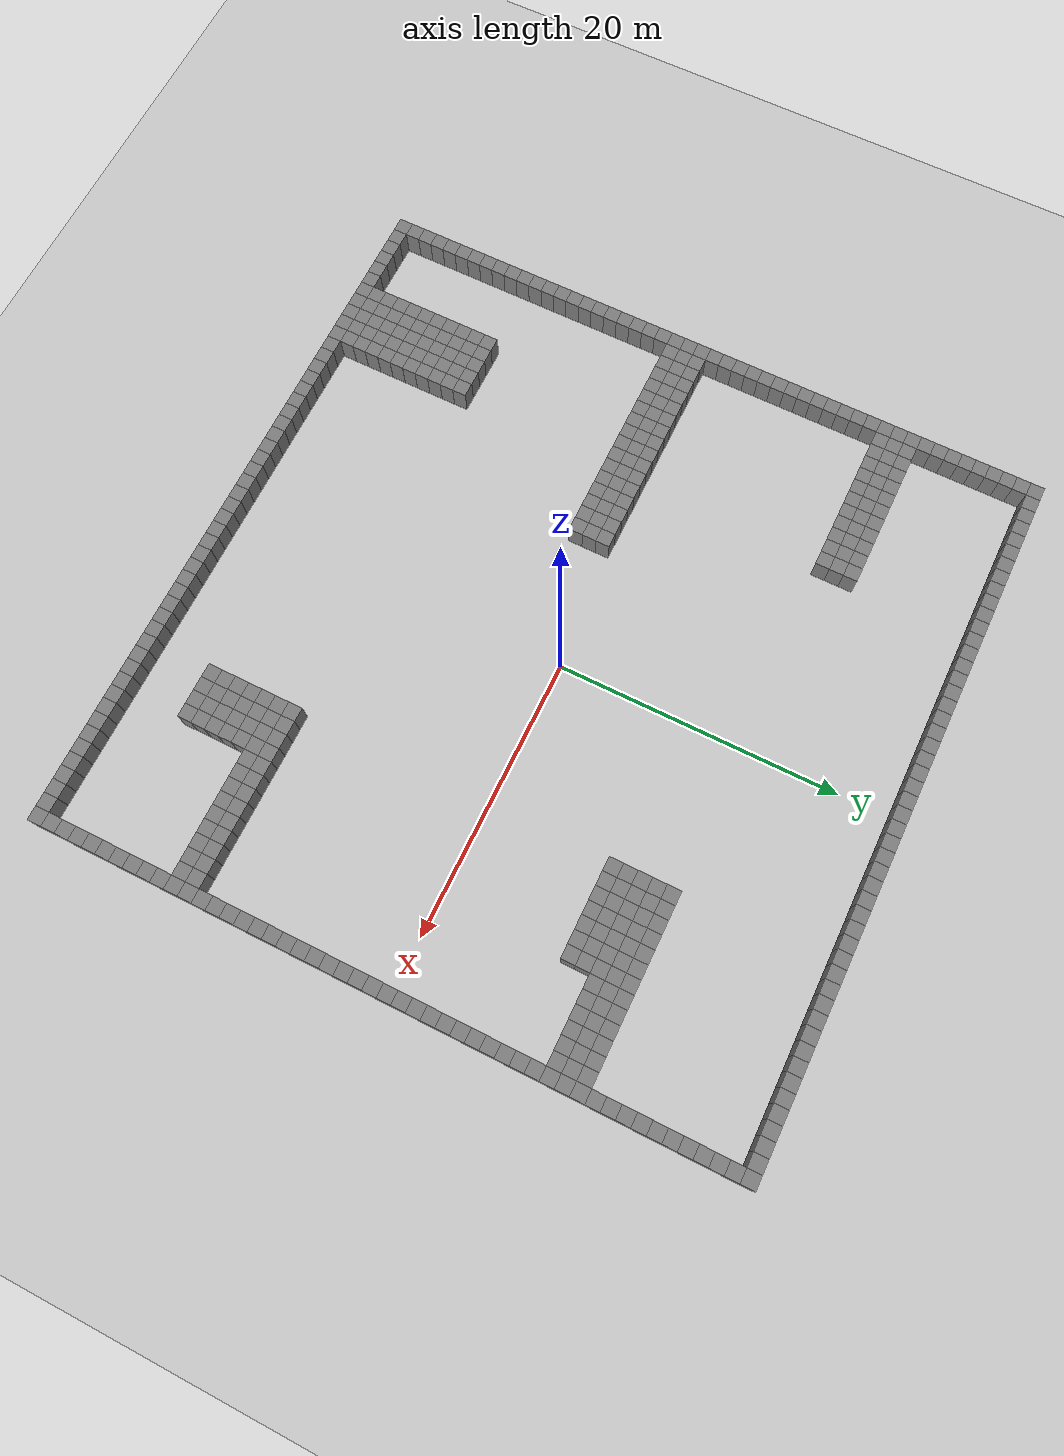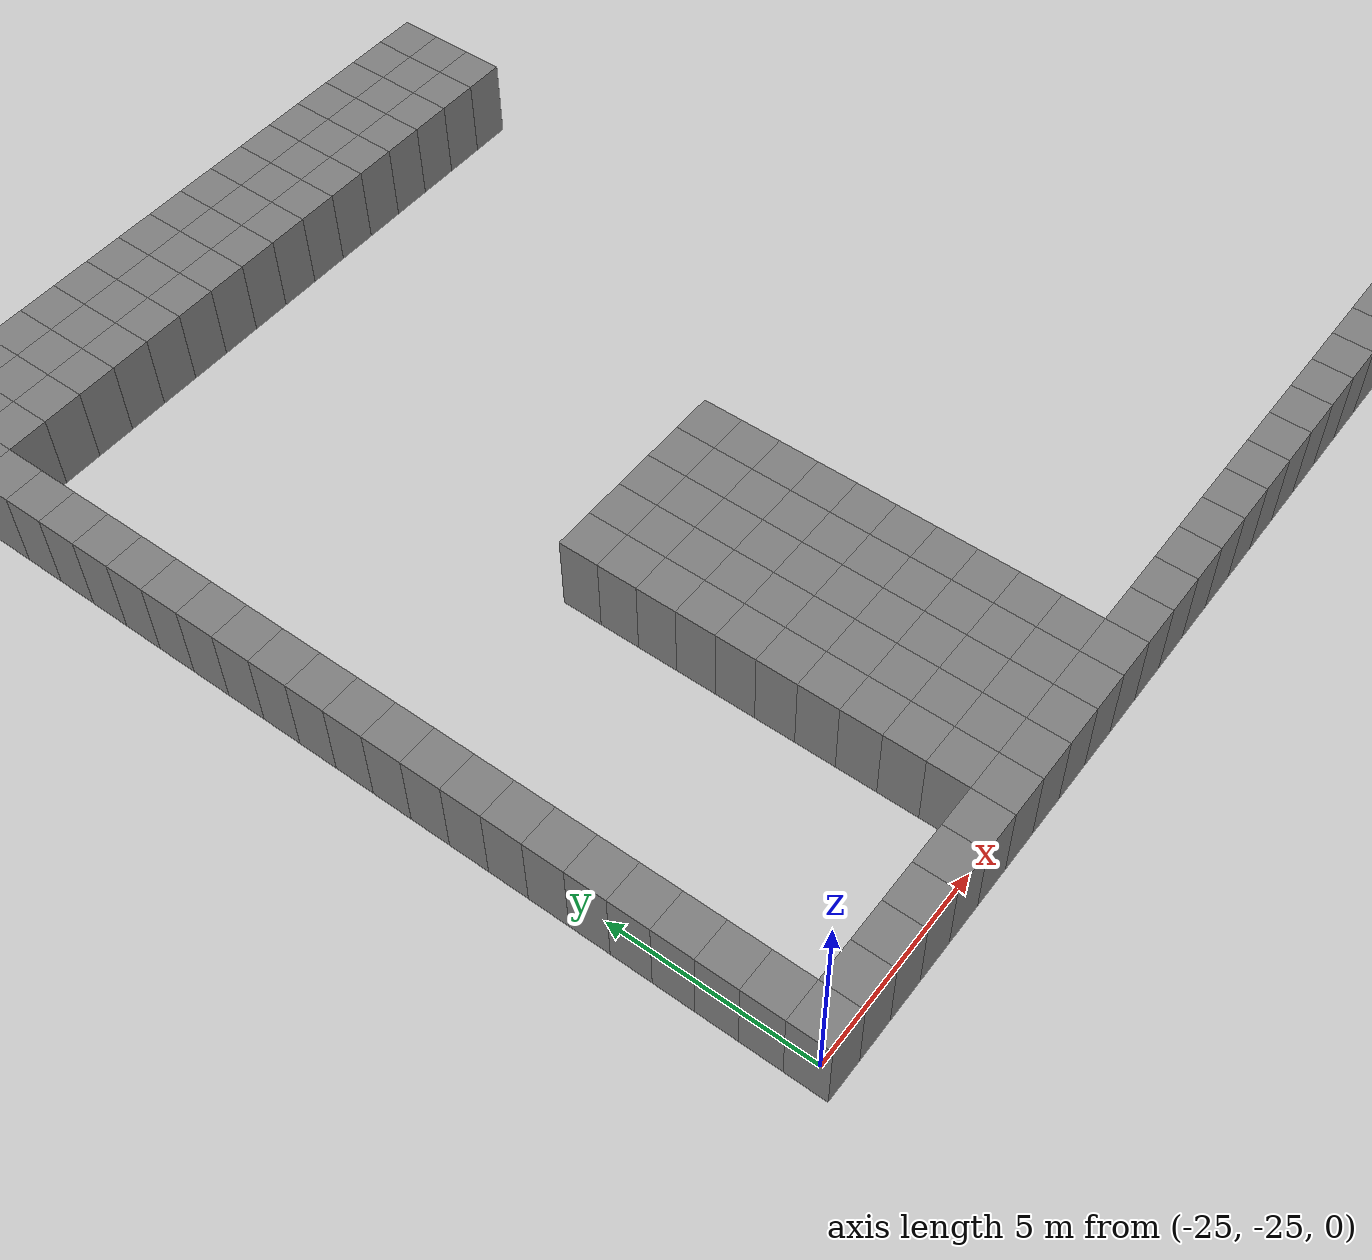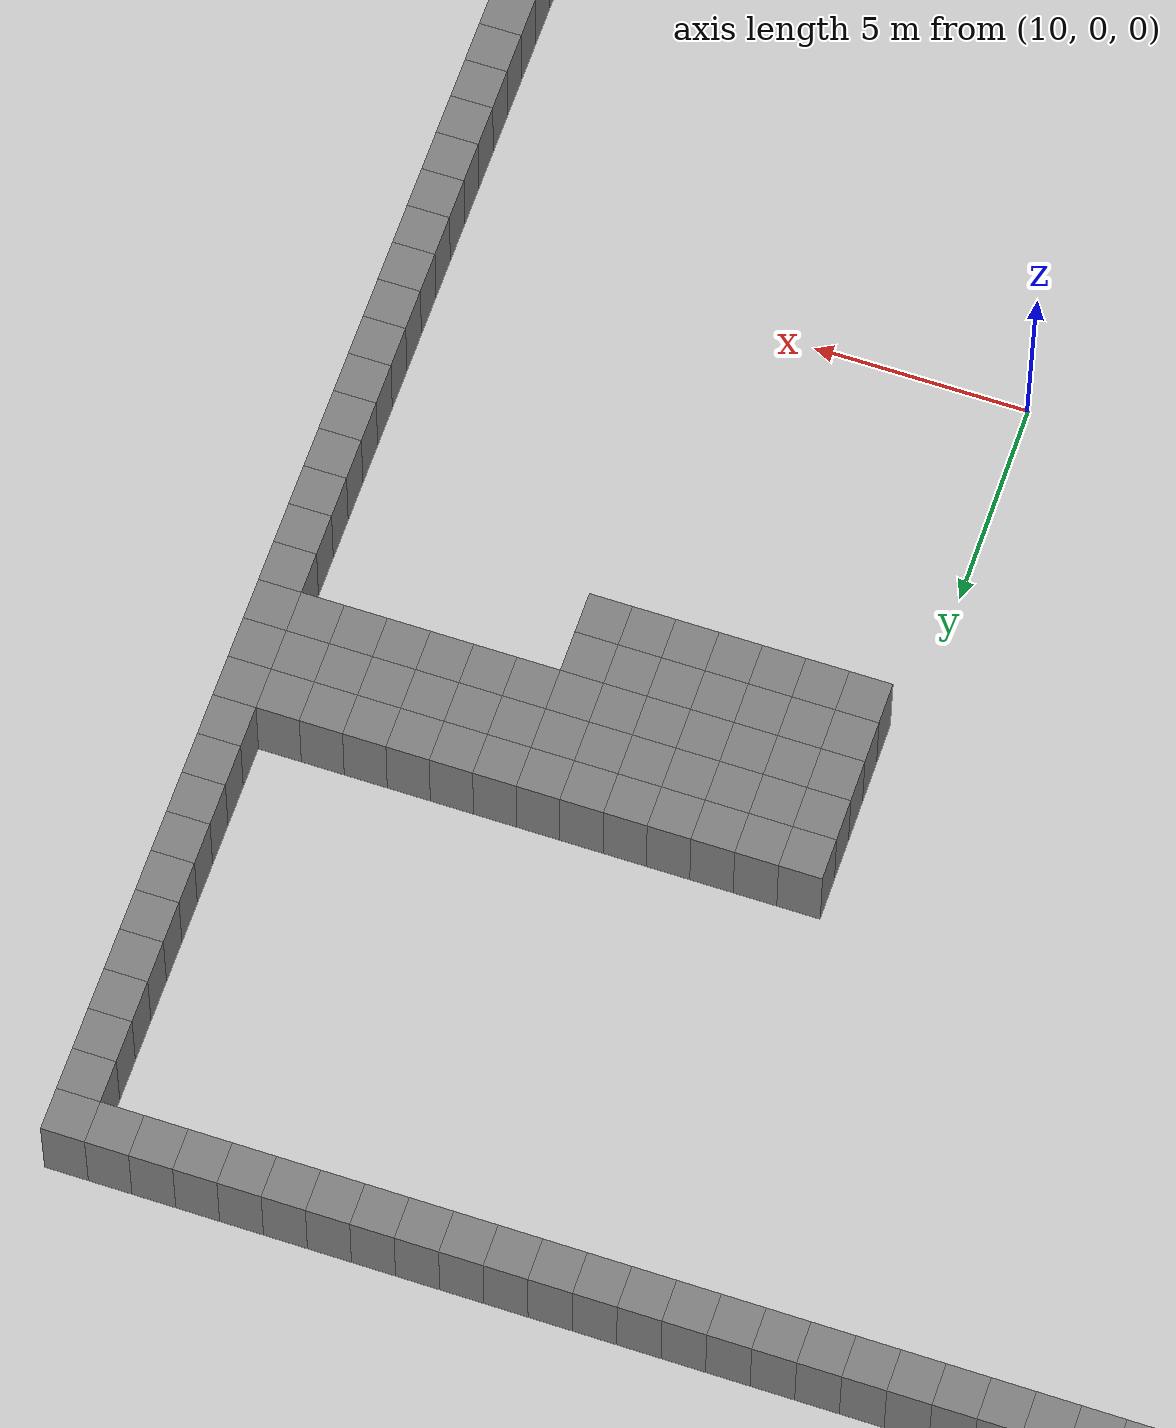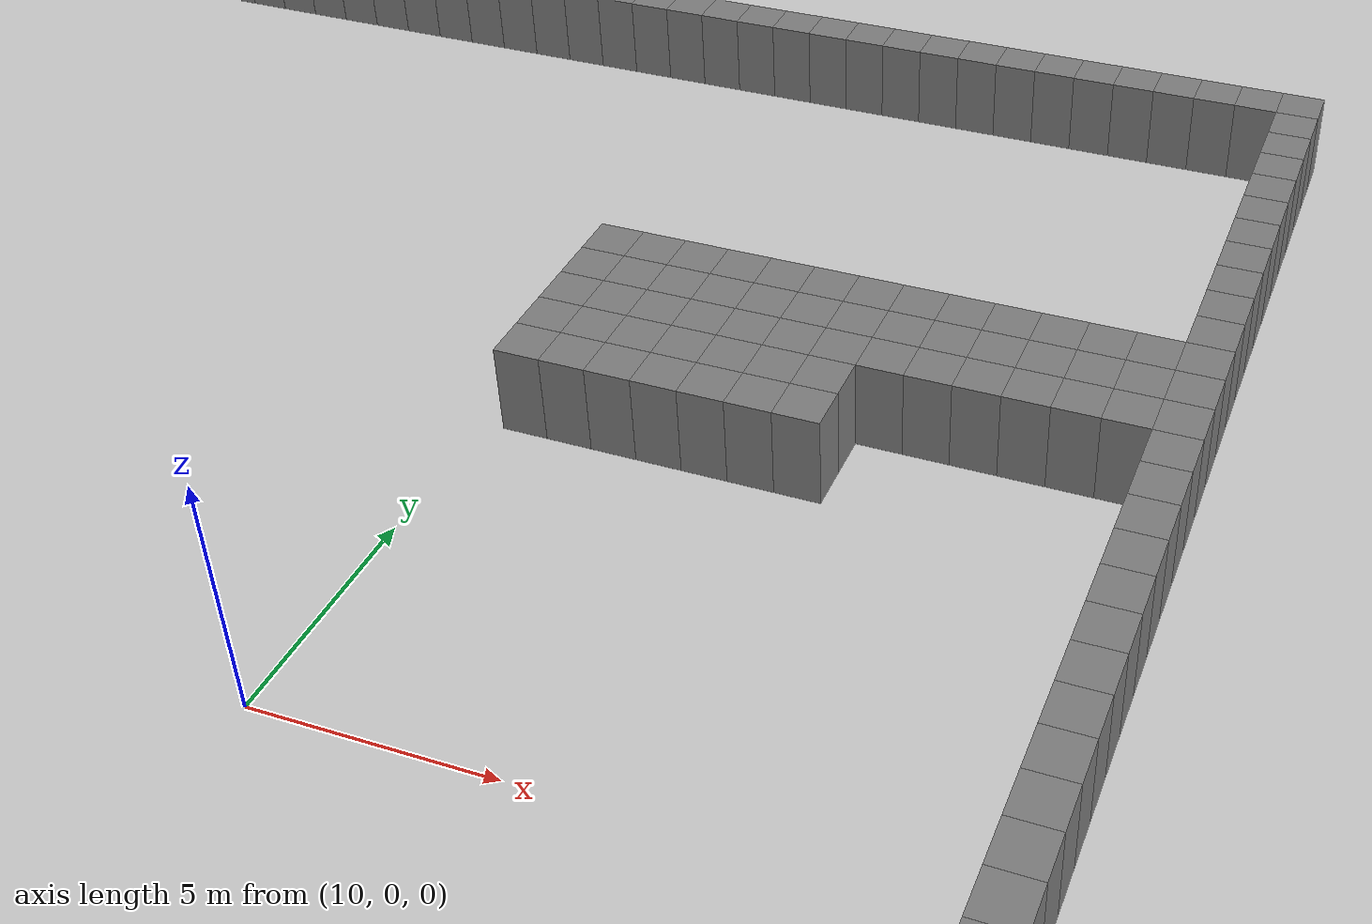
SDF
<?xml version="1.0" ?>
<sdf version="1.9">
  <world name="grid_world">
    <model name="ground_plane">
      <static>true</static>
      <link name="link">
        <collision name="collision">
          <geometry>
            <plane>
              <normal>0 0 1</normal>
              <size>100 100</size>
            </plane>
          </geometry>
        </collision>
        <visual name="visual">
          <geometry>
            <plane>
              <normal>0 0 1</normal>
              <size>100 100</size>
            </plane>
          </geometry>
          <material>
            <ambient>0.8 0.8 0.8 1</ambient>
            <diffuse>0.8 0.8 0.8 1</diffuse>
            <specular>0.8 0.8 0.8 1</specular>
          </material>
        </visual>
      </link>
    </model>
    <light type="directional" name="sun">
      <cast_shadows>true</cast_shadows>
      <pose>0 0 10 0 0 0</pose>
      <diffuse>0.8 0.8 0.8 1</diffuse>
      <specular>0.2 0.2 0.2 1</specular>
      <attenuation>
        <range>1000</range>
        <constant>0.9</constant>
        <linear>0.01</linear>
        <quadratic>0.001</quadratic>
      </attenuation>
      <direction>-0.5 0.1 -0.9</direction>
    </light>

    <model name="wall_0_0">
      <static>true</static>
      <pose>-25 -25 1 0 0 0</pose>
      <link name="link">
        <collision name="collision">
          <geometry>
            <box>
              <size>1 1 2</size>
            </box>
          </geometry>
        </collision>
        <visual name="visual">
          <geometry>
            <box>
              <size>1 1 2</size>
            </box>
          </geometry>
          <material>
            <ambient>0.5 0.5 0.5 1</ambient>
            <diffuse>0.5 0.5 0.5 1</diffuse>
            <specular>0.5 0.5 0.5 1</specular>
          </material>
        </visual>
      </link>
    </model>

    <model name="wall_0_1">
      <static>true</static>
      <pose>-24 -25 1 0 0 0</pose>
      <link name="link">
        <collision name="collision">
          <geometry>
            <box>
              <size>1 1 2</size>
            </box>
          </geometry>
        </collision>
        <visual name="visual">
          <geometry>
            <box>
              <size>1 1 2</size>
            </box>
          </geometry>
          <material>
            <ambient>0.5 0.5 0.5 1</ambient>
            <diffuse>0.5 0.5 0.5 1</diffuse>
            <specular>0.5 0.5 0.5 1</specular>
          </material>
        </visual>
      </link>
    </model>

    <model name="wall_0_2">
      <static>true</static>
      <pose>-23 -25 1 0 0 0</pose>
      <link name="link">
        <collision name="collision">
          <geometry>
            <box>
              <size>1 1 2</size>
            </box>
          </geometry>
        </collision>
        <visual name="visual">
          <geometry>
            <box>
              <size>1 1 2</size>
            </box>
          </geometry>
          <material>
            <ambient>0.5 0.5 0.5 1</ambient>
            <diffuse>0.5 0.5 0.5 1</diffuse>
            <specular>0.5 0.5 0.5 1</specular>
          </material>
        </visual>
      </link>
    </model>

    <model name="wall_0_3">
      <static>true</static>
      <pose>-22 -25 1 0 0 0</pose>
      <link name="link">
        <collision name="collision">
          <geometry>
            <box>
              <size>1 1 2</size>
            </box>
          </geometry>
        </collision>
        <visual name="visual">
          <geometry>
            <box>
              <size>1 1 2</size>
            </box>
          </geometry>
          <material>
            <ambient>0.5 0.5 0.5 1</ambient>
            <diffuse>0.5 0.5 0.5 1</diffuse>
            <specular>0.5 0.5 0.5 1</specular>
          </material>
        </visual>
      </link>
    </model>

    <model name="wall_0_4">
      <static>true</static>
      <pose>-21 -25 1 0 0 0</pose>
      <link name="link">
        <collision name="collision">
          <geometry>
            <box>
              <size>1 1 2</size>
            </box>
          </geometry>
        </collision>
        <visual name="visual">
          <geometry>
            <box>
              <size>1 1 2</size>
            </box>
          </geometry>
          <material>
            <ambient>0.5 0.5 0.5 1</ambient>
            <diffuse>0.5 0.5 0.5 1</diffuse>
            <specular>0.5 0.5 0.5 1</specular>
          </material>
        </visual>
      </link>
    </model>

    <model name="wall_0_5">
      <static>true</static>
      <pose>-20 -25 1 0 0 0</pose>
      <link name="link">
        <collision name="collision">
          <geometry>
            <box>
              <size>1 1 2</size>
            </box>
          </geometry>
        </collision>
        <visual name="visual">
          <geometry>
            <box>
              <size>1 1 2</size>
            </box>
          </geometry>
          <material>
            <ambient>0.5 0.5 0.5 1</ambient>
            <diffuse>0.5 0.5 0.5 1</diffuse>
            <specular>0.5 0.5 0.5 1</specular>
          </material>
        </visual>
      </link>
    </model>

    <model name="wall_0_6">
      <static>true</static>
      <pose>-19 -25 1 0 0 0</pose>
      <link name="link">
        <collision name="collision">
          <geometry>
            <box>
              <size>1 1 2</size>
            </box>
          </geometry>
        </collision>
        <visual name="visual">
          <geometry>
            <box>
              <size>1 1 2</size>
            </box>
          </geometry>
          <material>
            <ambient>0.5 0.5 0.5 1</ambient>
            <diffuse>0.5 0.5 0.5 1</diffuse>
            <specular>0.5 0.5 0.5 1</specular>
          </material>
        </visual>
      </link>
    </model>

    <model name="wall_0_7">
      <static>true</static>
      <pose>-18 -25 1 0 0 0</pose>
      <link name="link">
        <collision name="collision">
          <geometry>
            <box>
              <size>1 1 2</size>
            </box>
          </geometry>
        </collision>
        <visual name="visual">
          <geometry>
            <box>
              <size>1 1 2</size>
            </box>
          </geometry>
          <material>
            <ambient>0.5 0.5 0.5 1</ambient>
            <diffuse>0.5 0.5 0.5 1</diffuse>
            <specular>0.5 0.5 0.5 1</specular>
          </material>
        </visual>
      </link>
    </model>

    <model name="wall_0_8">
      <static>true</static>
      <pose>-17 -25 1 0 0 0</pose>
      <link name="link">
        <collision name="collision">
          <geometry>
            <box>
              <size>1 1 2</size>
            </box>
          </geometry>
        </collision>
        <visual name="visual">
          <geometry>
            <box>
              <size>1 1 2</size>
            </box>
          </geometry>
          <material>
            <ambient>0.5 0.5 0.5 1</ambient>
            <diffuse>0.5 0.5 0.5 1</diffuse>
            <specular>0.5 0.5 0.5 1</specular>
          </material>
        </visual>
      </link>
    </model>

    <model name="wall_0_9">
      <static>true</static>
      <pose>-16 -25 1 0 0 0</pose>
      <link name="link">
        <collision name="collision">
          <geometry>
            <box>
              <size>1 1 2</size>
            </box>
          </geometry>
        </collision>
        <visual name="visual">
          <geometry>
            <box>
              <size>1 1 2</size>
            </box>
          </geometry>
          <material>
            <ambient>0.5 0.5 0.5 1</ambient>
            <diffuse>0.5 0.5 0.5 1</diffuse>
            <specular>0.5 0.5 0.5 1</specular>
          </material>
        </visual>
      </link>
    </model>

    <model name="wall_0_10">
      <static>true</static>
      <pose>-15 -25 1 0 0 0</pose>
      <link name="link">
        <collision name="collision">
          <geometry>
            <box>
              <size>1 1 2</size>
            </box>
          </geometry>
        </collision>
        <visual name="visual">
          <geometry>
            <box>
              <size>1 1 2</size>
            </box>
          </geometry>
          <material>
            <ambient>0.5 0.5 0.5 1</ambient>
            <diffuse>0.5 0.5 0.5 1</diffuse>
            <specular>0.5 0.5 0.5 1</specular>
          </material>
        </visual>
      </link>
    </model>

    <model name="wall_0_11">
      <static>true</static>
      <pose>-14 -25 1 0 0 0</pose>
      <link name="link">
        <collision name="collision">
          <geometry>
            <box>
              <size>1 1 2</size>
            </box>
          </geometry>
        </collision>
        <visual name="visual">
          <geometry>
            <box>
              <size>1 1 2</size>
            </box>
          </geometry>
          <material>
            <ambient>0.5 0.5 0.5 1</ambient>
            <diffuse>0.5 0.5 0.5 1</diffuse>
            <specular>0.5 0.5 0.5 1</specular>
          </material>
        </visual>
      </link>
    </model>

    <model name="wall_0_12">
      <static>true</static>
      <pose>-13 -25 1 0 0 0</pose>
      <link name="link">
        <collision name="collision">
          <geometry>
            <box>
              <size>1 1 2</size>
            </box>
          </geometry>
        </collision>
        <visual name="visual">
          <geometry>
            <box>
              <size>1 1 2</size>
            </box>
          </geometry>
          <material>
            <ambient>0.5 0.5 0.5 1</ambient>
            <diffuse>0.5 0.5 0.5 1</diffuse>
            <specular>0.5 0.5 0.5 1</specular>
          </material>
        </visual>
      </link>
    </model>

    <model name="wall_0_13">
      <static>true</static>
      <pose>-12 -25 1 0 0 0</pose>
      <link name="link">
        <collision name="collision">
          <geometry>
            <box>
              <size>1 1 2</size>
            </box>
          </geometry>
        </collision>
        <visual name="visual">
          <geometry>
            <box>
              <size>1 1 2</size>
            </box>
          </geometry>
          <material>
            <ambient>0.5 0.5 0.5 1</ambient>
            <diffuse>0.5 0.5 0.5 1</diffuse>
            <specular>0.5 0.5 0.5 1</specular>
          </material>
        </visual>
      </link>
    </model>

    <model name="wall_0_14">
      <static>true</static>
      <pose>-11 -25 1 0 0 0</pose>
      <link name="link">
        <collision name="collision">
          <geometry>
            <box>
              <size>1 1 2</size>
            </box>
          </geometry>
        </collision>
        <visual name="visual">
          <geometry>
            <box>
              <size>1 1 2</size>
            </box>
          </geometry>
          <material>
            <ambient>0.5 0.5 0.5 1</ambient>
            <diffuse>0.5 0.5 0.5 1</diffuse>
            <specular>0.5 0.5 0.5 1</specular>
          </material>
        </visual>
      </link>
    </model>

    <model name="wall_0_15">
      <static>true</static>
      <pose>-10 -25 1 0 0 0</pose>
      <link name="link">
        <collision name="collision">
          <geometry>
            <box>
              <size>1 1 2</size>
            </box>
          </geometry>
        </collision>
        <visual name="visual">
          <geometry>
            <box>
              <size>1 1 2</size>
            </box>
          </geometry>
          <material>
            <ambient>0.5 0.5 0.5 1</ambient>
            <diffuse>0.5 0.5 0.5 1</diffuse>
            <specular>0.5 0.5 0.5 1</specular>
          </material>
        </visual>
      </link>
    </model>

    <model name="wall_0_16">
      <static>true</static>
      <pose>-9 -25 1 0 0 0</pose>
      <link name="link">
        <collision name="collision">
          <geometry>
            <box>
              <size>1 1 2</size>
            </box>
          </geometry>
        </collision>
        <visual name="visual">
          <geometry>
            <box>
              <size>1 1 2</size>
            </box>
          </geometry>
          <material>
            <ambient>0.5 0.5 0.5 1</ambient>
            <diffuse>0.5 0.5 0.5 1</diffuse>
            <specular>0.5 0.5 0.5 1</specular>
          </material>
        </visual>
      </link>
    </model>

    <model name="wall_0_17">
      <static>true</static>
      <pose>-8 -25 1 0 0 0</pose>
      <link name="link">
        <collision name="collision">
          <geometry>
            <box>
              <size>1 1 2</size>
            </box>
          </geometry>
        </collision>
        <visual name="visual">
          <geometry>
            <box>
              <size>1 1 2</size>
            </box>
          </geometry>
          <material>
            <ambient>0.5 0.5 0.5 1</ambient>
            <diffuse>0.5 0.5 0.5 1</diffuse>
            <specular>0.5 0.5 0.5 1</specular>
          </material>
        </visual>
      </link>
    </model>

    <model name="wall_0_18">
      <static>true</static>
      <pose>-7 -25 1 0 0 0</pose>
      <link name="link">
        <collision name="collision">
          <geometry>
            <box>
              <size>1 1 2</size>
            </box>
          </geometry>
        </collision>
        <visual name="visual">
          <geometry>
            <box>
              <size>1 1 2</size>
            </box>
          </geometry>
          <material>
            <ambient>0.5 0.5 0.5 1</ambient>
            <diffuse>0.5 0.5 0.5 1</diffuse>
            <specular>0.5 0.5 0.5 1</specular>
          </material>
        </visual>
      </link>
    </model>

    <model name="wall_0_19">
      <static>true</static>
      <pose>-6 -25 1 0 0 0</pose>
      <link name="link">
        <collision name="collision">
          <geometry>
            <box>
              <size>1 1 2</size>
            </box>
          </geometry>
        </collision>
        <visual name="visual">
          <geometry>
            <box>
              <size>1 1 2</size>
            </box>
          </geometry>
          <material>
            <ambient>0.5 0.5 0.5 1</ambient>
            <diffuse>0.5 0.5 0.5 1</diffuse>
            <specular>0.5 0.5 0.5 1</specular>
          </material>
        </visual>
      </link>
    </model>

    <model name="wall_0_20">
      <static>true</static>
      <pose>-5 -25 1 0 0 0</pose>
      <link name="link">
        <collision name="collision">
          <geometry>
            <box>
              <size>1 1 2</size>
            </box>
          </geometry>
        </collision>
        <visual name="visual">
          <geometry>
            <box>
              <size>1 1 2</size>
            </box>
          </geometry>
          <material>
            <ambient>0.5 0.5 0.5 1</ambient>
            <diffuse>0.5 0.5 0.5 1</diffuse>
            <specular>0.5 0.5 0.5 1</specular>
          </material>
        </visual>
      </link>
    </model>

    <model name="wall_0_21">
      <static>true</static>
      <pose>-4 -25 1 0 0 0</pose>
      <link name="link">
        <collision name="collision">
          <geometry>
            <box>
              <size>1 1 2</size>
            </box>
          </geometry>
        </collision>
        <visual name="visual">
          <geometry>
            <box>
              <size>1 1 2</size>
            </box>
          </geometry>
          <material>
            <ambient>0.5 0.5 0.5 1</ambient>
            <diffuse>0.5 0.5 0.5 1</diffuse>
            <specular>0.5 0.5 0.5 1</specular>
          </material>
        </visual>
      </link>
    </model>

    <model name="wall_0_22">
      <static>true</static>
      <pose>-3 -25 1 0 0 0</pose>
      <link name="link">
        <collision name="collision">
          <geometry>
            <box>
              <size>1 1 2</size>
            </box>
          </geometry>
        </collision>
        <visual name="visual">
          <geometry>
            <box>
              <size>1 1 2</size>
            </box>
          </geometry>
          <material>
            <ambient>0.5 0.5 0.5 1</ambient>
            <diffuse>0.5 0.5 0.5 1</diffuse>
            <specular>0.5 0.5 0.5 1</specular>
          </material>
        </visual>
      </link>
    </model>

    <model name="wall_0_23">
      <static>true</static>
      <pose>-2 -25 1 0 0 0</pose>
      <link name="link">
        <collision name="collision">
          <geometry>
            <box>
              <size>1 1 2</size>
            </box>
          </geometry>
        </collision>
        <visual name="visual">
          <geometry>
            <box>
              <size>1 1 2</size>
            </box>
          </geometry>
          <material>
            <ambient>0.5 0.5 0.5 1</ambient>
            <diffuse>0.5 0.5 0.5 1</diffuse>
            <specular>0.5 0.5 0.5 1</specular>
          </material>
        </visual>
      </link>
    </model>

    <model name="wall_0_24">
      <static>true</static>
      <pose>-1 -25 1 0 0 0</pose>
      <link name="link">
        <collision name="collision">
          <geometry>
            <box>
              <size>1 1 2</size>
            </box>
          </geometry>
        </collision>
        <visual name="visual">
          <geometry>
            <box>
              <size>1 1 2</size>
            </box>
          </geometry>
          <material>
            <ambient>0.5 0.5 0.5 1</ambient>
            <diffuse>0.5 0.5 0.5 1</diffuse>
            <specular>0.5 0.5 0.5 1</specular>
          </material>
        </visual>
      </link>
    </model>

    <model name="wall_0_25">
      <static>true</static>
      <pose>0 -25 1 0 0 0</pose>
      <link name="link">
        <collision name="collision">
          <geometry>
            <box>
              <size>1 1 2</size>
            </box>
          </geometry>
        </collision>
        <visual name="visual">
          <geometry>
            <box>
              <size>1 1 2</size>
            </box>
          </geometry>
          <material>
            <ambient>0.5 0.5 0.5 1</ambient>
            <diffuse>0.5 0.5 0.5 1</diffuse>
            <specular>0.5 0.5 0.5 1</specular>
          </material>
        </visual>
      </link>
    </model>

    <model name="wall_0_26">
      <static>true</static>
      <pose>1 -25 1 0 0 0</pose>
      <link name="link">
        <collision name="collision">
          <geometry>
            <box>
              <size>1 1 2</size>
            </box>
          </geometry>
        </collision>
        <visual name="visual">
          <geometry>
            <box>
              <size>1 1 2</size>
            </box>
          </geometry>
          <material>
            <ambient>0.5 0.5 0.5 1</ambient>
            <diffuse>0.5 0.5 0.5 1</diffuse>
            <specular>0.5 0.5 0.5 1</specular>
          </material>
        </visual>
      </link>
    </model>

    <model name="wall_0_27">
      <static>true</static>
      <pose>2 -25 1 0 0 0</pose>
      <link name="link">
        <collision name="collision">
          <geometry>
            <box>
              <size>1 1 2</size>
            </box>
          </geometry>
        </collision>
        <visual name="visual">
          <geometry>
            <box>
              <size>1 1 2</size>
            </box>
          </geometry>
          <material>
            <ambient>0.5 0.5 0.5 1</ambient>
            <diffuse>0.5 0.5 0.5 1</diffuse>
            <specular>0.5 0.5 0.5 1</specular>
          </material>
        </visual>
      </link>
    </model>

    <model name="wall_0_28">
      <static>true</static>
      <pose>3 -25 1 0 0 0</pose>
      <link name="link">
        <collision name="collision">
          <geometry>
            <box>
              <size>1 1 2</size>
            </box>
          </geometry>
        </collision>
        <visual name="visual">
          <geometry>
            <box>
              <size>1 1 2</size>
            </box>
          </geometry>
          <material>
            <ambient>0.5 0.5 0.5 1</ambient>
            <diffuse>0.5 0.5 0.5 1</diffuse>
            <specular>0.5 0.5 0.5 1</specular>
          </material>
        </visual>
      </link>
    </model>

    <model name="wall_0_29">
      <static>true</static>
      <pose>4 -25 1 0 0 0</pose>
      <link name="link">
        <collision name="collision">
          <geometry>
            <box>
              <size>1 1 2</size>
            </box>
          </geometry>
        </collision>
        <visual name="visual">
          <geometry>
            <box>
              <size>1 1 2</size>
            </box>
          </geometry>
          <material>
            <ambient>0.5 0.5 0.5 1</ambient>
            <diffuse>0.5 0.5 0.5 1</diffuse>
            <specular>0.5 0.5 0.5 1</specular>
          </material>
        </visual>
      </link>
    </model>

    <model name="wall_0_30">
      <static>true</static>
      <pose>5 -25 1 0 0 0</pose>
      <link name="link">
        <collision name="collision">
          <geometry>
            <box>
              <size>1 1 2</size>
            </box>
          </geometry>
        </collision>
        <visual name="visual">
          <geometry>
            <box>
              <size>1 1 2</size>
            </box>
          </geometry>
          <material>
            <ambient>0.5 0.5 0.5 1</ambient>
            <diffuse>0.5 0.5 0.5 1</diffuse>
            <specular>0.5 0.5 0.5 1</specular>
          </material>
        </visual>
      </link>
    </model>

    <model name="wall_0_31">
      <static>true</static>
      <pose>6 -25 1 0 0 0</pose>
      <link name="link">
        <collision name="collision">
          <geometry>
            <box>
              <size>1 1 2</size>
            </box>
          </geometry>
        </collision>
        <visual name="visual">
          <geometry>
            <box>
              <size>1 1 2</size>
            </box>
          </geometry>
          <material>
            <ambient>0.5 0.5 0.5 1</ambient>
            <diffuse>0.5 0.5 0.5 1</diffuse>
            <specular>0.5 0.5 0.5 1</specular>
          </material>
        </visual>
      </link>
    </model>

    <model name="wall_0_32">
      <static>true</static>
      <pose>7 -25 1 0 0 0</pose>
      <link name="link">
        <collision name="collision">
          <geometry>
            <box>
              <size>1 1 2</size>
            </box>
          </geometry>
        </collision>
        <visual name="visual">
          <geometry>
            <box>
              <size>1 1 2</size>
            </box>
          </geometry>
          <material>
            <ambient>0.5 0.5 0.5 1</ambient>
            <diffuse>0.5 0.5 0.5 1</diffuse>
            <specular>0.5 0.5 0.5 1</specular>
          </material>
        </visual>
      </link>
    </model>

    <model name="wall_0_33">
      <static>true</static>
      <pose>8 -25 1 0 0 0</pose>
      <link name="link">
        <collision name="collision">
          <geometry>
            <box>
              <size>1 1 2</size>
            </box>
          </geometry>
        </collision>
        <visual name="visual">
          <geometry>
            <box>
              <size>1 1 2</size>
            </box>
          </geometry>
          <material>
            <ambient>0.5 0.5 0.5 1</ambient>
            <diffuse>0.5 0.5 0.5 1</diffuse>
            <specular>0.5 0.5 0.5 1</specular>
          </material>
        </visual>
      </link>
    </model>

    <model name="wall_0_34">
      <static>true</static>
      <pose>9 -25 1 0 0 0</pose>
      <link name="link">
        <collision name="collision">
          <geometry>
            <box>
              <size>1 1 2</size>
            </box>
          </geometry>
        </collision>
        <visual name="visual">
          <geometry>
            <box>
              <size>1 1 2</size>
            </box>
          </geometry>
          <material>
            <ambient>0.5 0.5 0.5 1</ambient>
            <diffuse>0.5 0.5 0.5 1</diffuse>
            <specular>0.5 0.5 0.5 1</specular>
          </material>
        </visual>
      </link>
    </model>

    <model name="wall_0_35">
      <static>true</static>
      <pose>10 -25 1 0 0 0</pose>
      <link name="link">
        <collision name="collision">
          <geometry>
            <box>
              <size>1 1 2</size>
            </box>
          </geometry>
        </collision>
        <visual name="visual">
          <geometry>
            <box>
              <size>1 1 2</size>
            </box>
          </geometry>
          <material>
            <ambient>0.5 0.5 0.5 1</ambient>
            <diffuse>0.5 0.5 0.5 1</diffuse>
            <specular>0.5 0.5 0.5 1</specular>
          </material>
        </visual>
      </link>
    </model>

    <model name="wall_0_36">
      <static>true</static>
      <pose>11 -25 1 0 0 0</pose>
      <link name="link">
        <collision name="collision">
          <geometry>
            <box>
              <size>1 1 2</size>
            </box>
          </geometry>
        </collision>
        <visual name="visual">
          <geometry>
            <box>
              <size>1 1 2</size>
            </box>
          </geometry>
          <material>
            <ambient>0.5 0.5 0.5 1</ambient>
            <diffuse>0.5 0.5 0.5 1</diffuse>
            <specular>0.5 0.5 0.5 1</specular>
          </material>
        </visual>
      </link>
    </model>

    <model name="wall_0_37">
      <static>true</static>
      <pose>12 -25 1 0 0 0</pose>
      <link name="link">
        <collision name="collision">
          <geometry>
            <box>
              <size>1 1 2</size>
            </box>
          </geometry>
        </collision>
        <visual name="visual">
          <geometry>
            <box>
              <size>1 1 2</size>
            </box>
          </geometry>
          <material>
            <ambient>0.5 0.5 0.5 1</ambient>
            <diffuse>0.5 0.5 0.5 1</diffuse>
            <specular>0.5 0.5 0.5 1</specular>
          </material>
        </visual>
      </link>
    </model>

    <model name="wall_0_38">
      <static>true</static>
      <pose>13 -25 1 0 0 0</pose>
      <link name="link">
        <collision name="collision">
          <geometry>
            <box>
              <size>1 1 2</size>
            </box>
          </geometry>
        </collision>
        <visual name="visual">
          <geometry>
            <box>
              <size>1 1 2</size>
            </box>
          </geometry>
          <material>
            <ambient>0.5 0.5 0.5 1</ambient>
            <diffuse>0.5 0.5 0.5 1</diffuse>
            <specular>0.5 0.5 0.5 1</specular>
          </material>
        </visual>
      </link>
    </model>

    <model name="wall_0_39">
      <static>true</static>
      <pose>14 -25 1 0 0 0</pose>
      <link name="link">
        <collision name="collision">
          <geometry>
            <box>
              <size>1 1 2</size>
            </box>
          </geometry>
        </collision>
        <visual name="visual">
          <geometry>
            <box>
              <size>1 1 2</size>
            </box>
          </geometry>
          <material>
            <ambient>0.5 0.5 0.5 1</ambient>
            <diffuse>0.5 0.5 0.5 1</diffuse>
            <specular>0.5 0.5 0.5 1</specular>
          </material>
        </visual>
      </link>
    </model>

    <model name="wall_0_40">
      <static>true</static>
      <pose>15 -25 1 0 0 0</pose>
      <link name="link">
        <collision name="collision">
          <geometry>
            <box>
              <size>1 1 2</size>
            </box>
          </geometry>
        </collision>
        <visual name="visual">
          <geometry>
            <box>
              <size>1 1 2</size>
            </box>
          </geometry>
          <material>
            <ambient>0.5 0.5 0.5 1</ambient>
            <diffuse>0.5 0.5 0.5 1</diffuse>
            <specular>0.5 0.5 0.5 1</specular>
          </material>
        </visual>
      </link>
    </model>

    <model name="wall_0_41">
      <static>true</static>
      <pose>16 -25 1 0 0 0</pose>
      <link name="link">
        <collision name="collision">
          <geometry>
            <box>
              <size>1 1 2</size>
            </box>
          </geometry>
        </collision>
        <visual name="visual">
          <geometry>
            <box>
              <size>1 1 2</size>
            </box>
          </geometry>
          <material>
            <ambient>0.5 0.5 0.5 1</ambient>
            <diffuse>0.5 0.5 0.5 1</diffuse>
            <specular>0.5 0.5 0.5 1</specular>
          </material>
        </visual>
      </link>
    </model>

    <model name="wall_0_42">
      <static>true</static>
      <pose>17 -25 1 0 0 0</pose>
      <link name="link">
        <collision name="collision">
          <geometry>
            <box>
              <size>1 1 2</size>
            </box>
          </geometry>
        </collision>
        <visual name="visual">
          <geometry>
            <box>
              <size>1 1 2</size>
            </box>
          </geometry>
          <material>
            <ambient>0.5 0.5 0.5 1</ambient>
            <diffuse>0.5 0.5 0.5 1</diffuse>
            <specular>0.5 0.5 0.5 1</specular>
          </material>
        </visual>
      </link>
    </model>

    <model name="wall_0_43">
      <static>true</static>
      <pose>18 -25 1 0 0 0</pose>
      <link name="link">
        <collision name="collision">
          <geometry>
            <box>
              <size>1 1 2</size>
            </box>
          </geometry>
        </collision>
        <visual name="visual">
          <geometry>
            <box>
              <size>1 1 2</size>
            </box>
          </geometry>
          <material>
            <ambient>0.5 0.5 0.5 1</ambient>
            <diffuse>0.5 0.5 0.5 1</diffuse>
            <specular>0.5 0.5 0.5 1</specular>
          </material>
        </visual>
      </link>
    </model>

    <model name="wall_0_44">
      <static>true</static>
      <pose>19 -25 1 0 0 0</pose>
      <link name="link">
        <collision name="collision">
          <geometry>
            <box>
              <size>1 1 2</size>
            </box>
          </geometry>
        </collision>
        <visual name="visual">
          <geometry>
            <box>
              <size>1 1 2</size>
            </box>
          </geometry>
          <material>
            <ambient>0.5 0.5 0.5 1</ambient>
            <diffuse>0.5 0.5 0.5 1</diffuse>
            <specular>0.5 0.5 0.5 1</specular>
          </material>
        </visual>
      </link>
    </model>

    <model name="wall_0_45">
      <static>true</static>
      <pose>20 -25 1 0 0 0</pose>
      <link name="link">
        <collision name="collision">
          <geometry>
            <box>
              <size>1 1 2</size>
            </box>
          </geometry>
        </collision>
        <visual name="visual">
          <geometry>
            <box>
              <size>1 1 2</size>
            </box>
          </geometry>
          <material>
            <ambient>0.5 0.5 0.5 1</ambient>
            <diffuse>0.5 0.5 0.5 1</diffuse>
            <specular>0.5 0.5 0.5 1</specular>
          </material>
        </visual>
      </link>
    </model>

    <model name="wall_0_46">
      <static>true</static>
      <pose>21 -25 1 0 0 0</pose>
      <link name="link">
        <collision name="collision">
          <geometry>
            <box>
              <size>1 1 2</size>
            </box>
          </geometry>
        </collision>
        <visual name="visual">
          <geometry>
            <box>
              <size>1 1 2</size>
            </box>
          </geometry>
          <material>
            <ambient>0.5 0.5 0.5 1</ambient>
            <diffuse>0.5 0.5 0.5 1</diffuse>
            <specular>0.5 0.5 0.5 1</specular>
          </material>
        </visual>
      </link>
    </model>

    <model name="wall_0_47">
      <static>true</static>
      <pose>22 -25 1 0 0 0</pose>
      <link name="link">
        <collision name="collision">
          <geometry>
            <box>
              <size>1 1 2</size>
            </box>
          </geometry>
        </collision>
        <visual name="visual">
          <geometry>
            <box>
              <size>1 1 2</size>
            </box>
          </geometry>
          <material>
            <ambient>0.5 0.5 0.5 1</ambient>
            <diffuse>0.5 0.5 0.5 1</diffuse>
            <specular>0.5 0.5 0.5 1</specular>
          </material>
        </visual>
      </link>
    </model>

    <model name="wall_0_48">
      <static>true</static>
      <pose>23 -25 1 0 0 0</pose>
      <link name="link">
        <collision name="collision">
          <geometry>
            <box>
              <size>1 1 2</size>
            </box>
          </geometry>
        </collision>
        <visual name="visual">
          <geometry>
            <box>
              <size>1 1 2</size>
            </box>
          </geometry>
          <material>
            <ambient>0.5 0.5 0.5 1</ambient>
            <diffuse>0.5 0.5 0.5 1</diffuse>
            <specular>0.5 0.5 0.5 1</specular>
          </material>
        </visual>
      </link>
    </model>

    <model name="wall_0_49">
      <static>true</static>
      <pose>24 -25 1 0 0 0</pose>
      <link name="link">
        <collision name="collision">
          <geometry>
            <box>
              <size>1 1 2</size>
            </box>
          </geometry>
        </collision>
        <visual name="visual">
          <geometry>
            <box>
              <size>1 1 2</size>
            </box>
          </geometry>
          <material>
            <ambient>0.5 0.5 0.5 1</ambient>
            <diffuse>0.5 0.5 0.5 1</diffuse>
            <specular>0.5 0.5 0.5 1</specular>
          </material>
        </visual>
      </link>
    </model>

    <model name="wall_1_0">
      <static>true</static>
      <pose>-25 -24 1 0 0 0</pose>
      <link name="link">
        <collision name="collision">
          <geometry>
            <box>
              <size>1 1 2</size>
            </box>
          </geometry>
        </collision>
        <visual name="visual">
          <geometry>
            <box>
              <size>1 1 2</size>
            </box>
          </geometry>
          <material>
            <ambient>0.5 0.5 0.5 1</ambient>
            <diffuse>0.5 0.5 0.5 1</diffuse>
            <specular>0.5 0.5 0.5 1</specular>
          </material>
        </visual>
      </link>
    </model>

    <model name="wall_1_6">
      <static>true</static>
      <pose>-19 -24 1 0 0 0</pose>
      <link name="link">
        <collision name="collision">
          <geometry>
            <box>
              <size>1 1 2</size>
            </box>
          </geometry>
        </collision>
        <visual name="visual">
          <geometry>
            <box>
              <size>1 1 2</size>
            </box>
          </geometry>
          <material>
            <ambient>0.5 0.5 0.5 1</ambient>
            <diffuse>0.5 0.5 0.5 1</diffuse>
            <specular>0.5 0.5 0.5 1</specular>
          </material>
        </visual>
      </link>
    </model>

    <model name="wall_1_7">
      <static>true</static>
      <pose>-18 -24 1 0 0 0</pose>
      <link name="link">
        <collision name="collision">
          <geometry>
            <box>
              <size>1 1 2</size>
            </box>
          </geometry>
        </collision>
        <visual name="visual">
          <geometry>
            <box>
              <size>1 1 2</size>
            </box>
          </geometry>
          <material>
            <ambient>0.5 0.5 0.5 1</ambient>
            <diffuse>0.5 0.5 0.5 1</diffuse>
            <specular>0.5 0.5 0.5 1</specular>
          </material>
        </visual>
      </link>
    </model>

    <model name="wall_1_8">
      <static>true</static>
      <pose>-17 -24 1 0 0 0</pose>
      <link name="link">
        <collision name="collision">
          <geometry>
            <box>
              <size>1 1 2</size>
            </box>
          </geometry>
        </collision>
        <visual name="visual">
          <geometry>
            <box>
              <size>1 1 2</size>
            </box>
          </geometry>
          <material>
            <ambient>0.5 0.5 0.5 1</ambient>
            <diffuse>0.5 0.5 0.5 1</diffuse>
            <specular>0.5 0.5 0.5 1</specular>
          </material>
        </visual>
      </link>
    </model>

    <model name="wall_1_9">
      <static>true</static>
      <pose>-16 -24 1 0 0 0</pose>
      <link name="link">
        <collision name="collision">
          <geometry>
            <box>
              <size>1 1 2</size>
            </box>
          </geometry>
        </collision>
        <visual name="visual">
          <geometry>
            <box>
              <size>1 1 2</size>
            </box>
          </geometry>
          <material>
            <ambient>0.5 0.5 0.5 1</ambient>
            <diffuse>0.5 0.5 0.5 1</diffuse>
            <specular>0.5 0.5 0.5 1</specular>
          </material>
        </visual>
      </link>
    </model>

    <model name="wall_1_10">
      <static>true</static>
      <pose>-15 -24 1 0 0 0</pose>
      <link name="link">
        <collision name="collision">
          <geometry>
            <box>
              <size>1 1 2</size>
            </box>
          </geometry>
        </collision>
        <visual name="visual">
          <geometry>
            <box>
              <size>1 1 2</size>
            </box>
          </geometry>
          <material>
            <ambient>0.5 0.5 0.5 1</ambient>
            <diffuse>0.5 0.5 0.5 1</diffuse>
            <specular>0.5 0.5 0.5 1</specular>
          </material>
        </visual>
      </link>
    </model>

    <model name="wall_1_49">
      <static>true</static>
      <pose>24 -24 1 0 0 0</pose>
      <link name="link">
        <collision name="collision">
          <geometry>
            <box>
              <size>1 1 2</size>
            </box>
          </geometry>
        </collision>
        <visual name="visual">
          <geometry>
            <box>
              <size>1 1 2</size>
            </box>
          </geometry>
          <material>
            <ambient>0.5 0.5 0.5 1</ambient>
            <diffuse>0.5 0.5 0.5 1</diffuse>
            <specular>0.5 0.5 0.5 1</specular>
          </material>
        </visual>
      </link>
    </model>

    <model name="wall_2_0">
      <static>true</static>
      <pose>-25 -23 1 0 0 0</pose>
      <link name="link">
        <collision name="collision">
          <geometry>
            <box>
              <size>1 1 2</size>
            </box>
          </geometry>
        </collision>
        <visual name="visual">
          <geometry>
            <box>
              <size>1 1 2</size>
            </box>
          </geometry>
          <material>
            <ambient>0.5 0.5 0.5 1</ambient>
            <diffuse>0.5 0.5 0.5 1</diffuse>
            <specular>0.5 0.5 0.5 1</specular>
          </material>
        </visual>
      </link>
    </model>

    <model name="wall_2_6">
      <static>true</static>
      <pose>-19 -23 1 0 0 0</pose>
      <link name="link">
        <collision name="collision">
          <geometry>
            <box>
              <size>1 1 2</size>
            </box>
          </geometry>
        </collision>
        <visual name="visual">
          <geometry>
            <box>
              <size>1 1 2</size>
            </box>
          </geometry>
          <material>
            <ambient>0.5 0.5 0.5 1</ambient>
            <diffuse>0.5 0.5 0.5 1</diffuse>
            <specular>0.5 0.5 0.5 1</specular>
          </material>
        </visual>
      </link>
    </model>

    <model name="wall_2_7">
      <static>true</static>
      <pose>-18 -23 1 0 0 0</pose>
      <link name="link">
        <collision name="collision">
          <geometry>
            <box>
              <size>1 1 2</size>
            </box>
          </geometry>
        </collision>
        <visual name="visual">
          <geometry>
            <box>
              <size>1 1 2</size>
            </box>
          </geometry>
          <material>
            <ambient>0.5 0.5 0.5 1</ambient>
            <diffuse>0.5 0.5 0.5 1</diffuse>
            <specular>0.5 0.5 0.5 1</specular>
          </material>
        </visual>
      </link>
    </model>

    <model name="wall_2_8">
      <static>true</static>
      <pose>-17 -23 1 0 0 0</pose>
      <link name="link">
        <collision name="collision">
          <geometry>
            <box>
              <size>1 1 2</size>
            </box>
          </geometry>
        </collision>
        <visual name="visual">
          <geometry>
            <box>
              <size>1 1 2</size>
            </box>
          </geometry>
          <material>
            <ambient>0.5 0.5 0.5 1</ambient>
            <diffuse>0.5 0.5 0.5 1</diffuse>
            <specular>0.5 0.5 0.5 1</specular>
          </material>
        </visual>
      </link>
    </model>

    <model name="wall_2_9">
      <static>true</static>
      <pose>-16 -23 1 0 0 0</pose>
      <link name="link">
        <collision name="collision">
          <geometry>
            <box>
              <size>1 1 2</size>
            </box>
          </geometry>
        </collision>
        <visual name="visual">
          <geometry>
            <box>
              <size>1 1 2</size>
            </box>
          </geometry>
          <material>
            <ambient>0.5 0.5 0.5 1</ambient>
            <diffuse>0.5 0.5 0.5 1</diffuse>
            <specular>0.5 0.5 0.5 1</specular>
          </material>
        </visual>
      </link>
    </model>

    <model name="wall_2_10">
      <static>true</static>
      <pose>-15 -23 1 0 0 0</pose>
      <link name="link">
        <collision name="collision">
          <geometry>
            <box>
              <size>1 1 2</size>
            </box>
          </geometry>
        </collision>
        <visual name="visual">
          <geometry>
            <box>
              <size>1 1 2</size>
            </box>
          </geometry>
          <material>
            <ambient>0.5 0.5 0.5 1</ambient>
            <diffuse>0.5 0.5 0.5 1</diffuse>
            <specular>0.5 0.5 0.5 1</specular>
          </material>
        </visual>
      </link>
    </model>

    <model name="wall_2_49">
      <static>true</static>
      <pose>24 -23 1 0 0 0</pose>
      <link name="link">
        <collision name="collision">
          <geometry>
            <box>
              <size>1 1 2</size>
            </box>
          </geometry>
        </collision>
        <visual name="visual">
          <geometry>
            <box>
              <size>1 1 2</size>
            </box>
          </geometry>
          <material>
            <ambient>0.5 0.5 0.5 1</ambient>
            <diffuse>0.5 0.5 0.5 1</diffuse>
            <specular>0.5 0.5 0.5 1</specular>
          </material>
        </visual>
      </link>
    </model>

    <model name="wall_3_0">
      <static>true</static>
      <pose>-25 -22 1 0 0 0</pose>
      <link name="link">
        <collision name="collision">
          <geometry>
            <box>
              <size>1 1 2</size>
            </box>
          </geometry>
        </collision>
        <visual name="visual">
          <geometry>
            <box>
              <size>1 1 2</size>
            </box>
          </geometry>
          <material>
            <ambient>0.5 0.5 0.5 1</ambient>
            <diffuse>0.5 0.5 0.5 1</diffuse>
            <specular>0.5 0.5 0.5 1</specular>
          </material>
        </visual>
      </link>
    </model>

    <model name="wall_3_6">
      <static>true</static>
      <pose>-19 -22 1 0 0 0</pose>
      <link name="link">
        <collision name="collision">
          <geometry>
            <box>
              <size>1 1 2</size>
            </box>
          </geometry>
        </collision>
        <visual name="visual">
          <geometry>
            <box>
              <size>1 1 2</size>
            </box>
          </geometry>
          <material>
            <ambient>0.5 0.5 0.5 1</ambient>
            <diffuse>0.5 0.5 0.5 1</diffuse>
            <specular>0.5 0.5 0.5 1</specular>
          </material>
        </visual>
      </link>
    </model>

    <model name="wall_3_7">
      <static>true</static>
      <pose>-18 -22 1 0 0 0</pose>
      <link name="link">
        <collision name="collision">
          <geometry>
            <box>
              <size>1 1 2</size>
            </box>
          </geometry>
        </collision>
        <visual name="visual">
          <geometry>
            <box>
              <size>1 1 2</size>
            </box>
          </geometry>
          <material>
            <ambient>0.5 0.5 0.5 1</ambient>
            <diffuse>0.5 0.5 0.5 1</diffuse>
            <specular>0.5 0.5 0.5 1</specular>
          </material>
        </visual>
      </link>
    </model>

    <model name="wall_3_8">
      <static>true</static>
      <pose>-17 -22 1 0 0 0</pose>
      <link name="link">
        <collision name="collision">
          <geometry>
            <box>
              <size>1 1 2</size>
            </box>
          </geometry>
        </collision>
        <visual name="visual">
          <geometry>
            <box>
              <size>1 1 2</size>
            </box>
          </geometry>
          <material>
            <ambient>0.5 0.5 0.5 1</ambient>
            <diffuse>0.5 0.5 0.5 1</diffuse>
            <specular>0.5 0.5 0.5 1</specular>
          </material>
        </visual>
      </link>
    </model>

    <model name="wall_3_9">
      <static>true</static>
      <pose>-16 -22 1 0 0 0</pose>
      <link name="link">
        <collision name="collision">
          <geometry>
            <box>
              <size>1 1 2</size>
            </box>
          </geometry>
        </collision>
        <visual name="visual">
          <geometry>
            <box>
              <size>1 1 2</size>
            </box>
          </geometry>
          <material>
            <ambient>0.5 0.5 0.5 1</ambient>
            <diffuse>0.5 0.5 0.5 1</diffuse>
            <specular>0.5 0.5 0.5 1</specular>
          </material>
        </visual>
      </link>
    </model>

    <model name="wall_3_10">
      <static>true</static>
      <pose>-15 -22 1 0 0 0</pose>
      <link name="link">
        <collision name="collision">
          <geometry>
            <box>
              <size>1 1 2</size>
            </box>
          </geometry>
        </collision>
        <visual name="visual">
          <geometry>
            <box>
              <size>1 1 2</size>
            </box>
          </geometry>
          <material>
            <ambient>0.5 0.5 0.5 1</ambient>
            <diffuse>0.5 0.5 0.5 1</diffuse>
            <specular>0.5 0.5 0.5 1</specular>
          </material>
        </visual>
      </link>
    </model>

    <model name="wall_3_49">
      <static>true</static>
      <pose>24 -22 1 0 0 0</pose>
      <link name="link">
        <collision name="collision">
          <geometry>
            <box>
              <size>1 1 2</size>
            </box>
          </geometry>
        </collision>
        <visual name="visual">
          <geometry>
            <box>
              <size>1 1 2</size>
            </box>
          </geometry>
          <material>
            <ambient>0.5 0.5 0.5 1</ambient>
            <diffuse>0.5 0.5 0.5 1</diffuse>
            <specular>0.5 0.5 0.5 1</specular>
          </material>
        </visual>
      </link>
    </model>

    <model name="wall_4_0">
      <static>true</static>
      <pose>-25 -21 1 0 0 0</pose>
      <link name="link">
        <collision name="collision">
          <geometry>
            <box>
              <size>1 1 2</size>
            </box>
          </geometry>
        </collision>
        <visual name="visual">
          <geometry>
            <box>
              <size>1 1 2</size>
            </box>
          </geometry>
          <material>
            <ambient>0.5 0.5 0.5 1</ambient>
            <diffuse>0.5 0.5 0.5 1</diffuse>
            <specular>0.5 0.5 0.5 1</specular>
          </material>
        </visual>
      </link>
    </model>

    <model name="wall_4_6">
      <static>true</static>
      <pose>-19 -21 1 0 0 0</pose>
      <link name="link">
        <collision name="collision">
          <geometry>
            <box>
              <size>1 1 2</size>
            </box>
          </geometry>
        </collision>
        <visual name="visual">
          <geometry>
            <box>
              <size>1 1 2</size>
            </box>
          </geometry>
          <material>
            <ambient>0.5 0.5 0.5 1</ambient>
            <diffuse>0.5 0.5 0.5 1</diffuse>
            <specular>0.5 0.5 0.5 1</specular>
          </material>
        </visual>
      </link>
    </model>

    <model name="wall_4_7">
      <static>true</static>
      <pose>-18 -21 1 0 0 0</pose>
      <link name="link">
        <collision name="collision">
          <geometry>
            <box>
              <size>1 1 2</size>
            </box>
          </geometry>
        </collision>
        <visual name="visual">
          <geometry>
            <box>
              <size>1 1 2</size>
            </box>
          </geometry>
          <material>
            <ambient>0.5 0.5 0.5 1</ambient>
            <diffuse>0.5 0.5 0.5 1</diffuse>
            <specular>0.5 0.5 0.5 1</specular>
          </material>
        </visual>
      </link>
    </model>

    <model name="wall_4_8">
      <static>true</static>
      <pose>-17 -21 1 0 0 0</pose>
      <link name="link">
        <collision name="collision">
          <geometry>
            <box>
              <size>1 1 2</size>
            </box>
          </geometry>
        </collision>
        <visual name="visual">
          <geometry>
            <box>
              <size>1 1 2</size>
            </box>
          </geometry>
          <material>
            <ambient>0.5 0.5 0.5 1</ambient>
            <diffuse>0.5 0.5 0.5 1</diffuse>
            <specular>0.5 0.5 0.5 1</specular>
          </material>
        </visual>
      </link>
    </model>

    <model name="wall_4_9">
      <static>true</static>
      <pose>-16 -21 1 0 0 0</pose>
      <link name="link">
        <collision name="collision">
          <geometry>
            <box>
              <size>1 1 2</size>
            </box>
          </geometry>
        </collision>
        <visual name="visual">
          <geometry>
            <box>
              <size>1 1 2</size>
            </box>
          </geometry>
          <material>
            <ambient>0.5 0.5 0.5 1</ambient>
            <diffuse>0.5 0.5 0.5 1</diffuse>
            <specular>0.5 0.5 0.5 1</specular>
          </material>
        </visual>
      </link>
    </model>

    <model name="wall_4_10">
      <static>true</static>
      <pose>-15 -21 1 0 0 0</pose>
      <link name="link">
        <collision name="collision">
          <geometry>
            <box>
              <size>1 1 2</size>
            </box>
          </geometry>
        </collision>
        <visual name="visual">
          <geometry>
            <box>
              <size>1 1 2</size>
            </box>
          </geometry>
          <material>
            <ambient>0.5 0.5 0.5 1</ambient>
            <diffuse>0.5 0.5 0.5 1</diffuse>
            <specular>0.5 0.5 0.5 1</specular>
          </material>
        </visual>
      </link>
    </model>

    <model name="wall_4_49">
      <static>true</static>
      <pose>24 -21 1 0 0 0</pose>
      <link name="link">
        <collision name="collision">
          <geometry>
            <box>
              <size>1 1 2</size>
            </box>
          </geometry>
        </collision>
        <visual name="visual">
          <geometry>
            <box>
              <size>1 1 2</size>
            </box>
          </geometry>
          <material>
            <ambient>0.5 0.5 0.5 1</ambient>
            <diffuse>0.5 0.5 0.5 1</diffuse>
            <specular>0.5 0.5 0.5 1</specular>
          </material>
        </visual>
      </link>
    </model>

    <model name="wall_5_0">
      <static>true</static>
      <pose>-25 -20 1 0 0 0</pose>
      <link name="link">
        <collision name="collision">
          <geometry>
            <box>
              <size>1 1 2</size>
            </box>
          </geometry>
        </collision>
        <visual name="visual">
          <geometry>
            <box>
              <size>1 1 2</size>
            </box>
          </geometry>
          <material>
            <ambient>0.5 0.5 0.5 1</ambient>
            <diffuse>0.5 0.5 0.5 1</diffuse>
            <specular>0.5 0.5 0.5 1</specular>
          </material>
        </visual>
      </link>
    </model>

    <model name="wall_5_6">
      <static>true</static>
      <pose>-19 -20 1 0 0 0</pose>
      <link name="link">
        <collision name="collision">
          <geometry>
            <box>
              <size>1 1 2</size>
            </box>
          </geometry>
        </collision>
        <visual name="visual">
          <geometry>
            <box>
              <size>1 1 2</size>
            </box>
          </geometry>
          <material>
            <ambient>0.5 0.5 0.5 1</ambient>
            <diffuse>0.5 0.5 0.5 1</diffuse>
            <specular>0.5 0.5 0.5 1</specular>
          </material>
        </visual>
      </link>
    </model>

    <model name="wall_5_7">
      <static>true</static>
      <pose>-18 -20 1 0 0 0</pose>
      <link name="link">
        <collision name="collision">
          <geometry>
            <box>
              <size>1 1 2</size>
            </box>
          </geometry>
        </collision>
        <visual name="visual">
          <geometry>
            <box>
              <size>1 1 2</size>
            </box>
          </geometry>
          <material>
            <ambient>0.5 0.5 0.5 1</ambient>
            <diffuse>0.5 0.5 0.5 1</diffuse>
            <specular>0.5 0.5 0.5 1</specular>
          </material>
        </visual>
      </link>
    </model>

    <model name="wall_5_8">
      <static>true</static>
      <pose>-17 -20 1 0 0 0</pose>
      <link name="link">
        <collision name="collision">
          <geometry>
            <box>
              <size>1 1 2</size>
            </box>
          </geometry>
        </collision>
        <visual name="visual">
          <geometry>
            <box>
              <size>1 1 2</size>
            </box>
          </geometry>
          <material>
            <ambient>0.5 0.5 0.5 1</ambient>
            <diffuse>0.5 0.5 0.5 1</diffuse>
            <specular>0.5 0.5 0.5 1</specular>
          </material>
        </visual>
      </link>
    </model>

    <model name="wall_5_9">
      <static>true</static>
      <pose>-16 -20 1 0 0 0</pose>
      <link name="link">
        <collision name="collision">
          <geometry>
            <box>
              <size>1 1 2</size>
            </box>
          </geometry>
        </collision>
        <visual name="visual">
          <geometry>
            <box>
              <size>1 1 2</size>
            </box>
          </geometry>
          <material>
            <ambient>0.5 0.5 0.5 1</ambient>
            <diffuse>0.5 0.5 0.5 1</diffuse>
            <specular>0.5 0.5 0.5 1</specular>
          </material>
        </visual>
      </link>
    </model>

    <model name="wall_5_10">
      <static>true</static>
      <pose>-15 -20 1 0 0 0</pose>
      <link name="link">
        <collision name="collision">
          <geometry>
            <box>
              <size>1 1 2</size>
            </box>
          </geometry>
        </collision>
        <visual name="visual">
          <geometry>
            <box>
              <size>1 1 2</size>
            </box>
          </geometry>
          <material>
            <ambient>0.5 0.5 0.5 1</ambient>
            <diffuse>0.5 0.5 0.5 1</diffuse>
            <specular>0.5 0.5 0.5 1</specular>
          </material>
        </visual>
      </link>
    </model>

    <model name="wall_5_36">
      <static>true</static>
      <pose>11 -20 1 0 0 0</pose>
      <link name="link">
        <collision name="collision">
          <geometry>
            <box>
              <size>1 1 2</size>
            </box>
          </geometry>
        </collision>
        <visual name="visual">
          <geometry>
            <box>
              <size>1 1 2</size>
            </box>
          </geometry>
          <material>
            <ambient>0.5 0.5 0.5 1</ambient>
            <diffuse>0.5 0.5 0.5 1</diffuse>
            <specular>0.5 0.5 0.5 1</specular>
          </material>
        </visual>
      </link>
    </model>

    <model name="wall_5_37">
      <static>true</static>
      <pose>12 -20 1 0 0 0</pose>
      <link name="link">
        <collision name="collision">
          <geometry>
            <box>
              <size>1 1 2</size>
            </box>
          </geometry>
        </collision>
        <visual name="visual">
          <geometry>
            <box>
              <size>1 1 2</size>
            </box>
          </geometry>
          <material>
            <ambient>0.5 0.5 0.5 1</ambient>
            <diffuse>0.5 0.5 0.5 1</diffuse>
            <specular>0.5 0.5 0.5 1</specular>
          </material>
        </visual>
      </link>
    </model>

    <model name="wall_5_38">
      <static>true</static>
      <pose>13 -20 1 0 0 0</pose>
      <link name="link">
        <collision name="collision">
          <geometry>
            <box>
              <size>1 1 2</size>
            </box>
          </geometry>
        </collision>
        <visual name="visual">
          <geometry>
            <box>
              <size>1 1 2</size>
            </box>
          </geometry>
          <material>
            <ambient>0.5 0.5 0.5 1</ambient>
            <diffuse>0.5 0.5 0.5 1</diffuse>
            <specular>0.5 0.5 0.5 1</specular>
          </material>
        </visual>
      </link>
    </model>

    <model name="wall_5_39">
      <static>true</static>
      <pose>14 -20 1 0 0 0</pose>
      <link name="link">
        <collision name="collision">
          <geometry>
            <box>
              <size>1 1 2</size>
            </box>
          </geometry>
        </collision>
        <visual name="visual">
          <geometry>
            <box>
              <size>1 1 2</size>
            </box>
          </geometry>
          <material>
            <ambient>0.5 0.5 0.5 1</ambient>
            <diffuse>0.5 0.5 0.5 1</diffuse>
            <specular>0.5 0.5 0.5 1</specular>
          </material>
        </visual>
      </link>
    </model>

    <model name="wall_5_49">
      <static>true</static>
      <pose>24 -20 1 0 0 0</pose>
      <link name="link">
        <collision name="collision">
          <geometry>
            <box>
              <size>1 1 2</size>
            </box>
          </geometry>
        </collision>
        <visual name="visual">
          <geometry>
            <box>
              <size>1 1 2</size>
            </box>
          </geometry>
          <material>
            <ambient>0.5 0.5 0.5 1</ambient>
            <diffuse>0.5 0.5 0.5 1</diffuse>
            <specular>0.5 0.5 0.5 1</specular>
          </material>
        </visual>
      </link>
    </model>

    <model name="wall_6_0">
      <static>true</static>
      <pose>-25 -19 1 0 0 0</pose>
      <link name="link">
        <collision name="collision">
          <geometry>
            <box>
              <size>1 1 2</size>
            </box>
          </geometry>
        </collision>
        <visual name="visual">
          <geometry>
            <box>
              <size>1 1 2</size>
            </box>
          </geometry>
          <material>
            <ambient>0.5 0.5 0.5 1</ambient>
            <diffuse>0.5 0.5 0.5 1</diffuse>
            <specular>0.5 0.5 0.5 1</specular>
          </material>
        </visual>
      </link>
    </model>

    <model name="wall_6_6">
      <static>true</static>
      <pose>-19 -19 1 0 0 0</pose>
      <link name="link">
        <collision name="collision">
          <geometry>
            <box>
              <size>1 1 2</size>
            </box>
          </geometry>
        </collision>
        <visual name="visual">
          <geometry>
            <box>
              <size>1 1 2</size>
            </box>
          </geometry>
          <material>
            <ambient>0.5 0.5 0.5 1</ambient>
            <diffuse>0.5 0.5 0.5 1</diffuse>
            <specular>0.5 0.5 0.5 1</specular>
          </material>
        </visual>
      </link>
    </model>

    <model name="wall_6_7">
      <static>true</static>
      <pose>-18 -19 1 0 0 0</pose>
      <link name="link">
        <collision name="collision">
          <geometry>
            <box>
              <size>1 1 2</size>
            </box>
          </geometry>
        </collision>
        <visual name="visual">
          <geometry>
            <box>
              <size>1 1 2</size>
            </box>
          </geometry>
          <material>
            <ambient>0.5 0.5 0.5 1</ambient>
            <diffuse>0.5 0.5 0.5 1</diffuse>
            <specular>0.5 0.5 0.5 1</specular>
          </material>
        </visual>
      </link>
    </model>

    <model name="wall_6_8">
      <static>true</static>
      <pose>-17 -19 1 0 0 0</pose>
      <link name="link">
        <collision name="collision">
          <geometry>
            <box>
              <size>1 1 2</size>
            </box>
          </geometry>
        </collision>
        <visual name="visual">
          <geometry>
            <box>
              <size>1 1 2</size>
            </box>
          </geometry>
          <material>
            <ambient>0.5 0.5 0.5 1</ambient>
            <diffuse>0.5 0.5 0.5 1</diffuse>
            <specular>0.5 0.5 0.5 1</specular>
          </material>
        </visual>
      </link>
    </model>

    <model name="wall_6_9">
      <static>true</static>
      <pose>-16 -19 1 0 0 0</pose>
      <link name="link">
        <collision name="collision">
          <geometry>
            <box>
              <size>1 1 2</size>
            </box>
          </geometry>
        </collision>
        <visual name="visual">
          <geometry>
            <box>
              <size>1 1 2</size>
            </box>
          </geometry>
          <material>
            <ambient>0.5 0.5 0.5 1</ambient>
            <diffuse>0.5 0.5 0.5 1</diffuse>
            <specular>0.5 0.5 0.5 1</specular>
          </material>
        </visual>
      </link>
    </model>

    <model name="wall_6_10">
      <static>true</static>
      <pose>-15 -19 1 0 0 0</pose>
      <link name="link">
        <collision name="collision">
          <geometry>
            <box>
              <size>1 1 2</size>
            </box>
          </geometry>
        </collision>
        <visual name="visual">
          <geometry>
            <box>
              <size>1 1 2</size>
            </box>
          </geometry>
          <material>
            <ambient>0.5 0.5 0.5 1</ambient>
            <diffuse>0.5 0.5 0.5 1</diffuse>
            <specular>0.5 0.5 0.5 1</specular>
          </material>
        </visual>
      </link>
    </model>

    <model name="wall_6_36">
      <static>true</static>
      <pose>11 -19 1 0 0 0</pose>
      <link name="link">
        <collision name="collision">
          <geometry>
            <box>
              <size>1 1 2</size>
            </box>
          </geometry>
        </collision>
        <visual name="visual">
          <geometry>
            <box>
              <size>1 1 2</size>
            </box>
          </geometry>
          <material>
            <ambient>0.5 0.5 0.5 1</ambient>
            <diffuse>0.5 0.5 0.5 1</diffuse>
            <specular>0.5 0.5 0.5 1</specular>
          </material>
        </visual>
      </link>
    </model>

    <model name="wall_6_37">
      <static>true</static>
      <pose>12 -19 1 0 0 0</pose>
      <link name="link">
        <collision name="collision">
          <geometry>
            <box>
              <size>1 1 2</size>
            </box>
          </geometry>
        </collision>
        <visual name="visual">
          <geometry>
            <box>
              <size>1 1 2</size>
            </box>
          </geometry>
          <material>
            <ambient>0.5 0.5 0.5 1</ambient>
            <diffuse>0.5 0.5 0.5 1</diffuse>
            <specular>0.5 0.5 0.5 1</specular>
          </material>
        </visual>
      </link>
    </model>

    <model name="wall_6_38">
      <static>true</static>
      <pose>13 -19 1 0 0 0</pose>
      <link name="link">
        <collision name="collision">
          <geometry>
            <box>
              <size>1 1 2</size>
            </box>
          </geometry>
        </collision>
        <visual name="visual">
          <geometry>
            <box>
              <size>1 1 2</size>
            </box>
          </geometry>
          <material>
            <ambient>0.5 0.5 0.5 1</ambient>
            <diffuse>0.5 0.5 0.5 1</diffuse>
            <specular>0.5 0.5 0.5 1</specular>
          </material>
        </visual>
      </link>
    </model>

    <model name="wall_6_39">
      <static>true</static>
      <pose>14 -19 1 0 0 0</pose>
      <link name="link">
        <collision name="collision">
          <geometry>
            <box>
              <size>1 1 2</size>
            </box>
          </geometry>
        </collision>
        <visual name="visual">
          <geometry>
            <box>
              <size>1 1 2</size>
            </box>
          </geometry>
          <material>
            <ambient>0.5 0.5 0.5 1</ambient>
            <diffuse>0.5 0.5 0.5 1</diffuse>
            <specular>0.5 0.5 0.5 1</specular>
          </material>
        </visual>
      </link>
    </model>

    <model name="wall_6_49">
      <static>true</static>
      <pose>24 -19 1 0 0 0</pose>
      <link name="link">
        <collision name="collision">
          <geometry>
            <box>
              <size>1 1 2</size>
            </box>
          </geometry>
        </collision>
        <visual name="visual">
          <geometry>
            <box>
              <size>1 1 2</size>
            </box>
          </geometry>
          <material>
            <ambient>0.5 0.5 0.5 1</ambient>
            <diffuse>0.5 0.5 0.5 1</diffuse>
            <specular>0.5 0.5 0.5 1</specular>
          </material>
        </visual>
      </link>
    </model>

    <model name="wall_7_0">
      <static>true</static>
      <pose>-25 -18 1 0 0 0</pose>
      <link name="link">
        <collision name="collision">
          <geometry>
            <box>
              <size>1 1 2</size>
            </box>
          </geometry>
        </collision>
        <visual name="visual">
          <geometry>
            <box>
              <size>1 1 2</size>
            </box>
          </geometry>
          <material>
            <ambient>0.5 0.5 0.5 1</ambient>
            <diffuse>0.5 0.5 0.5 1</diffuse>
            <specular>0.5 0.5 0.5 1</specular>
          </material>
        </visual>
      </link>
    </model>

    <model name="wall_7_6">
      <static>true</static>
      <pose>-19 -18 1 0 0 0</pose>
      <link name="link">
        <collision name="collision">
          <geometry>
            <box>
              <size>1 1 2</size>
            </box>
          </geometry>
        </collision>
        <visual name="visual">
          <geometry>
            <box>
              <size>1 1 2</size>
            </box>
          </geometry>
          <material>
            <ambient>0.5 0.5 0.5 1</ambient>
            <diffuse>0.5 0.5 0.5 1</diffuse>
            <specular>0.5 0.5 0.5 1</specular>
          </material>
        </visual>
      </link>
    </model>

    <model name="wall_7_7">
      <static>true</static>
      <pose>-18 -18 1 0 0 0</pose>
      <link name="link">
        <collision name="collision">
          <geometry>
            <box>
              <size>1 1 2</size>
            </box>
          </geometry>
        </collision>
        <visual name="visual">
          <geometry>
            <box>
              <size>1 1 2</size>
            </box>
          </geometry>
          <material>
            <ambient>0.5 0.5 0.5 1</ambient>
            <diffuse>0.5 0.5 0.5 1</diffuse>
            <specular>0.5 0.5 0.5 1</specular>
          </material>
        </visual>
      </link>
    </model>

    <model name="wall_7_8">
      <static>true</static>
      <pose>-17 -18 1 0 0 0</pose>
      <link name="link">
        <collision name="collision">
          <geometry>
            <box>
              <size>1 1 2</size>
            </box>
          </geometry>
        </collision>
        <visual name="visual">
          <geometry>
            <box>
              <size>1 1 2</size>
            </box>
          </geometry>
          <material>
            <ambient>0.5 0.5 0.5 1</ambient>
            <diffuse>0.5 0.5 0.5 1</diffuse>
            <specular>0.5 0.5 0.5 1</specular>
          </material>
        </visual>
      </link>
    </model>

    <model name="wall_7_9">
      <static>true</static>
      <pose>-16 -18 1 0 0 0</pose>
      <link name="link">
        <collision name="collision">
          <geometry>
            <box>
              <size>1 1 2</size>
            </box>
          </geometry>
        </collision>
        <visual name="visual">
          <geometry>
            <box>
              <size>1 1 2</size>
            </box>
          </geometry>
          <material>
            <ambient>0.5 0.5 0.5 1</ambient>
            <diffuse>0.5 0.5 0.5 1</diffuse>
            <specular>0.5 0.5 0.5 1</specular>
          </material>
        </visual>
      </link>
    </model>

    <model name="wall_7_10">
      <static>true</static>
      <pose>-15 -18 1 0 0 0</pose>
      <link name="link">
        <collision name="collision">
          <geometry>
            <box>
              <size>1 1 2</size>
            </box>
          </geometry>
        </collision>
        <visual name="visual">
          <geometry>
            <box>
              <size>1 1 2</size>
            </box>
          </geometry>
          <material>
            <ambient>0.5 0.5 0.5 1</ambient>
            <diffuse>0.5 0.5 0.5 1</diffuse>
            <specular>0.5 0.5 0.5 1</specular>
          </material>
        </visual>
      </link>
    </model>

    <model name="wall_7_36">
      <static>true</static>
      <pose>11 -18 1 0 0 0</pose>
      <link name="link">
        <collision name="collision">
          <geometry>
            <box>
              <size>1 1 2</size>
            </box>
          </geometry>
        </collision>
        <visual name="visual">
          <geometry>
            <box>
              <size>1 1 2</size>
            </box>
          </geometry>
          <material>
            <ambient>0.5 0.5 0.5 1</ambient>
            <diffuse>0.5 0.5 0.5 1</diffuse>
            <specular>0.5 0.5 0.5 1</specular>
          </material>
        </visual>
      </link>
    </model>

    <model name="wall_7_37">
      <static>true</static>
      <pose>12 -18 1 0 0 0</pose>
      <link name="link">
        <collision name="collision">
          <geometry>
            <box>
              <size>1 1 2</size>
            </box>
          </geometry>
        </collision>
        <visual name="visual">
          <geometry>
            <box>
              <size>1 1 2</size>
            </box>
          </geometry>
          <material>
            <ambient>0.5 0.5 0.5 1</ambient>
            <diffuse>0.5 0.5 0.5 1</diffuse>
            <specular>0.5 0.5 0.5 1</specular>
          </material>
        </visual>
      </link>
    </model>

    <model name="wall_7_38">
      <static>true</static>
      <pose>13 -18 1 0 0 0</pose>
      <link name="link">
        <collision name="collision">
          <geometry>
            <box>
              <size>1 1 2</size>
            </box>
          </geometry>
        </collision>
        <visual name="visual">
          <geometry>
            <box>
              <size>1 1 2</size>
            </box>
          </geometry>
          <material>
            <ambient>0.5 0.5 0.5 1</ambient>
            <diffuse>0.5 0.5 0.5 1</diffuse>
            <specular>0.5 0.5 0.5 1</specular>
          </material>
        </visual>
      </link>
    </model>

    <model name="wall_7_39">
      <static>true</static>
      <pose>14 -18 1 0 0 0</pose>
      <link name="link">
        <collision name="collision">
          <geometry>
            <box>
              <size>1 1 2</size>
            </box>
          </geometry>
        </collision>
        <visual name="visual">
          <geometry>
            <box>
              <size>1 1 2</size>
            </box>
          </geometry>
          <material>
            <ambient>0.5 0.5 0.5 1</ambient>
            <diffuse>0.5 0.5 0.5 1</diffuse>
            <specular>0.5 0.5 0.5 1</specular>
          </material>
        </visual>
      </link>
    </model>

    <model name="wall_7_49">
      <static>true</static>
      <pose>24 -18 1 0 0 0</pose>
      <link name="link">
        <collision name="collision">
          <geometry>
            <box>
              <size>1 1 2</size>
            </box>
          </geometry>
        </collision>
        <visual name="visual">
          <geometry>
            <box>
              <size>1 1 2</size>
            </box>
          </geometry>
          <material>
            <ambient>0.5 0.5 0.5 1</ambient>
            <diffuse>0.5 0.5 0.5 1</diffuse>
            <specular>0.5 0.5 0.5 1</specular>
          </material>
        </visual>
      </link>
    </model>

    <model name="wall_8_0">
      <static>true</static>
      <pose>-25 -17 1 0 0 0</pose>
      <link name="link">
        <collision name="collision">
          <geometry>
            <box>
              <size>1 1 2</size>
            </box>
          </geometry>
        </collision>
        <visual name="visual">
          <geometry>
            <box>
              <size>1 1 2</size>
            </box>
          </geometry>
          <material>
            <ambient>0.5 0.5 0.5 1</ambient>
            <diffuse>0.5 0.5 0.5 1</diffuse>
            <specular>0.5 0.5 0.5 1</specular>
          </material>
        </visual>
      </link>
    </model>

    <model name="wall_8_6">
      <static>true</static>
      <pose>-19 -17 1 0 0 0</pose>
      <link name="link">
        <collision name="collision">
          <geometry>
            <box>
              <size>1 1 2</size>
            </box>
          </geometry>
        </collision>
        <visual name="visual">
          <geometry>
            <box>
              <size>1 1 2</size>
            </box>
          </geometry>
          <material>
            <ambient>0.5 0.5 0.5 1</ambient>
            <diffuse>0.5 0.5 0.5 1</diffuse>
            <specular>0.5 0.5 0.5 1</specular>
          </material>
        </visual>
      </link>
    </model>

    <model name="wall_8_7">
      <static>true</static>
      <pose>-18 -17 1 0 0 0</pose>
      <link name="link">
        <collision name="collision">
          <geometry>
            <box>
              <size>1 1 2</size>
            </box>
          </geometry>
        </collision>
        <visual name="visual">
          <geometry>
            <box>
              <size>1 1 2</size>
            </box>
          </geometry>
          <material>
            <ambient>0.5 0.5 0.5 1</ambient>
            <diffuse>0.5 0.5 0.5 1</diffuse>
            <specular>0.5 0.5 0.5 1</specular>
          </material>
        </visual>
      </link>
    </model>

    <model name="wall_8_8">
      <static>true</static>
      <pose>-17 -17 1 0 0 0</pose>
      <link name="link">
        <collision name="collision">
          <geometry>
            <box>
              <size>1 1 2</size>
            </box>
          </geometry>
        </collision>
        <visual name="visual">
          <geometry>
            <box>
              <size>1 1 2</size>
            </box>
          </geometry>
          <material>
            <ambient>0.5 0.5 0.5 1</ambient>
            <diffuse>0.5 0.5 0.5 1</diffuse>
            <specular>0.5 0.5 0.5 1</specular>
          </material>
        </visual>
      </link>
    </model>

    <model name="wall_8_9">
      <static>true</static>
      <pose>-16 -17 1 0 0 0</pose>
      <link name="link">
        <collision name="collision">
          <geometry>
            <box>
              <size>1 1 2</size>
            </box>
          </geometry>
        </collision>
        <visual name="visual">
          <geometry>
            <box>
              <size>1 1 2</size>
            </box>
          </geometry>
          <material>
            <ambient>0.5 0.5 0.5 1</ambient>
            <diffuse>0.5 0.5 0.5 1</diffuse>
            <specular>0.5 0.5 0.5 1</specular>
          </material>
        </visual>
      </link>
    </model>

    <model name="wall_8_10">
      <static>true</static>
      <pose>-15 -17 1 0 0 0</pose>
      <link name="link">
        <collision name="collision">
          <geometry>
            <box>
              <size>1 1 2</size>
            </box>
          </geometry>
        </collision>
        <visual name="visual">
          <geometry>
            <box>
              <size>1 1 2</size>
            </box>
          </geometry>
          <material>
            <ambient>0.5 0.5 0.5 1</ambient>
            <diffuse>0.5 0.5 0.5 1</diffuse>
            <specular>0.5 0.5 0.5 1</specular>
          </material>
        </visual>
      </link>
    </model>

    <model name="wall_8_36">
      <static>true</static>
      <pose>11 -17 1 0 0 0</pose>
      <link name="link">
        <collision name="collision">
          <geometry>
            <box>
              <size>1 1 2</size>
            </box>
          </geometry>
        </collision>
        <visual name="visual">
          <geometry>
            <box>
              <size>1 1 2</size>
            </box>
          </geometry>
          <material>
            <ambient>0.5 0.5 0.5 1</ambient>
            <diffuse>0.5 0.5 0.5 1</diffuse>
            <specular>0.5 0.5 0.5 1</specular>
          </material>
        </visual>
      </link>
    </model>

    <model name="wall_8_37">
      <static>true</static>
      <pose>12 -17 1 0 0 0</pose>
      <link name="link">
        <collision name="collision">
          <geometry>
            <box>
              <size>1 1 2</size>
            </box>
          </geometry>
        </collision>
        <visual name="visual">
          <geometry>
            <box>
              <size>1 1 2</size>
            </box>
          </geometry>
          <material>
            <ambient>0.5 0.5 0.5 1</ambient>
            <diffuse>0.5 0.5 0.5 1</diffuse>
            <specular>0.5 0.5 0.5 1</specular>
          </material>
        </visual>
      </link>
    </model>

    <model name="wall_8_38">
      <static>true</static>
      <pose>13 -17 1 0 0 0</pose>
      <link name="link">
        <collision name="collision">
          <geometry>
            <box>
              <size>1 1 2</size>
            </box>
          </geometry>
        </collision>
        <visual name="visual">
          <geometry>
            <box>
              <size>1 1 2</size>
            </box>
          </geometry>
          <material>
            <ambient>0.5 0.5 0.5 1</ambient>
            <diffuse>0.5 0.5 0.5 1</diffuse>
            <specular>0.5 0.5 0.5 1</specular>
          </material>
        </visual>
      </link>
    </model>

    <model name="wall_8_39">
      <static>true</static>
      <pose>14 -17 1 0 0 0</pose>
      <link name="link">
        <collision name="collision">
          <geometry>
            <box>
              <size>1 1 2</size>
            </box>
          </geometry>
        </collision>
        <visual name="visual">
          <geometry>
            <box>
              <size>1 1 2</size>
            </box>
          </geometry>
          <material>
            <ambient>0.5 0.5 0.5 1</ambient>
            <diffuse>0.5 0.5 0.5 1</diffuse>
            <specular>0.5 0.5 0.5 1</specular>
          </material>
        </visual>
      </link>
    </model>

    <model name="wall_8_49">
      <static>true</static>
      <pose>24 -17 1 0 0 0</pose>
      <link name="link">
        <collision name="collision">
          <geometry>
            <box>
              <size>1 1 2</size>
            </box>
          </geometry>
        </collision>
        <visual name="visual">
          <geometry>
            <box>
              <size>1 1 2</size>
            </box>
          </geometry>
          <material>
            <ambient>0.5 0.5 0.5 1</ambient>
            <diffuse>0.5 0.5 0.5 1</diffuse>
            <specular>0.5 0.5 0.5 1</specular>
          </material>
        </visual>
      </link>
    </model>

    <model name="wall_9_0">
      <static>true</static>
      <pose>-25 -16 1 0 0 0</pose>
      <link name="link">
        <collision name="collision">
          <geometry>
            <box>
              <size>1 1 2</size>
            </box>
          </geometry>
        </collision>
        <visual name="visual">
          <geometry>
            <box>
              <size>1 1 2</size>
            </box>
          </geometry>
          <material>
            <ambient>0.5 0.5 0.5 1</ambient>
            <diffuse>0.5 0.5 0.5 1</diffuse>
            <specular>0.5 0.5 0.5 1</specular>
          </material>
        </visual>
      </link>
    </model>

    <model name="wall_9_6">
      <static>true</static>
      <pose>-19 -16 1 0 0 0</pose>
      <link name="link">
        <collision name="collision">
          <geometry>
            <box>
              <size>1 1 2</size>
            </box>
          </geometry>
        </collision>
        <visual name="visual">
          <geometry>
            <box>
              <size>1 1 2</size>
            </box>
          </geometry>
          <material>
            <ambient>0.5 0.5 0.5 1</ambient>
            <diffuse>0.5 0.5 0.5 1</diffuse>
            <specular>0.5 0.5 0.5 1</specular>
          </material>
        </visual>
      </link>
    </model>

    <model name="wall_9_7">
      <static>true</static>
      <pose>-18 -16 1 0 0 0</pose>
      <link name="link">
        <collision name="collision">
          <geometry>
            <box>
              <size>1 1 2</size>
            </box>
          </geometry>
        </collision>
        <visual name="visual">
          <geometry>
            <box>
              <size>1 1 2</size>
            </box>
          </geometry>
          <material>
            <ambient>0.5 0.5 0.5 1</ambient>
            <diffuse>0.5 0.5 0.5 1</diffuse>
            <specular>0.5 0.5 0.5 1</specular>
          </material>
        </visual>
      </link>
    </model>

    <model name="wall_9_8">
      <static>true</static>
      <pose>-17 -16 1 0 0 0</pose>
      <link name="link">
        <collision name="collision">
          <geometry>
            <box>
              <size>1 1 2</size>
            </box>
          </geometry>
        </collision>
        <visual name="visual">
          <geometry>
            <box>
              <size>1 1 2</size>
            </box>
          </geometry>
          <material>
            <ambient>0.5 0.5 0.5 1</ambient>
            <diffuse>0.5 0.5 0.5 1</diffuse>
            <specular>0.5 0.5 0.5 1</specular>
          </material>
        </visual>
      </link>
    </model>

    <model name="wall_9_9">
      <static>true</static>
      <pose>-16 -16 1 0 0 0</pose>
      <link name="link">
        <collision name="collision">
          <geometry>
            <box>
              <size>1 1 2</size>
            </box>
          </geometry>
        </collision>
        <visual name="visual">
          <geometry>
            <box>
              <size>1 1 2</size>
            </box>
          </geometry>
          <material>
            <ambient>0.5 0.5 0.5 1</ambient>
            <diffuse>0.5 0.5 0.5 1</diffuse>
            <specular>0.5 0.5 0.5 1</specular>
          </material>
        </visual>
      </link>
    </model>

    <model name="wall_9_10">
      <static>true</static>
      <pose>-15 -16 1 0 0 0</pose>
      <link name="link">
        <collision name="collision">
          <geometry>
            <box>
              <size>1 1 2</size>
            </box>
          </geometry>
        </collision>
        <visual name="visual">
          <geometry>
            <box>
              <size>1 1 2</size>
            </box>
          </geometry>
          <material>
            <ambient>0.5 0.5 0.5 1</ambient>
            <diffuse>0.5 0.5 0.5 1</diffuse>
            <specular>0.5 0.5 0.5 1</specular>
          </material>
        </visual>
      </link>
    </model>

    <model name="wall_9_36">
      <static>true</static>
      <pose>11 -16 1 0 0 0</pose>
      <link name="link">
        <collision name="collision">
          <geometry>
            <box>
              <size>1 1 2</size>
            </box>
          </geometry>
        </collision>
        <visual name="visual">
          <geometry>
            <box>
              <size>1 1 2</size>
            </box>
          </geometry>
          <material>
            <ambient>0.5 0.5 0.5 1</ambient>
            <diffuse>0.5 0.5 0.5 1</diffuse>
            <specular>0.5 0.5 0.5 1</specular>
          </material>
        </visual>
      </link>
    </model>

    <model name="wall_9_37">
      <static>true</static>
      <pose>12 -16 1 0 0 0</pose>
      <link name="link">
        <collision name="collision">
          <geometry>
            <box>
              <size>1 1 2</size>
            </box>
          </geometry>
        </collision>
        <visual name="visual">
          <geometry>
            <box>
              <size>1 1 2</size>
            </box>
          </geometry>
          <material>
            <ambient>0.5 0.5 0.5 1</ambient>
            <diffuse>0.5 0.5 0.5 1</diffuse>
            <specular>0.5 0.5 0.5 1</specular>
          </material>
        </visual>
      </link>
    </model>

    <model name="wall_9_38">
      <static>true</static>
      <pose>13 -16 1 0 0 0</pose>
      <link name="link">
        <collision name="collision">
          <geometry>
            <box>
              <size>1 1 2</size>
            </box>
          </geometry>
        </collision>
        <visual name="visual">
          <geometry>
            <box>
              <size>1 1 2</size>
            </box>
          </geometry>
          <material>
            <ambient>0.5 0.5 0.5 1</ambient>
            <diffuse>0.5 0.5 0.5 1</diffuse>
            <specular>0.5 0.5 0.5 1</specular>
          </material>
        </visual>
      </link>
    </model>

    <model name="wall_9_39">
      <static>true</static>
      <pose>14 -16 1 0 0 0</pose>
      <link name="link">
        <collision name="collision">
          <geometry>
            <box>
              <size>1 1 2</size>
            </box>
          </geometry>
        </collision>
        <visual name="visual">
          <geometry>
            <box>
              <size>1 1 2</size>
            </box>
          </geometry>
          <material>
            <ambient>0.5 0.5 0.5 1</ambient>
            <diffuse>0.5 0.5 0.5 1</diffuse>
            <specular>0.5 0.5 0.5 1</specular>
          </material>
        </visual>
      </link>
    </model>

    <model name="wall_9_49">
      <static>true</static>
      <pose>24 -16 1 0 0 0</pose>
      <link name="link">
        <collision name="collision">
          <geometry>
            <box>
              <size>1 1 2</size>
            </box>
          </geometry>
        </collision>
        <visual name="visual">
          <geometry>
            <box>
              <size>1 1 2</size>
            </box>
          </geometry>
          <material>
            <ambient>0.5 0.5 0.5 1</ambient>
            <diffuse>0.5 0.5 0.5 1</diffuse>
            <specular>0.5 0.5 0.5 1</specular>
          </material>
        </visual>
      </link>
    </model>

    <model name="wall_10_0">
      <static>true</static>
      <pose>-25 -15 1 0 0 0</pose>
      <link name="link">
        <collision name="collision">
          <geometry>
            <box>
              <size>1 1 2</size>
            </box>
          </geometry>
        </collision>
        <visual name="visual">
          <geometry>
            <box>
              <size>1 1 2</size>
            </box>
          </geometry>
          <material>
            <ambient>0.5 0.5 0.5 1</ambient>
            <diffuse>0.5 0.5 0.5 1</diffuse>
            <specular>0.5 0.5 0.5 1</specular>
          </material>
        </visual>
      </link>
    </model>

    <model name="wall_10_6">
      <static>true</static>
      <pose>-19 -15 1 0 0 0</pose>
      <link name="link">
        <collision name="collision">
          <geometry>
            <box>
              <size>1 1 2</size>
            </box>
          </geometry>
        </collision>
        <visual name="visual">
          <geometry>
            <box>
              <size>1 1 2</size>
            </box>
          </geometry>
          <material>
            <ambient>0.5 0.5 0.5 1</ambient>
            <diffuse>0.5 0.5 0.5 1</diffuse>
            <specular>0.5 0.5 0.5 1</specular>
          </material>
        </visual>
      </link>
    </model>

    <model name="wall_10_7">
      <static>true</static>
      <pose>-18 -15 1 0 0 0</pose>
      <link name="link">
        <collision name="collision">
          <geometry>
            <box>
              <size>1 1 2</size>
            </box>
          </geometry>
        </collision>
        <visual name="visual">
          <geometry>
            <box>
              <size>1 1 2</size>
            </box>
          </geometry>
          <material>
            <ambient>0.5 0.5 0.5 1</ambient>
            <diffuse>0.5 0.5 0.5 1</diffuse>
            <specular>0.5 0.5 0.5 1</specular>
          </material>
        </visual>
      </link>
    </model>

    <model name="wall_10_8">
      <static>true</static>
      <pose>-17 -15 1 0 0 0</pose>
      <link name="link">
        <collision name="collision">
          <geometry>
            <box>
              <size>1 1 2</size>
            </box>
          </geometry>
        </collision>
        <visual name="visual">
          <geometry>
            <box>
              <size>1 1 2</size>
            </box>
          </geometry>
          <material>
            <ambient>0.5 0.5 0.5 1</ambient>
            <diffuse>0.5 0.5 0.5 1</diffuse>
            <specular>0.5 0.5 0.5 1</specular>
          </material>
        </visual>
      </link>
    </model>

    <model name="wall_10_9">
      <static>true</static>
      <pose>-16 -15 1 0 0 0</pose>
      <link name="link">
        <collision name="collision">
          <geometry>
            <box>
              <size>1 1 2</size>
            </box>
          </geometry>
        </collision>
        <visual name="visual">
          <geometry>
            <box>
              <size>1 1 2</size>
            </box>
          </geometry>
          <material>
            <ambient>0.5 0.5 0.5 1</ambient>
            <diffuse>0.5 0.5 0.5 1</diffuse>
            <specular>0.5 0.5 0.5 1</specular>
          </material>
        </visual>
      </link>
    </model>

    <model name="wall_10_10">
      <static>true</static>
      <pose>-15 -15 1 0 0 0</pose>
      <link name="link">
        <collision name="collision">
          <geometry>
            <box>
              <size>1 1 2</size>
            </box>
          </geometry>
        </collision>
        <visual name="visual">
          <geometry>
            <box>
              <size>1 1 2</size>
            </box>
          </geometry>
          <material>
            <ambient>0.5 0.5 0.5 1</ambient>
            <diffuse>0.5 0.5 0.5 1</diffuse>
            <specular>0.5 0.5 0.5 1</specular>
          </material>
        </visual>
      </link>
    </model>

    <model name="wall_10_36">
      <static>true</static>
      <pose>11 -15 1 0 0 0</pose>
      <link name="link">
        <collision name="collision">
          <geometry>
            <box>
              <size>1 1 2</size>
            </box>
          </geometry>
        </collision>
        <visual name="visual">
          <geometry>
            <box>
              <size>1 1 2</size>
            </box>
          </geometry>
          <material>
            <ambient>0.5 0.5 0.5 1</ambient>
            <diffuse>0.5 0.5 0.5 1</diffuse>
            <specular>0.5 0.5 0.5 1</specular>
          </material>
        </visual>
      </link>
    </model>

    <model name="wall_10_37">
      <static>true</static>
      <pose>12 -15 1 0 0 0</pose>
      <link name="link">
        <collision name="collision">
          <geometry>
            <box>
              <size>1 1 2</size>
            </box>
          </geometry>
        </collision>
        <visual name="visual">
          <geometry>
            <box>
              <size>1 1 2</size>
            </box>
          </geometry>
          <material>
            <ambient>0.5 0.5 0.5 1</ambient>
            <diffuse>0.5 0.5 0.5 1</diffuse>
            <specular>0.5 0.5 0.5 1</specular>
          </material>
        </visual>
      </link>
    </model>

    <model name="wall_10_38">
      <static>true</static>
      <pose>13 -15 1 0 0 0</pose>
      <link name="link">
        <collision name="collision">
          <geometry>
            <box>
              <size>1 1 2</size>
            </box>
          </geometry>
        </collision>
        <visual name="visual">
          <geometry>
            <box>
              <size>1 1 2</size>
            </box>
          </geometry>
          <material>
            <ambient>0.5 0.5 0.5 1</ambient>
            <diffuse>0.5 0.5 0.5 1</diffuse>
            <specular>0.5 0.5 0.5 1</specular>
          </material>
        </visual>
      </link>
    </model>

    <model name="wall_10_39">
      <static>true</static>
      <pose>14 -15 1 0 0 0</pose>
      <link name="link">
        <collision name="collision">
          <geometry>
            <box>
              <size>1 1 2</size>
            </box>
          </geometry>
        </collision>
        <visual name="visual">
          <geometry>
            <box>
              <size>1 1 2</size>
            </box>
          </geometry>
          <material>
            <ambient>0.5 0.5 0.5 1</ambient>
            <diffuse>0.5 0.5 0.5 1</diffuse>
            <specular>0.5 0.5 0.5 1</specular>
          </material>
        </visual>
      </link>
    </model>

    <model name="wall_10_40">
      <static>true</static>
      <pose>15 -15 1 0 0 0</pose>
      <link name="link">
        <collision name="collision">
          <geometry>
            <box>
              <size>1 1 2</size>
            </box>
          </geometry>
        </collision>
        <visual name="visual">
          <geometry>
            <box>
              <size>1 1 2</size>
            </box>
          </geometry>
          <material>
            <ambient>0.5 0.5 0.5 1</ambient>
            <diffuse>0.5 0.5 0.5 1</diffuse>
            <specular>0.5 0.5 0.5 1</specular>
          </material>
        </visual>
      </link>
    </model>

    <model name="wall_10_41">
      <static>true</static>
      <pose>16 -15 1 0 0 0</pose>
      <link name="link">
        <collision name="collision">
          <geometry>
            <box>
              <size>1 1 2</size>
            </box>
          </geometry>
        </collision>
        <visual name="visual">
          <geometry>
            <box>
              <size>1 1 2</size>
            </box>
          </geometry>
          <material>
            <ambient>0.5 0.5 0.5 1</ambient>
            <diffuse>0.5 0.5 0.5 1</diffuse>
            <specular>0.5 0.5 0.5 1</specular>
          </material>
        </visual>
      </link>
    </model>

    <model name="wall_10_42">
      <static>true</static>
      <pose>17 -15 1 0 0 0</pose>
      <link name="link">
        <collision name="collision">
          <geometry>
            <box>
              <size>1 1 2</size>
            </box>
          </geometry>
        </collision>
        <visual name="visual">
          <geometry>
            <box>
              <size>1 1 2</size>
            </box>
          </geometry>
          <material>
            <ambient>0.5 0.5 0.5 1</ambient>
            <diffuse>0.5 0.5 0.5 1</diffuse>
            <specular>0.5 0.5 0.5 1</specular>
          </material>
        </visual>
      </link>
    </model>

    <model name="wall_10_43">
      <static>true</static>
      <pose>18 -15 1 0 0 0</pose>
      <link name="link">
        <collision name="collision">
          <geometry>
            <box>
              <size>1 1 2</size>
            </box>
          </geometry>
        </collision>
        <visual name="visual">
          <geometry>
            <box>
              <size>1 1 2</size>
            </box>
          </geometry>
          <material>
            <ambient>0.5 0.5 0.5 1</ambient>
            <diffuse>0.5 0.5 0.5 1</diffuse>
            <specular>0.5 0.5 0.5 1</specular>
          </material>
        </visual>
      </link>
    </model>

    <model name="wall_10_44">
      <static>true</static>
      <pose>19 -15 1 0 0 0</pose>
      <link name="link">
        <collision name="collision">
          <geometry>
            <box>
              <size>1 1 2</size>
            </box>
          </geometry>
        </collision>
        <visual name="visual">
          <geometry>
            <box>
              <size>1 1 2</size>
            </box>
          </geometry>
          <material>
            <ambient>0.5 0.5 0.5 1</ambient>
            <diffuse>0.5 0.5 0.5 1</diffuse>
            <specular>0.5 0.5 0.5 1</specular>
          </material>
        </visual>
      </link>
    </model>

    <model name="wall_10_45">
      <static>true</static>
      <pose>20 -15 1 0 0 0</pose>
      <link name="link">
        <collision name="collision">
          <geometry>
            <box>
              <size>1 1 2</size>
            </box>
          </geometry>
        </collision>
        <visual name="visual">
          <geometry>
            <box>
              <size>1 1 2</size>
            </box>
          </geometry>
          <material>
            <ambient>0.5 0.5 0.5 1</ambient>
            <diffuse>0.5 0.5 0.5 1</diffuse>
            <specular>0.5 0.5 0.5 1</specular>
          </material>
        </visual>
      </link>
    </model>

    <model name="wall_10_46">
      <static>true</static>
      <pose>21 -15 1 0 0 0</pose>
      <link name="link">
        <collision name="collision">
          <geometry>
            <box>
              <size>1 1 2</size>
            </box>
          </geometry>
        </collision>
        <visual name="visual">
          <geometry>
            <box>
              <size>1 1 2</size>
            </box>
          </geometry>
          <material>
            <ambient>0.5 0.5 0.5 1</ambient>
            <diffuse>0.5 0.5 0.5 1</diffuse>
            <specular>0.5 0.5 0.5 1</specular>
          </material>
        </visual>
      </link>
    </model>

    <model name="wall_10_47">
      <static>true</static>
      <pose>22 -15 1 0 0 0</pose>
      <link name="link">
        <collision name="collision">
          <geometry>
            <box>
              <size>1 1 2</size>
            </box>
          </geometry>
        </collision>
        <visual name="visual">
          <geometry>
            <box>
              <size>1 1 2</size>
            </box>
          </geometry>
          <material>
            <ambient>0.5 0.5 0.5 1</ambient>
            <diffuse>0.5 0.5 0.5 1</diffuse>
            <specular>0.5 0.5 0.5 1</specular>
          </material>
        </visual>
      </link>
    </model>

    <model name="wall_10_48">
      <static>true</static>
      <pose>23 -15 1 0 0 0</pose>
      <link name="link">
        <collision name="collision">
          <geometry>
            <box>
              <size>1 1 2</size>
            </box>
          </geometry>
        </collision>
        <visual name="visual">
          <geometry>
            <box>
              <size>1 1 2</size>
            </box>
          </geometry>
          <material>
            <ambient>0.5 0.5 0.5 1</ambient>
            <diffuse>0.5 0.5 0.5 1</diffuse>
            <specular>0.5 0.5 0.5 1</specular>
          </material>
        </visual>
      </link>
    </model>

    <model name="wall_10_49">
      <static>true</static>
      <pose>24 -15 1 0 0 0</pose>
      <link name="link">
        <collision name="collision">
          <geometry>
            <box>
              <size>1 1 2</size>
            </box>
          </geometry>
        </collision>
        <visual name="visual">
          <geometry>
            <box>
              <size>1 1 2</size>
            </box>
          </geometry>
          <material>
            <ambient>0.5 0.5 0.5 1</ambient>
            <diffuse>0.5 0.5 0.5 1</diffuse>
            <specular>0.5 0.5 0.5 1</specular>
          </material>
        </visual>
      </link>
    </model>

    <model name="wall_11_0">
      <static>true</static>
      <pose>-25 -14 1 0 0 0</pose>
      <link name="link">
        <collision name="collision">
          <geometry>
            <box>
              <size>1 1 2</size>
            </box>
          </geometry>
        </collision>
        <visual name="visual">
          <geometry>
            <box>
              <size>1 1 2</size>
            </box>
          </geometry>
          <material>
            <ambient>0.5 0.5 0.5 1</ambient>
            <diffuse>0.5 0.5 0.5 1</diffuse>
            <specular>0.5 0.5 0.5 1</specular>
          </material>
        </visual>
      </link>
    </model>

    <model name="wall_11_36">
      <static>true</static>
      <pose>11 -14 1 0 0 0</pose>
      <link name="link">
        <collision name="collision">
          <geometry>
            <box>
              <size>1 1 2</size>
            </box>
          </geometry>
        </collision>
        <visual name="visual">
          <geometry>
            <box>
              <size>1 1 2</size>
            </box>
          </geometry>
          <material>
            <ambient>0.5 0.5 0.5 1</ambient>
            <diffuse>0.5 0.5 0.5 1</diffuse>
            <specular>0.5 0.5 0.5 1</specular>
          </material>
        </visual>
      </link>
    </model>

    <model name="wall_11_37">
      <static>true</static>
      <pose>12 -14 1 0 0 0</pose>
      <link name="link">
        <collision name="collision">
          <geometry>
            <box>
              <size>1 1 2</size>
            </box>
          </geometry>
        </collision>
        <visual name="visual">
          <geometry>
            <box>
              <size>1 1 2</size>
            </box>
          </geometry>
          <material>
            <ambient>0.5 0.5 0.5 1</ambient>
            <diffuse>0.5 0.5 0.5 1</diffuse>
            <specular>0.5 0.5 0.5 1</specular>
          </material>
        </visual>
      </link>
    </model>

    <model name="wall_11_38">
      <static>true</static>
      <pose>13 -14 1 0 0 0</pose>
      <link name="link">
        <collision name="collision">
          <geometry>
            <box>
              <size>1 1 2</size>
            </box>
          </geometry>
        </collision>
        <visual name="visual">
          <geometry>
            <box>
              <size>1 1 2</size>
            </box>
          </geometry>
          <material>
            <ambient>0.5 0.5 0.5 1</ambient>
            <diffuse>0.5 0.5 0.5 1</diffuse>
            <specular>0.5 0.5 0.5 1</specular>
          </material>
        </visual>
      </link>
    </model>

    <model name="wall_11_39">
      <static>true</static>
      <pose>14 -14 1 0 0 0</pose>
      <link name="link">
        <collision name="collision">
          <geometry>
            <box>
              <size>1 1 2</size>
            </box>
          </geometry>
        </collision>
        <visual name="visual">
          <geometry>
            <box>
              <size>1 1 2</size>
            </box>
          </geometry>
          <material>
            <ambient>0.5 0.5 0.5 1</ambient>
            <diffuse>0.5 0.5 0.5 1</diffuse>
            <specular>0.5 0.5 0.5 1</specular>
          </material>
        </visual>
      </link>
    </model>

    <model name="wall_11_40">
      <static>true</static>
      <pose>15 -14 1 0 0 0</pose>
      <link name="link">
        <collision name="collision">
          <geometry>
            <box>
              <size>1 1 2</size>
            </box>
          </geometry>
        </collision>
        <visual name="visual">
          <geometry>
            <box>
              <size>1 1 2</size>
            </box>
          </geometry>
          <material>
            <ambient>0.5 0.5 0.5 1</ambient>
            <diffuse>0.5 0.5 0.5 1</diffuse>
            <specular>0.5 0.5 0.5 1</specular>
          </material>
        </visual>
      </link>
    </model>

    <model name="wall_11_41">
      <static>true</static>
      <pose>16 -14 1 0 0 0</pose>
      <link name="link">
        <collision name="collision">
          <geometry>
            <box>
              <size>1 1 2</size>
            </box>
          </geometry>
        </collision>
        <visual name="visual">
          <geometry>
            <box>
              <size>1 1 2</size>
            </box>
          </geometry>
          <material>
            <ambient>0.5 0.5 0.5 1</ambient>
            <diffuse>0.5 0.5 0.5 1</diffuse>
            <specular>0.5 0.5 0.5 1</specular>
          </material>
        </visual>
      </link>
    </model>

    <model name="wall_11_42">
      <static>true</static>
      <pose>17 -14 1 0 0 0</pose>
      <link name="link">
        <collision name="collision">
          <geometry>
            <box>
              <size>1 1 2</size>
            </box>
          </geometry>
        </collision>
        <visual name="visual">
          <geometry>
            <box>
              <size>1 1 2</size>
            </box>
          </geometry>
          <material>
            <ambient>0.5 0.5 0.5 1</ambient>
            <diffuse>0.5 0.5 0.5 1</diffuse>
            <specular>0.5 0.5 0.5 1</specular>
          </material>
        </visual>
      </link>
    </model>

    <model name="wall_11_43">
      <static>true</static>
      <pose>18 -14 1 0 0 0</pose>
      <link name="link">
        <collision name="collision">
          <geometry>
            <box>
              <size>1 1 2</size>
            </box>
          </geometry>
        </collision>
        <visual name="visual">
          <geometry>
            <box>
              <size>1 1 2</size>
            </box>
          </geometry>
          <material>
            <ambient>0.5 0.5 0.5 1</ambient>
            <diffuse>0.5 0.5 0.5 1</diffuse>
            <specular>0.5 0.5 0.5 1</specular>
          </material>
        </visual>
      </link>
    </model>

    <model name="wall_11_44">
      <static>true</static>
      <pose>19 -14 1 0 0 0</pose>
      <link name="link">
        <collision name="collision">
          <geometry>
            <box>
              <size>1 1 2</size>
            </box>
          </geometry>
        </collision>
        <visual name="visual">
          <geometry>
            <box>
              <size>1 1 2</size>
            </box>
          </geometry>
          <material>
            <ambient>0.5 0.5 0.5 1</ambient>
            <diffuse>0.5 0.5 0.5 1</diffuse>
            <specular>0.5 0.5 0.5 1</specular>
          </material>
        </visual>
      </link>
    </model>

    <model name="wall_11_45">
      <static>true</static>
      <pose>20 -14 1 0 0 0</pose>
      <link name="link">
        <collision name="collision">
          <geometry>
            <box>
              <size>1 1 2</size>
            </box>
          </geometry>
        </collision>
        <visual name="visual">
          <geometry>
            <box>
              <size>1 1 2</size>
            </box>
          </geometry>
          <material>
            <ambient>0.5 0.5 0.5 1</ambient>
            <diffuse>0.5 0.5 0.5 1</diffuse>
            <specular>0.5 0.5 0.5 1</specular>
          </material>
        </visual>
      </link>
    </model>

    <model name="wall_11_46">
      <static>true</static>
      <pose>21 -14 1 0 0 0</pose>
      <link name="link">
        <collision name="collision">
          <geometry>
            <box>
              <size>1 1 2</size>
            </box>
          </geometry>
        </collision>
        <visual name="visual">
          <geometry>
            <box>
              <size>1 1 2</size>
            </box>
          </geometry>
          <material>
            <ambient>0.5 0.5 0.5 1</ambient>
            <diffuse>0.5 0.5 0.5 1</diffuse>
            <specular>0.5 0.5 0.5 1</specular>
          </material>
        </visual>
      </link>
    </model>

    <model name="wall_11_47">
      <static>true</static>
      <pose>22 -14 1 0 0 0</pose>
      <link name="link">
        <collision name="collision">
          <geometry>
            <box>
              <size>1 1 2</size>
            </box>
          </geometry>
        </collision>
        <visual name="visual">
          <geometry>
            <box>
              <size>1 1 2</size>
            </box>
          </geometry>
          <material>
            <ambient>0.5 0.5 0.5 1</ambient>
            <diffuse>0.5 0.5 0.5 1</diffuse>
            <specular>0.5 0.5 0.5 1</specular>
          </material>
        </visual>
      </link>
    </model>

    <model name="wall_11_48">
      <static>true</static>
      <pose>23 -14 1 0 0 0</pose>
      <link name="link">
        <collision name="collision">
          <geometry>
            <box>
              <size>1 1 2</size>
            </box>
          </geometry>
        </collision>
        <visual name="visual">
          <geometry>
            <box>
              <size>1 1 2</size>
            </box>
          </geometry>
          <material>
            <ambient>0.5 0.5 0.5 1</ambient>
            <diffuse>0.5 0.5 0.5 1</diffuse>
            <specular>0.5 0.5 0.5 1</specular>
          </material>
        </visual>
      </link>
    </model>

    <model name="wall_11_49">
      <static>true</static>
      <pose>24 -14 1 0 0 0</pose>
      <link name="link">
        <collision name="collision">
          <geometry>
            <box>
              <size>1 1 2</size>
            </box>
          </geometry>
        </collision>
        <visual name="visual">
          <geometry>
            <box>
              <size>1 1 2</size>
            </box>
          </geometry>
          <material>
            <ambient>0.5 0.5 0.5 1</ambient>
            <diffuse>0.5 0.5 0.5 1</diffuse>
            <specular>0.5 0.5 0.5 1</specular>
          </material>
        </visual>
      </link>
    </model>

    <model name="wall_12_0">
      <static>true</static>
      <pose>-25 -13 1 0 0 0</pose>
      <link name="link">
        <collision name="collision">
          <geometry>
            <box>
              <size>1 1 2</size>
            </box>
          </geometry>
        </collision>
        <visual name="visual">
          <geometry>
            <box>
              <size>1 1 2</size>
            </box>
          </geometry>
          <material>
            <ambient>0.5 0.5 0.5 1</ambient>
            <diffuse>0.5 0.5 0.5 1</diffuse>
            <specular>0.5 0.5 0.5 1</specular>
          </material>
        </visual>
      </link>
    </model>

    <model name="wall_12_49">
      <static>true</static>
      <pose>24 -13 1 0 0 0</pose>
      <link name="link">
        <collision name="collision">
          <geometry>
            <box>
              <size>1 1 2</size>
            </box>
          </geometry>
        </collision>
        <visual name="visual">
          <geometry>
            <box>
              <size>1 1 2</size>
            </box>
          </geometry>
          <material>
            <ambient>0.5 0.5 0.5 1</ambient>
            <diffuse>0.5 0.5 0.5 1</diffuse>
            <specular>0.5 0.5 0.5 1</specular>
          </material>
        </visual>
      </link>
    </model>

    <model name="wall_13_0">
      <static>true</static>
      <pose>-25 -12 1 0 0 0</pose>
      <link name="link">
        <collision name="collision">
          <geometry>
            <box>
              <size>1 1 2</size>
            </box>
          </geometry>
        </collision>
        <visual name="visual">
          <geometry>
            <box>
              <size>1 1 2</size>
            </box>
          </geometry>
          <material>
            <ambient>0.5 0.5 0.5 1</ambient>
            <diffuse>0.5 0.5 0.5 1</diffuse>
            <specular>0.5 0.5 0.5 1</specular>
          </material>
        </visual>
      </link>
    </model>

    <model name="wall_13_49">
      <static>true</static>
      <pose>24 -12 1 0 0 0</pose>
      <link name="link">
        <collision name="collision">
          <geometry>
            <box>
              <size>1 1 2</size>
            </box>
          </geometry>
        </collision>
        <visual name="visual">
          <geometry>
            <box>
              <size>1 1 2</size>
            </box>
          </geometry>
          <material>
            <ambient>0.5 0.5 0.5 1</ambient>
            <diffuse>0.5 0.5 0.5 1</diffuse>
            <specular>0.5 0.5 0.5 1</specular>
          </material>
        </visual>
      </link>
    </model>

    <model name="wall_14_0">
      <static>true</static>
      <pose>-25 -11 1 0 0 0</pose>
      <link name="link">
        <collision name="collision">
          <geometry>
            <box>
              <size>1 1 2</size>
            </box>
          </geometry>
        </collision>
        <visual name="visual">
          <geometry>
            <box>
              <size>1 1 2</size>
            </box>
          </geometry>
          <material>
            <ambient>0.5 0.5 0.5 1</ambient>
            <diffuse>0.5 0.5 0.5 1</diffuse>
            <specular>0.5 0.5 0.5 1</specular>
          </material>
        </visual>
      </link>
    </model>

    <model name="wall_14_49">
      <static>true</static>
      <pose>24 -11 1 0 0 0</pose>
      <link name="link">
        <collision name="collision">
          <geometry>
            <box>
              <size>1 1 2</size>
            </box>
          </geometry>
        </collision>
        <visual name="visual">
          <geometry>
            <box>
              <size>1 1 2</size>
            </box>
          </geometry>
          <material>
            <ambient>0.5 0.5 0.5 1</ambient>
            <diffuse>0.5 0.5 0.5 1</diffuse>
            <specular>0.5 0.5 0.5 1</specular>
          </material>
        </visual>
      </link>
    </model>

    <model name="wall_15_0">
      <static>true</static>
      <pose>-25 -10 1 0 0 0</pose>
      <link name="link">
        <collision name="collision">
          <geometry>
            <box>
              <size>1 1 2</size>
            </box>
          </geometry>
        </collision>
        <visual name="visual">
          <geometry>
            <box>
              <size>1 1 2</size>
            </box>
          </geometry>
          <material>
            <ambient>0.5 0.5 0.5 1</ambient>
            <diffuse>0.5 0.5 0.5 1</diffuse>
            <specular>0.5 0.5 0.5 1</specular>
          </material>
        </visual>
      </link>
    </model>

    <model name="wall_15_49">
      <static>true</static>
      <pose>24 -10 1 0 0 0</pose>
      <link name="link">
        <collision name="collision">
          <geometry>
            <box>
              <size>1 1 2</size>
            </box>
          </geometry>
        </collision>
        <visual name="visual">
          <geometry>
            <box>
              <size>1 1 2</size>
            </box>
          </geometry>
          <material>
            <ambient>0.5 0.5 0.5 1</ambient>
            <diffuse>0.5 0.5 0.5 1</diffuse>
            <specular>0.5 0.5 0.5 1</specular>
          </material>
        </visual>
      </link>
    </model>

    <model name="wall_16_0">
      <static>true</static>
      <pose>-25 -9 1 0 0 0</pose>
      <link name="link">
        <collision name="collision">
          <geometry>
            <box>
              <size>1 1 2</size>
            </box>
          </geometry>
        </collision>
        <visual name="visual">
          <geometry>
            <box>
              <size>1 1 2</size>
            </box>
          </geometry>
          <material>
            <ambient>0.5 0.5 0.5 1</ambient>
            <diffuse>0.5 0.5 0.5 1</diffuse>
            <specular>0.5 0.5 0.5 1</specular>
          </material>
        </visual>
      </link>
    </model>

    <model name="wall_16_49">
      <static>true</static>
      <pose>24 -9 1 0 0 0</pose>
      <link name="link">
        <collision name="collision">
          <geometry>
            <box>
              <size>1 1 2</size>
            </box>
          </geometry>
        </collision>
        <visual name="visual">
          <geometry>
            <box>
              <size>1 1 2</size>
            </box>
          </geometry>
          <material>
            <ambient>0.5 0.5 0.5 1</ambient>
            <diffuse>0.5 0.5 0.5 1</diffuse>
            <specular>0.5 0.5 0.5 1</specular>
          </material>
        </visual>
      </link>
    </model>

    <model name="wall_17_0">
      <static>true</static>
      <pose>-25 -8 1 0 0 0</pose>
      <link name="link">
        <collision name="collision">
          <geometry>
            <box>
              <size>1 1 2</size>
            </box>
          </geometry>
        </collision>
        <visual name="visual">
          <geometry>
            <box>
              <size>1 1 2</size>
            </box>
          </geometry>
          <material>
            <ambient>0.5 0.5 0.5 1</ambient>
            <diffuse>0.5 0.5 0.5 1</diffuse>
            <specular>0.5 0.5 0.5 1</specular>
          </material>
        </visual>
      </link>
    </model>

    <model name="wall_17_49">
      <static>true</static>
      <pose>24 -8 1 0 0 0</pose>
      <link name="link">
        <collision name="collision">
          <geometry>
            <box>
              <size>1 1 2</size>
            </box>
          </geometry>
        </collision>
        <visual name="visual">
          <geometry>
            <box>
              <size>1 1 2</size>
            </box>
          </geometry>
          <material>
            <ambient>0.5 0.5 0.5 1</ambient>
            <diffuse>0.5 0.5 0.5 1</diffuse>
            <specular>0.5 0.5 0.5 1</specular>
          </material>
        </visual>
      </link>
    </model>

    <model name="wall_18_0">
      <static>true</static>
      <pose>-25 -7 1 0 0 0</pose>
      <link name="link">
        <collision name="collision">
          <geometry>
            <box>
              <size>1 1 2</size>
            </box>
          </geometry>
        </collision>
        <visual name="visual">
          <geometry>
            <box>
              <size>1 1 2</size>
            </box>
          </geometry>
          <material>
            <ambient>0.5 0.5 0.5 1</ambient>
            <diffuse>0.5 0.5 0.5 1</diffuse>
            <specular>0.5 0.5 0.5 1</specular>
          </material>
        </visual>
      </link>
    </model>

    <model name="wall_18_49">
      <static>true</static>
      <pose>24 -7 1 0 0 0</pose>
      <link name="link">
        <collision name="collision">
          <geometry>
            <box>
              <size>1 1 2</size>
            </box>
          </geometry>
        </collision>
        <visual name="visual">
          <geometry>
            <box>
              <size>1 1 2</size>
            </box>
          </geometry>
          <material>
            <ambient>0.5 0.5 0.5 1</ambient>
            <diffuse>0.5 0.5 0.5 1</diffuse>
            <specular>0.5 0.5 0.5 1</specular>
          </material>
        </visual>
      </link>
    </model>

    <model name="wall_19_0">
      <static>true</static>
      <pose>-25 -6 1 0 0 0</pose>
      <link name="link">
        <collision name="collision">
          <geometry>
            <box>
              <size>1 1 2</size>
            </box>
          </geometry>
        </collision>
        <visual name="visual">
          <geometry>
            <box>
              <size>1 1 2</size>
            </box>
          </geometry>
          <material>
            <ambient>0.5 0.5 0.5 1</ambient>
            <diffuse>0.5 0.5 0.5 1</diffuse>
            <specular>0.5 0.5 0.5 1</specular>
          </material>
        </visual>
      </link>
    </model>

    <model name="wall_19_49">
      <static>true</static>
      <pose>24 -6 1 0 0 0</pose>
      <link name="link">
        <collision name="collision">
          <geometry>
            <box>
              <size>1 1 2</size>
            </box>
          </geometry>
        </collision>
        <visual name="visual">
          <geometry>
            <box>
              <size>1 1 2</size>
            </box>
          </geometry>
          <material>
            <ambient>0.5 0.5 0.5 1</ambient>
            <diffuse>0.5 0.5 0.5 1</diffuse>
            <specular>0.5 0.5 0.5 1</specular>
          </material>
        </visual>
      </link>
    </model>

    <model name="wall_20_0">
      <static>true</static>
      <pose>-25 -5 1 0 0 0</pose>
      <link name="link">
        <collision name="collision">
          <geometry>
            <box>
              <size>1 1 2</size>
            </box>
          </geometry>
        </collision>
        <visual name="visual">
          <geometry>
            <box>
              <size>1 1 2</size>
            </box>
          </geometry>
          <material>
            <ambient>0.5 0.5 0.5 1</ambient>
            <diffuse>0.5 0.5 0.5 1</diffuse>
            <specular>0.5 0.5 0.5 1</specular>
          </material>
        </visual>
      </link>
    </model>

    <model name="wall_20_49">
      <static>true</static>
      <pose>24 -5 1 0 0 0</pose>
      <link name="link">
        <collision name="collision">
          <geometry>
            <box>
              <size>1 1 2</size>
            </box>
          </geometry>
        </collision>
        <visual name="visual">
          <geometry>
            <box>
              <size>1 1 2</size>
            </box>
          </geometry>
          <material>
            <ambient>0.5 0.5 0.5 1</ambient>
            <diffuse>0.5 0.5 0.5 1</diffuse>
            <specular>0.5 0.5 0.5 1</specular>
          </material>
        </visual>
      </link>
    </model>

    <model name="wall_21_0">
      <static>true</static>
      <pose>-25 -4 1 0 0 0</pose>
      <link name="link">
        <collision name="collision">
          <geometry>
            <box>
              <size>1 1 2</size>
            </box>
          </geometry>
        </collision>
        <visual name="visual">
          <geometry>
            <box>
              <size>1 1 2</size>
            </box>
          </geometry>
          <material>
            <ambient>0.5 0.5 0.5 1</ambient>
            <diffuse>0.5 0.5 0.5 1</diffuse>
            <specular>0.5 0.5 0.5 1</specular>
          </material>
        </visual>
      </link>
    </model>

    <model name="wall_21_49">
      <static>true</static>
      <pose>24 -4 1 0 0 0</pose>
      <link name="link">
        <collision name="collision">
          <geometry>
            <box>
              <size>1 1 2</size>
            </box>
          </geometry>
        </collision>
        <visual name="visual">
          <geometry>
            <box>
              <size>1 1 2</size>
            </box>
          </geometry>
          <material>
            <ambient>0.5 0.5 0.5 1</ambient>
            <diffuse>0.5 0.5 0.5 1</diffuse>
            <specular>0.5 0.5 0.5 1</specular>
          </material>
        </visual>
      </link>
    </model>

    <model name="wall_22_0">
      <static>true</static>
      <pose>-25 -3 1 0 0 0</pose>
      <link name="link">
        <collision name="collision">
          <geometry>
            <box>
              <size>1 1 2</size>
            </box>
          </geometry>
        </collision>
        <visual name="visual">
          <geometry>
            <box>
              <size>1 1 2</size>
            </box>
          </geometry>
          <material>
            <ambient>0.5 0.5 0.5 1</ambient>
            <diffuse>0.5 0.5 0.5 1</diffuse>
            <specular>0.5 0.5 0.5 1</specular>
          </material>
        </visual>
      </link>
    </model>

    <model name="wall_22_1">
      <static>true</static>
      <pose>-24 -3 1 0 0 0</pose>
      <link name="link">
        <collision name="collision">
          <geometry>
            <box>
              <size>1 1 2</size>
            </box>
          </geometry>
        </collision>
        <visual name="visual">
          <geometry>
            <box>
              <size>1 1 2</size>
            </box>
          </geometry>
          <material>
            <ambient>0.5 0.5 0.5 1</ambient>
            <diffuse>0.5 0.5 0.5 1</diffuse>
            <specular>0.5 0.5 0.5 1</specular>
          </material>
        </visual>
      </link>
    </model>

    <model name="wall_22_2">
      <static>true</static>
      <pose>-23 -3 1 0 0 0</pose>
      <link name="link">
        <collision name="collision">
          <geometry>
            <box>
              <size>1 1 2</size>
            </box>
          </geometry>
        </collision>
        <visual name="visual">
          <geometry>
            <box>
              <size>1 1 2</size>
            </box>
          </geometry>
          <material>
            <ambient>0.5 0.5 0.5 1</ambient>
            <diffuse>0.5 0.5 0.5 1</diffuse>
            <specular>0.5 0.5 0.5 1</specular>
          </material>
        </visual>
      </link>
    </model>

    <model name="wall_22_3">
      <static>true</static>
      <pose>-22 -3 1 0 0 0</pose>
      <link name="link">
        <collision name="collision">
          <geometry>
            <box>
              <size>1 1 2</size>
            </box>
          </geometry>
        </collision>
        <visual name="visual">
          <geometry>
            <box>
              <size>1 1 2</size>
            </box>
          </geometry>
          <material>
            <ambient>0.5 0.5 0.5 1</ambient>
            <diffuse>0.5 0.5 0.5 1</diffuse>
            <specular>0.5 0.5 0.5 1</specular>
          </material>
        </visual>
      </link>
    </model>

    <model name="wall_22_4">
      <static>true</static>
      <pose>-21 -3 1 0 0 0</pose>
      <link name="link">
        <collision name="collision">
          <geometry>
            <box>
              <size>1 1 2</size>
            </box>
          </geometry>
        </collision>
        <visual name="visual">
          <geometry>
            <box>
              <size>1 1 2</size>
            </box>
          </geometry>
          <material>
            <ambient>0.5 0.5 0.5 1</ambient>
            <diffuse>0.5 0.5 0.5 1</diffuse>
            <specular>0.5 0.5 0.5 1</specular>
          </material>
        </visual>
      </link>
    </model>

    <model name="wall_22_5">
      <static>true</static>
      <pose>-20 -3 1 0 0 0</pose>
      <link name="link">
        <collision name="collision">
          <geometry>
            <box>
              <size>1 1 2</size>
            </box>
          </geometry>
        </collision>
        <visual name="visual">
          <geometry>
            <box>
              <size>1 1 2</size>
            </box>
          </geometry>
          <material>
            <ambient>0.5 0.5 0.5 1</ambient>
            <diffuse>0.5 0.5 0.5 1</diffuse>
            <specular>0.5 0.5 0.5 1</specular>
          </material>
        </visual>
      </link>
    </model>

    <model name="wall_22_6">
      <static>true</static>
      <pose>-19 -3 1 0 0 0</pose>
      <link name="link">
        <collision name="collision">
          <geometry>
            <box>
              <size>1 1 2</size>
            </box>
          </geometry>
        </collision>
        <visual name="visual">
          <geometry>
            <box>
              <size>1 1 2</size>
            </box>
          </geometry>
          <material>
            <ambient>0.5 0.5 0.5 1</ambient>
            <diffuse>0.5 0.5 0.5 1</diffuse>
            <specular>0.5 0.5 0.5 1</specular>
          </material>
        </visual>
      </link>
    </model>

    <model name="wall_22_7">
      <static>true</static>
      <pose>-18 -3 1 0 0 0</pose>
      <link name="link">
        <collision name="collision">
          <geometry>
            <box>
              <size>1 1 2</size>
            </box>
          </geometry>
        </collision>
        <visual name="visual">
          <geometry>
            <box>
              <size>1 1 2</size>
            </box>
          </geometry>
          <material>
            <ambient>0.5 0.5 0.5 1</ambient>
            <diffuse>0.5 0.5 0.5 1</diffuse>
            <specular>0.5 0.5 0.5 1</specular>
          </material>
        </visual>
      </link>
    </model>

    <model name="wall_22_8">
      <static>true</static>
      <pose>-17 -3 1 0 0 0</pose>
      <link name="link">
        <collision name="collision">
          <geometry>
            <box>
              <size>1 1 2</size>
            </box>
          </geometry>
        </collision>
        <visual name="visual">
          <geometry>
            <box>
              <size>1 1 2</size>
            </box>
          </geometry>
          <material>
            <ambient>0.5 0.5 0.5 1</ambient>
            <diffuse>0.5 0.5 0.5 1</diffuse>
            <specular>0.5 0.5 0.5 1</specular>
          </material>
        </visual>
      </link>
    </model>

    <model name="wall_22_9">
      <static>true</static>
      <pose>-16 -3 1 0 0 0</pose>
      <link name="link">
        <collision name="collision">
          <geometry>
            <box>
              <size>1 1 2</size>
            </box>
          </geometry>
        </collision>
        <visual name="visual">
          <geometry>
            <box>
              <size>1 1 2</size>
            </box>
          </geometry>
          <material>
            <ambient>0.5 0.5 0.5 1</ambient>
            <diffuse>0.5 0.5 0.5 1</diffuse>
            <specular>0.5 0.5 0.5 1</specular>
          </material>
        </visual>
      </link>
    </model>

    <model name="wall_22_10">
      <static>true</static>
      <pose>-15 -3 1 0 0 0</pose>
      <link name="link">
        <collision name="collision">
          <geometry>
            <box>
              <size>1 1 2</size>
            </box>
          </geometry>
        </collision>
        <visual name="visual">
          <geometry>
            <box>
              <size>1 1 2</size>
            </box>
          </geometry>
          <material>
            <ambient>0.5 0.5 0.5 1</ambient>
            <diffuse>0.5 0.5 0.5 1</diffuse>
            <specular>0.5 0.5 0.5 1</specular>
          </material>
        </visual>
      </link>
    </model>

    <model name="wall_22_11">
      <static>true</static>
      <pose>-14 -3 1 0 0 0</pose>
      <link name="link">
        <collision name="collision">
          <geometry>
            <box>
              <size>1 1 2</size>
            </box>
          </geometry>
        </collision>
        <visual name="visual">
          <geometry>
            <box>
              <size>1 1 2</size>
            </box>
          </geometry>
          <material>
            <ambient>0.5 0.5 0.5 1</ambient>
            <diffuse>0.5 0.5 0.5 1</diffuse>
            <specular>0.5 0.5 0.5 1</specular>
          </material>
        </visual>
      </link>
    </model>

    <model name="wall_22_12">
      <static>true</static>
      <pose>-13 -3 1 0 0 0</pose>
      <link name="link">
        <collision name="collision">
          <geometry>
            <box>
              <size>1 1 2</size>
            </box>
          </geometry>
        </collision>
        <visual name="visual">
          <geometry>
            <box>
              <size>1 1 2</size>
            </box>
          </geometry>
          <material>
            <ambient>0.5 0.5 0.5 1</ambient>
            <diffuse>0.5 0.5 0.5 1</diffuse>
            <specular>0.5 0.5 0.5 1</specular>
          </material>
        </visual>
      </link>
    </model>

    <model name="wall_22_13">
      <static>true</static>
      <pose>-12 -3 1 0 0 0</pose>
      <link name="link">
        <collision name="collision">
          <geometry>
            <box>
              <size>1 1 2</size>
            </box>
          </geometry>
        </collision>
        <visual name="visual">
          <geometry>
            <box>
              <size>1 1 2</size>
            </box>
          </geometry>
          <material>
            <ambient>0.5 0.5 0.5 1</ambient>
            <diffuse>0.5 0.5 0.5 1</diffuse>
            <specular>0.5 0.5 0.5 1</specular>
          </material>
        </visual>
      </link>
    </model>

    <model name="wall_22_14">
      <static>true</static>
      <pose>-11 -3 1 0 0 0</pose>
      <link name="link">
        <collision name="collision">
          <geometry>
            <box>
              <size>1 1 2</size>
            </box>
          </geometry>
        </collision>
        <visual name="visual">
          <geometry>
            <box>
              <size>1 1 2</size>
            </box>
          </geometry>
          <material>
            <ambient>0.5 0.5 0.5 1</ambient>
            <diffuse>0.5 0.5 0.5 1</diffuse>
            <specular>0.5 0.5 0.5 1</specular>
          </material>
        </visual>
      </link>
    </model>

    <model name="wall_22_15">
      <static>true</static>
      <pose>-10 -3 1 0 0 0</pose>
      <link name="link">
        <collision name="collision">
          <geometry>
            <box>
              <size>1 1 2</size>
            </box>
          </geometry>
        </collision>
        <visual name="visual">
          <geometry>
            <box>
              <size>1 1 2</size>
            </box>
          </geometry>
          <material>
            <ambient>0.5 0.5 0.5 1</ambient>
            <diffuse>0.5 0.5 0.5 1</diffuse>
            <specular>0.5 0.5 0.5 1</specular>
          </material>
        </visual>
      </link>
    </model>

    <model name="wall_22_16">
      <static>true</static>
      <pose>-9 -3 1 0 0 0</pose>
      <link name="link">
        <collision name="collision">
          <geometry>
            <box>
              <size>1 1 2</size>
            </box>
          </geometry>
        </collision>
        <visual name="visual">
          <geometry>
            <box>
              <size>1 1 2</size>
            </box>
          </geometry>
          <material>
            <ambient>0.5 0.5 0.5 1</ambient>
            <diffuse>0.5 0.5 0.5 1</diffuse>
            <specular>0.5 0.5 0.5 1</specular>
          </material>
        </visual>
      </link>
    </model>

    <model name="wall_22_49">
      <static>true</static>
      <pose>24 -3 1 0 0 0</pose>
      <link name="link">
        <collision name="collision">
          <geometry>
            <box>
              <size>1 1 2</size>
            </box>
          </geometry>
        </collision>
        <visual name="visual">
          <geometry>
            <box>
              <size>1 1 2</size>
            </box>
          </geometry>
          <material>
            <ambient>0.5 0.5 0.5 1</ambient>
            <diffuse>0.5 0.5 0.5 1</diffuse>
            <specular>0.5 0.5 0.5 1</specular>
          </material>
        </visual>
      </link>
    </model>

    <model name="wall_23_0">
      <static>true</static>
      <pose>-25 -2 1 0 0 0</pose>
      <link name="link">
        <collision name="collision">
          <geometry>
            <box>
              <size>1 1 2</size>
            </box>
          </geometry>
        </collision>
        <visual name="visual">
          <geometry>
            <box>
              <size>1 1 2</size>
            </box>
          </geometry>
          <material>
            <ambient>0.5 0.5 0.5 1</ambient>
            <diffuse>0.5 0.5 0.5 1</diffuse>
            <specular>0.5 0.5 0.5 1</specular>
          </material>
        </visual>
      </link>
    </model>

    <model name="wall_23_1">
      <static>true</static>
      <pose>-24 -2 1 0 0 0</pose>
      <link name="link">
        <collision name="collision">
          <geometry>
            <box>
              <size>1 1 2</size>
            </box>
          </geometry>
        </collision>
        <visual name="visual">
          <geometry>
            <box>
              <size>1 1 2</size>
            </box>
          </geometry>
          <material>
            <ambient>0.5 0.5 0.5 1</ambient>
            <diffuse>0.5 0.5 0.5 1</diffuse>
            <specular>0.5 0.5 0.5 1</specular>
          </material>
        </visual>
      </link>
    </model>

    <model name="wall_23_2">
      <static>true</static>
      <pose>-23 -2 1 0 0 0</pose>
      <link name="link">
        <collision name="collision">
          <geometry>
            <box>
              <size>1 1 2</size>
            </box>
          </geometry>
        </collision>
        <visual name="visual">
          <geometry>
            <box>
              <size>1 1 2</size>
            </box>
          </geometry>
          <material>
            <ambient>0.5 0.5 0.5 1</ambient>
            <diffuse>0.5 0.5 0.5 1</diffuse>
            <specular>0.5 0.5 0.5 1</specular>
          </material>
        </visual>
      </link>
    </model>

    <model name="wall_23_3">
      <static>true</static>
      <pose>-22 -2 1 0 0 0</pose>
      <link name="link">
        <collision name="collision">
          <geometry>
            <box>
              <size>1 1 2</size>
            </box>
          </geometry>
        </collision>
        <visual name="visual">
          <geometry>
            <box>
              <size>1 1 2</size>
            </box>
          </geometry>
          <material>
            <ambient>0.5 0.5 0.5 1</ambient>
            <diffuse>0.5 0.5 0.5 1</diffuse>
            <specular>0.5 0.5 0.5 1</specular>
          </material>
        </visual>
      </link>
    </model>

    <model name="wall_23_4">
      <static>true</static>
      <pose>-21 -2 1 0 0 0</pose>
      <link name="link">
        <collision name="collision">
          <geometry>
            <box>
              <size>1 1 2</size>
            </box>
          </geometry>
        </collision>
        <visual name="visual">
          <geometry>
            <box>
              <size>1 1 2</size>
            </box>
          </geometry>
          <material>
            <ambient>0.5 0.5 0.5 1</ambient>
            <diffuse>0.5 0.5 0.5 1</diffuse>
            <specular>0.5 0.5 0.5 1</specular>
          </material>
        </visual>
      </link>
    </model>

    <model name="wall_23_5">
      <static>true</static>
      <pose>-20 -2 1 0 0 0</pose>
      <link name="link">
        <collision name="collision">
          <geometry>
            <box>
              <size>1 1 2</size>
            </box>
          </geometry>
        </collision>
        <visual name="visual">
          <geometry>
            <box>
              <size>1 1 2</size>
            </box>
          </geometry>
          <material>
            <ambient>0.5 0.5 0.5 1</ambient>
            <diffuse>0.5 0.5 0.5 1</diffuse>
            <specular>0.5 0.5 0.5 1</specular>
          </material>
        </visual>
      </link>
    </model>

    <model name="wall_23_6">
      <static>true</static>
      <pose>-19 -2 1 0 0 0</pose>
      <link name="link">
        <collision name="collision">
          <geometry>
            <box>
              <size>1 1 2</size>
            </box>
          </geometry>
        </collision>
        <visual name="visual">
          <geometry>
            <box>
              <size>1 1 2</size>
            </box>
          </geometry>
          <material>
            <ambient>0.5 0.5 0.5 1</ambient>
            <diffuse>0.5 0.5 0.5 1</diffuse>
            <specular>0.5 0.5 0.5 1</specular>
          </material>
        </visual>
      </link>
    </model>

    <model name="wall_23_7">
      <static>true</static>
      <pose>-18 -2 1 0 0 0</pose>
      <link name="link">
        <collision name="collision">
          <geometry>
            <box>
              <size>1 1 2</size>
            </box>
          </geometry>
        </collision>
        <visual name="visual">
          <geometry>
            <box>
              <size>1 1 2</size>
            </box>
          </geometry>
          <material>
            <ambient>0.5 0.5 0.5 1</ambient>
            <diffuse>0.5 0.5 0.5 1</diffuse>
            <specular>0.5 0.5 0.5 1</specular>
          </material>
        </visual>
      </link>
    </model>

    <model name="wall_23_8">
      <static>true</static>
      <pose>-17 -2 1 0 0 0</pose>
      <link name="link">
        <collision name="collision">
          <geometry>
            <box>
              <size>1 1 2</size>
            </box>
          </geometry>
        </collision>
        <visual name="visual">
          <geometry>
            <box>
              <size>1 1 2</size>
            </box>
          </geometry>
          <material>
            <ambient>0.5 0.5 0.5 1</ambient>
            <diffuse>0.5 0.5 0.5 1</diffuse>
            <specular>0.5 0.5 0.5 1</specular>
          </material>
        </visual>
      </link>
    </model>

    <model name="wall_23_9">
      <static>true</static>
      <pose>-16 -2 1 0 0 0</pose>
      <link name="link">
        <collision name="collision">
          <geometry>
            <box>
              <size>1 1 2</size>
            </box>
          </geometry>
        </collision>
        <visual name="visual">
          <geometry>
            <box>
              <size>1 1 2</size>
            </box>
          </geometry>
          <material>
            <ambient>0.5 0.5 0.5 1</ambient>
            <diffuse>0.5 0.5 0.5 1</diffuse>
            <specular>0.5 0.5 0.5 1</specular>
          </material>
        </visual>
      </link>
    </model>

    <model name="wall_23_10">
      <static>true</static>
      <pose>-15 -2 1 0 0 0</pose>
      <link name="link">
        <collision name="collision">
          <geometry>
            <box>
              <size>1 1 2</size>
            </box>
          </geometry>
        </collision>
        <visual name="visual">
          <geometry>
            <box>
              <size>1 1 2</size>
            </box>
          </geometry>
          <material>
            <ambient>0.5 0.5 0.5 1</ambient>
            <diffuse>0.5 0.5 0.5 1</diffuse>
            <specular>0.5 0.5 0.5 1</specular>
          </material>
        </visual>
      </link>
    </model>

    <model name="wall_23_11">
      <static>true</static>
      <pose>-14 -2 1 0 0 0</pose>
      <link name="link">
        <collision name="collision">
          <geometry>
            <box>
              <size>1 1 2</size>
            </box>
          </geometry>
        </collision>
        <visual name="visual">
          <geometry>
            <box>
              <size>1 1 2</size>
            </box>
          </geometry>
          <material>
            <ambient>0.5 0.5 0.5 1</ambient>
            <diffuse>0.5 0.5 0.5 1</diffuse>
            <specular>0.5 0.5 0.5 1</specular>
          </material>
        </visual>
      </link>
    </model>

    <model name="wall_23_12">
      <static>true</static>
      <pose>-13 -2 1 0 0 0</pose>
      <link name="link">
        <collision name="collision">
          <geometry>
            <box>
              <size>1 1 2</size>
            </box>
          </geometry>
        </collision>
        <visual name="visual">
          <geometry>
            <box>
              <size>1 1 2</size>
            </box>
          </geometry>
          <material>
            <ambient>0.5 0.5 0.5 1</ambient>
            <diffuse>0.5 0.5 0.5 1</diffuse>
            <specular>0.5 0.5 0.5 1</specular>
          </material>
        </visual>
      </link>
    </model>

    <model name="wall_23_13">
      <static>true</static>
      <pose>-12 -2 1 0 0 0</pose>
      <link name="link">
        <collision name="collision">
          <geometry>
            <box>
              <size>1 1 2</size>
            </box>
          </geometry>
        </collision>
        <visual name="visual">
          <geometry>
            <box>
              <size>1 1 2</size>
            </box>
          </geometry>
          <material>
            <ambient>0.5 0.5 0.5 1</ambient>
            <diffuse>0.5 0.5 0.5 1</diffuse>
            <specular>0.5 0.5 0.5 1</specular>
          </material>
        </visual>
      </link>
    </model>

    <model name="wall_23_14">
      <static>true</static>
      <pose>-11 -2 1 0 0 0</pose>
      <link name="link">
        <collision name="collision">
          <geometry>
            <box>
              <size>1 1 2</size>
            </box>
          </geometry>
        </collision>
        <visual name="visual">
          <geometry>
            <box>
              <size>1 1 2</size>
            </box>
          </geometry>
          <material>
            <ambient>0.5 0.5 0.5 1</ambient>
            <diffuse>0.5 0.5 0.5 1</diffuse>
            <specular>0.5 0.5 0.5 1</specular>
          </material>
        </visual>
      </link>
    </model>

    <model name="wall_23_15">
      <static>true</static>
      <pose>-10 -2 1 0 0 0</pose>
      <link name="link">
        <collision name="collision">
          <geometry>
            <box>
              <size>1 1 2</size>
            </box>
          </geometry>
        </collision>
        <visual name="visual">
          <geometry>
            <box>
              <size>1 1 2</size>
            </box>
          </geometry>
          <material>
            <ambient>0.5 0.5 0.5 1</ambient>
            <diffuse>0.5 0.5 0.5 1</diffuse>
            <specular>0.5 0.5 0.5 1</specular>
          </material>
        </visual>
      </link>
    </model>

    <model name="wall_23_16">
      <static>true</static>
      <pose>-9 -2 1 0 0 0</pose>
      <link name="link">
        <collision name="collision">
          <geometry>
            <box>
              <size>1 1 2</size>
            </box>
          </geometry>
        </collision>
        <visual name="visual">
          <geometry>
            <box>
              <size>1 1 2</size>
            </box>
          </geometry>
          <material>
            <ambient>0.5 0.5 0.5 1</ambient>
            <diffuse>0.5 0.5 0.5 1</diffuse>
            <specular>0.5 0.5 0.5 1</specular>
          </material>
        </visual>
      </link>
    </model>

    <model name="wall_23_49">
      <static>true</static>
      <pose>24 -2 1 0 0 0</pose>
      <link name="link">
        <collision name="collision">
          <geometry>
            <box>
              <size>1 1 2</size>
            </box>
          </geometry>
        </collision>
        <visual name="visual">
          <geometry>
            <box>
              <size>1 1 2</size>
            </box>
          </geometry>
          <material>
            <ambient>0.5 0.5 0.5 1</ambient>
            <diffuse>0.5 0.5 0.5 1</diffuse>
            <specular>0.5 0.5 0.5 1</specular>
          </material>
        </visual>
      </link>
    </model>

    <model name="wall_24_0">
      <static>true</static>
      <pose>-25 -1 1 0 0 0</pose>
      <link name="link">
        <collision name="collision">
          <geometry>
            <box>
              <size>1 1 2</size>
            </box>
          </geometry>
        </collision>
        <visual name="visual">
          <geometry>
            <box>
              <size>1 1 2</size>
            </box>
          </geometry>
          <material>
            <ambient>0.5 0.5 0.5 1</ambient>
            <diffuse>0.5 0.5 0.5 1</diffuse>
            <specular>0.5 0.5 0.5 1</specular>
          </material>
        </visual>
      </link>
    </model>

    <model name="wall_24_1">
      <static>true</static>
      <pose>-24 -1 1 0 0 0</pose>
      <link name="link">
        <collision name="collision">
          <geometry>
            <box>
              <size>1 1 2</size>
            </box>
          </geometry>
        </collision>
        <visual name="visual">
          <geometry>
            <box>
              <size>1 1 2</size>
            </box>
          </geometry>
          <material>
            <ambient>0.5 0.5 0.5 1</ambient>
            <diffuse>0.5 0.5 0.5 1</diffuse>
            <specular>0.5 0.5 0.5 1</specular>
          </material>
        </visual>
      </link>
    </model>

    <model name="wall_24_2">
      <static>true</static>
      <pose>-23 -1 1 0 0 0</pose>
      <link name="link">
        <collision name="collision">
          <geometry>
            <box>
              <size>1 1 2</size>
            </box>
          </geometry>
        </collision>
        <visual name="visual">
          <geometry>
            <box>
              <size>1 1 2</size>
            </box>
          </geometry>
          <material>
            <ambient>0.5 0.5 0.5 1</ambient>
            <diffuse>0.5 0.5 0.5 1</diffuse>
            <specular>0.5 0.5 0.5 1</specular>
          </material>
        </visual>
      </link>
    </model>

    <model name="wall_24_3">
      <static>true</static>
      <pose>-22 -1 1 0 0 0</pose>
      <link name="link">
        <collision name="collision">
          <geometry>
            <box>
              <size>1 1 2</size>
            </box>
          </geometry>
        </collision>
        <visual name="visual">
          <geometry>
            <box>
              <size>1 1 2</size>
            </box>
          </geometry>
          <material>
            <ambient>0.5 0.5 0.5 1</ambient>
            <diffuse>0.5 0.5 0.5 1</diffuse>
            <specular>0.5 0.5 0.5 1</specular>
          </material>
        </visual>
      </link>
    </model>

    <model name="wall_24_4">
      <static>true</static>
      <pose>-21 -1 1 0 0 0</pose>
      <link name="link">
        <collision name="collision">
          <geometry>
            <box>
              <size>1 1 2</size>
            </box>
          </geometry>
        </collision>
        <visual name="visual">
          <geometry>
            <box>
              <size>1 1 2</size>
            </box>
          </geometry>
          <material>
            <ambient>0.5 0.5 0.5 1</ambient>
            <diffuse>0.5 0.5 0.5 1</diffuse>
            <specular>0.5 0.5 0.5 1</specular>
          </material>
        </visual>
      </link>
    </model>

    <model name="wall_24_5">
      <static>true</static>
      <pose>-20 -1 1 0 0 0</pose>
      <link name="link">
        <collision name="collision">
          <geometry>
            <box>
              <size>1 1 2</size>
            </box>
          </geometry>
        </collision>
        <visual name="visual">
          <geometry>
            <box>
              <size>1 1 2</size>
            </box>
          </geometry>
          <material>
            <ambient>0.5 0.5 0.5 1</ambient>
            <diffuse>0.5 0.5 0.5 1</diffuse>
            <specular>0.5 0.5 0.5 1</specular>
          </material>
        </visual>
      </link>
    </model>

    <model name="wall_24_6">
      <static>true</static>
      <pose>-19 -1 1 0 0 0</pose>
      <link name="link">
        <collision name="collision">
          <geometry>
            <box>
              <size>1 1 2</size>
            </box>
          </geometry>
        </collision>
        <visual name="visual">
          <geometry>
            <box>
              <size>1 1 2</size>
            </box>
          </geometry>
          <material>
            <ambient>0.5 0.5 0.5 1</ambient>
            <diffuse>0.5 0.5 0.5 1</diffuse>
            <specular>0.5 0.5 0.5 1</specular>
          </material>
        </visual>
      </link>
    </model>

    <model name="wall_24_7">
      <static>true</static>
      <pose>-18 -1 1 0 0 0</pose>
      <link name="link">
        <collision name="collision">
          <geometry>
            <box>
              <size>1 1 2</size>
            </box>
          </geometry>
        </collision>
        <visual name="visual">
          <geometry>
            <box>
              <size>1 1 2</size>
            </box>
          </geometry>
          <material>
            <ambient>0.5 0.5 0.5 1</ambient>
            <diffuse>0.5 0.5 0.5 1</diffuse>
            <specular>0.5 0.5 0.5 1</specular>
          </material>
        </visual>
      </link>
    </model>

    <model name="wall_24_8">
      <static>true</static>
      <pose>-17 -1 1 0 0 0</pose>
      <link name="link">
        <collision name="collision">
          <geometry>
            <box>
              <size>1 1 2</size>
            </box>
          </geometry>
        </collision>
        <visual name="visual">
          <geometry>
            <box>
              <size>1 1 2</size>
            </box>
          </geometry>
          <material>
            <ambient>0.5 0.5 0.5 1</ambient>
            <diffuse>0.5 0.5 0.5 1</diffuse>
            <specular>0.5 0.5 0.5 1</specular>
          </material>
        </visual>
      </link>
    </model>

    <model name="wall_24_9">
      <static>true</static>
      <pose>-16 -1 1 0 0 0</pose>
      <link name="link">
        <collision name="collision">
          <geometry>
            <box>
              <size>1 1 2</size>
            </box>
          </geometry>
        </collision>
        <visual name="visual">
          <geometry>
            <box>
              <size>1 1 2</size>
            </box>
          </geometry>
          <material>
            <ambient>0.5 0.5 0.5 1</ambient>
            <diffuse>0.5 0.5 0.5 1</diffuse>
            <specular>0.5 0.5 0.5 1</specular>
          </material>
        </visual>
      </link>
    </model>

    <model name="wall_24_10">
      <static>true</static>
      <pose>-15 -1 1 0 0 0</pose>
      <link name="link">
        <collision name="collision">
          <geometry>
            <box>
              <size>1 1 2</size>
            </box>
          </geometry>
        </collision>
        <visual name="visual">
          <geometry>
            <box>
              <size>1 1 2</size>
            </box>
          </geometry>
          <material>
            <ambient>0.5 0.5 0.5 1</ambient>
            <diffuse>0.5 0.5 0.5 1</diffuse>
            <specular>0.5 0.5 0.5 1</specular>
          </material>
        </visual>
      </link>
    </model>

    <model name="wall_24_11">
      <static>true</static>
      <pose>-14 -1 1 0 0 0</pose>
      <link name="link">
        <collision name="collision">
          <geometry>
            <box>
              <size>1 1 2</size>
            </box>
          </geometry>
        </collision>
        <visual name="visual">
          <geometry>
            <box>
              <size>1 1 2</size>
            </box>
          </geometry>
          <material>
            <ambient>0.5 0.5 0.5 1</ambient>
            <diffuse>0.5 0.5 0.5 1</diffuse>
            <specular>0.5 0.5 0.5 1</specular>
          </material>
        </visual>
      </link>
    </model>

    <model name="wall_24_12">
      <static>true</static>
      <pose>-13 -1 1 0 0 0</pose>
      <link name="link">
        <collision name="collision">
          <geometry>
            <box>
              <size>1 1 2</size>
            </box>
          </geometry>
        </collision>
        <visual name="visual">
          <geometry>
            <box>
              <size>1 1 2</size>
            </box>
          </geometry>
          <material>
            <ambient>0.5 0.5 0.5 1</ambient>
            <diffuse>0.5 0.5 0.5 1</diffuse>
            <specular>0.5 0.5 0.5 1</specular>
          </material>
        </visual>
      </link>
    </model>

    <model name="wall_24_13">
      <static>true</static>
      <pose>-12 -1 1 0 0 0</pose>
      <link name="link">
        <collision name="collision">
          <geometry>
            <box>
              <size>1 1 2</size>
            </box>
          </geometry>
        </collision>
        <visual name="visual">
          <geometry>
            <box>
              <size>1 1 2</size>
            </box>
          </geometry>
          <material>
            <ambient>0.5 0.5 0.5 1</ambient>
            <diffuse>0.5 0.5 0.5 1</diffuse>
            <specular>0.5 0.5 0.5 1</specular>
          </material>
        </visual>
      </link>
    </model>

    <model name="wall_24_14">
      <static>true</static>
      <pose>-11 -1 1 0 0 0</pose>
      <link name="link">
        <collision name="collision">
          <geometry>
            <box>
              <size>1 1 2</size>
            </box>
          </geometry>
        </collision>
        <visual name="visual">
          <geometry>
            <box>
              <size>1 1 2</size>
            </box>
          </geometry>
          <material>
            <ambient>0.5 0.5 0.5 1</ambient>
            <diffuse>0.5 0.5 0.5 1</diffuse>
            <specular>0.5 0.5 0.5 1</specular>
          </material>
        </visual>
      </link>
    </model>

    <model name="wall_24_15">
      <static>true</static>
      <pose>-10 -1 1 0 0 0</pose>
      <link name="link">
        <collision name="collision">
          <geometry>
            <box>
              <size>1 1 2</size>
            </box>
          </geometry>
        </collision>
        <visual name="visual">
          <geometry>
            <box>
              <size>1 1 2</size>
            </box>
          </geometry>
          <material>
            <ambient>0.5 0.5 0.5 1</ambient>
            <diffuse>0.5 0.5 0.5 1</diffuse>
            <specular>0.5 0.5 0.5 1</specular>
          </material>
        </visual>
      </link>
    </model>

    <model name="wall_24_16">
      <static>true</static>
      <pose>-9 -1 1 0 0 0</pose>
      <link name="link">
        <collision name="collision">
          <geometry>
            <box>
              <size>1 1 2</size>
            </box>
          </geometry>
        </collision>
        <visual name="visual">
          <geometry>
            <box>
              <size>1 1 2</size>
            </box>
          </geometry>
          <material>
            <ambient>0.5 0.5 0.5 1</ambient>
            <diffuse>0.5 0.5 0.5 1</diffuse>
            <specular>0.5 0.5 0.5 1</specular>
          </material>
        </visual>
      </link>
    </model>

    <model name="wall_24_49">
      <static>true</static>
      <pose>24 -1 1 0 0 0</pose>
      <link name="link">
        <collision name="collision">
          <geometry>
            <box>
              <size>1 1 2</size>
            </box>
          </geometry>
        </collision>
        <visual name="visual">
          <geometry>
            <box>
              <size>1 1 2</size>
            </box>
          </geometry>
          <material>
            <ambient>0.5 0.5 0.5 1</ambient>
            <diffuse>0.5 0.5 0.5 1</diffuse>
            <specular>0.5 0.5 0.5 1</specular>
          </material>
        </visual>
      </link>
    </model>

    <model name="wall_25_0">
      <static>true</static>
      <pose>-25 0 1 0 0 0</pose>
      <link name="link">
        <collision name="collision">
          <geometry>
            <box>
              <size>1 1 2</size>
            </box>
          </geometry>
        </collision>
        <visual name="visual">
          <geometry>
            <box>
              <size>1 1 2</size>
            </box>
          </geometry>
          <material>
            <ambient>0.5 0.5 0.5 1</ambient>
            <diffuse>0.5 0.5 0.5 1</diffuse>
            <specular>0.5 0.5 0.5 1</specular>
          </material>
        </visual>
      </link>
    </model>

    <model name="wall_25_49">
      <static>true</static>
      <pose>24 0 1 0 0 0</pose>
      <link name="link">
        <collision name="collision">
          <geometry>
            <box>
              <size>1 1 2</size>
            </box>
          </geometry>
        </collision>
        <visual name="visual">
          <geometry>
            <box>
              <size>1 1 2</size>
            </box>
          </geometry>
          <material>
            <ambient>0.5 0.5 0.5 1</ambient>
            <diffuse>0.5 0.5 0.5 1</diffuse>
            <specular>0.5 0.5 0.5 1</specular>
          </material>
        </visual>
      </link>
    </model>

    <model name="wall_26_0">
      <static>true</static>
      <pose>-25 1 1 0 0 0</pose>
      <link name="link">
        <collision name="collision">
          <geometry>
            <box>
              <size>1 1 2</size>
            </box>
          </geometry>
        </collision>
        <visual name="visual">
          <geometry>
            <box>
              <size>1 1 2</size>
            </box>
          </geometry>
          <material>
            <ambient>0.5 0.5 0.5 1</ambient>
            <diffuse>0.5 0.5 0.5 1</diffuse>
            <specular>0.5 0.5 0.5 1</specular>
          </material>
        </visual>
      </link>
    </model>

    <model name="wall_26_49">
      <static>true</static>
      <pose>24 1 1 0 0 0</pose>
      <link name="link">
        <collision name="collision">
          <geometry>
            <box>
              <size>1 1 2</size>
            </box>
          </geometry>
        </collision>
        <visual name="visual">
          <geometry>
            <box>
              <size>1 1 2</size>
            </box>
          </geometry>
          <material>
            <ambient>0.5 0.5 0.5 1</ambient>
            <diffuse>0.5 0.5 0.5 1</diffuse>
            <specular>0.5 0.5 0.5 1</specular>
          </material>
        </visual>
      </link>
    </model>

    <model name="wall_27_0">
      <static>true</static>
      <pose>-25 2 1 0 0 0</pose>
      <link name="link">
        <collision name="collision">
          <geometry>
            <box>
              <size>1 1 2</size>
            </box>
          </geometry>
        </collision>
        <visual name="visual">
          <geometry>
            <box>
              <size>1 1 2</size>
            </box>
          </geometry>
          <material>
            <ambient>0.5 0.5 0.5 1</ambient>
            <diffuse>0.5 0.5 0.5 1</diffuse>
            <specular>0.5 0.5 0.5 1</specular>
          </material>
        </visual>
      </link>
    </model>

    <model name="wall_27_49">
      <static>true</static>
      <pose>24 2 1 0 0 0</pose>
      <link name="link">
        <collision name="collision">
          <geometry>
            <box>
              <size>1 1 2</size>
            </box>
          </geometry>
        </collision>
        <visual name="visual">
          <geometry>
            <box>
              <size>1 1 2</size>
            </box>
          </geometry>
          <material>
            <ambient>0.5 0.5 0.5 1</ambient>
            <diffuse>0.5 0.5 0.5 1</diffuse>
            <specular>0.5 0.5 0.5 1</specular>
          </material>
        </visual>
      </link>
    </model>

    <model name="wall_28_0">
      <static>true</static>
      <pose>-25 3 1 0 0 0</pose>
      <link name="link">
        <collision name="collision">
          <geometry>
            <box>
              <size>1 1 2</size>
            </box>
          </geometry>
        </collision>
        <visual name="visual">
          <geometry>
            <box>
              <size>1 1 2</size>
            </box>
          </geometry>
          <material>
            <ambient>0.5 0.5 0.5 1</ambient>
            <diffuse>0.5 0.5 0.5 1</diffuse>
            <specular>0.5 0.5 0.5 1</specular>
          </material>
        </visual>
      </link>
    </model>

    <model name="wall_28_49">
      <static>true</static>
      <pose>24 3 1 0 0 0</pose>
      <link name="link">
        <collision name="collision">
          <geometry>
            <box>
              <size>1 1 2</size>
            </box>
          </geometry>
        </collision>
        <visual name="visual">
          <geometry>
            <box>
              <size>1 1 2</size>
            </box>
          </geometry>
          <material>
            <ambient>0.5 0.5 0.5 1</ambient>
            <diffuse>0.5 0.5 0.5 1</diffuse>
            <specular>0.5 0.5 0.5 1</specular>
          </material>
        </visual>
      </link>
    </model>

    <model name="wall_29_0">
      <static>true</static>
      <pose>-25 4 1 0 0 0</pose>
      <link name="link">
        <collision name="collision">
          <geometry>
            <box>
              <size>1 1 2</size>
            </box>
          </geometry>
        </collision>
        <visual name="visual">
          <geometry>
            <box>
              <size>1 1 2</size>
            </box>
          </geometry>
          <material>
            <ambient>0.5 0.5 0.5 1</ambient>
            <diffuse>0.5 0.5 0.5 1</diffuse>
            <specular>0.5 0.5 0.5 1</specular>
          </material>
        </visual>
      </link>
    </model>

    <model name="wall_29_49">
      <static>true</static>
      <pose>24 4 1 0 0 0</pose>
      <link name="link">
        <collision name="collision">
          <geometry>
            <box>
              <size>1 1 2</size>
            </box>
          </geometry>
        </collision>
        <visual name="visual">
          <geometry>
            <box>
              <size>1 1 2</size>
            </box>
          </geometry>
          <material>
            <ambient>0.5 0.5 0.5 1</ambient>
            <diffuse>0.5 0.5 0.5 1</diffuse>
            <specular>0.5 0.5 0.5 1</specular>
          </material>
        </visual>
      </link>
    </model>

    <model name="wall_30_0">
      <static>true</static>
      <pose>-25 5 1 0 0 0</pose>
      <link name="link">
        <collision name="collision">
          <geometry>
            <box>
              <size>1 1 2</size>
            </box>
          </geometry>
        </collision>
        <visual name="visual">
          <geometry>
            <box>
              <size>1 1 2</size>
            </box>
          </geometry>
          <material>
            <ambient>0.5 0.5 0.5 1</ambient>
            <diffuse>0.5 0.5 0.5 1</diffuse>
            <specular>0.5 0.5 0.5 1</specular>
          </material>
        </visual>
      </link>
    </model>

    <model name="wall_30_49">
      <static>true</static>
      <pose>24 5 1 0 0 0</pose>
      <link name="link">
        <collision name="collision">
          <geometry>
            <box>
              <size>1 1 2</size>
            </box>
          </geometry>
        </collision>
        <visual name="visual">
          <geometry>
            <box>
              <size>1 1 2</size>
            </box>
          </geometry>
          <material>
            <ambient>0.5 0.5 0.5 1</ambient>
            <diffuse>0.5 0.5 0.5 1</diffuse>
            <specular>0.5 0.5 0.5 1</specular>
          </material>
        </visual>
      </link>
    </model>

    <model name="wall_31_0">
      <static>true</static>
      <pose>-25 6 1 0 0 0</pose>
      <link name="link">
        <collision name="collision">
          <geometry>
            <box>
              <size>1 1 2</size>
            </box>
          </geometry>
        </collision>
        <visual name="visual">
          <geometry>
            <box>
              <size>1 1 2</size>
            </box>
          </geometry>
          <material>
            <ambient>0.5 0.5 0.5 1</ambient>
            <diffuse>0.5 0.5 0.5 1</diffuse>
            <specular>0.5 0.5 0.5 1</specular>
          </material>
        </visual>
      </link>
    </model>

    <model name="wall_31_49">
      <static>true</static>
      <pose>24 6 1 0 0 0</pose>
      <link name="link">
        <collision name="collision">
          <geometry>
            <box>
              <size>1 1 2</size>
            </box>
          </geometry>
        </collision>
        <visual name="visual">
          <geometry>
            <box>
              <size>1 1 2</size>
            </box>
          </geometry>
          <material>
            <ambient>0.5 0.5 0.5 1</ambient>
            <diffuse>0.5 0.5 0.5 1</diffuse>
            <specular>0.5 0.5 0.5 1</specular>
          </material>
        </visual>
      </link>
    </model>

    <model name="wall_32_0">
      <static>true</static>
      <pose>-25 7 1 0 0 0</pose>
      <link name="link">
        <collision name="collision">
          <geometry>
            <box>
              <size>1 1 2</size>
            </box>
          </geometry>
        </collision>
        <visual name="visual">
          <geometry>
            <box>
              <size>1 1 2</size>
            </box>
          </geometry>
          <material>
            <ambient>0.5 0.5 0.5 1</ambient>
            <diffuse>0.5 0.5 0.5 1</diffuse>
            <specular>0.5 0.5 0.5 1</specular>
          </material>
        </visual>
      </link>
    </model>

    <model name="wall_32_49">
      <static>true</static>
      <pose>24 7 1 0 0 0</pose>
      <link name="link">
        <collision name="collision">
          <geometry>
            <box>
              <size>1 1 2</size>
            </box>
          </geometry>
        </collision>
        <visual name="visual">
          <geometry>
            <box>
              <size>1 1 2</size>
            </box>
          </geometry>
          <material>
            <ambient>0.5 0.5 0.5 1</ambient>
            <diffuse>0.5 0.5 0.5 1</diffuse>
            <specular>0.5 0.5 0.5 1</specular>
          </material>
        </visual>
      </link>
    </model>

    <model name="wall_33_0">
      <static>true</static>
      <pose>-25 8 1 0 0 0</pose>
      <link name="link">
        <collision name="collision">
          <geometry>
            <box>
              <size>1 1 2</size>
            </box>
          </geometry>
        </collision>
        <visual name="visual">
          <geometry>
            <box>
              <size>1 1 2</size>
            </box>
          </geometry>
          <material>
            <ambient>0.5 0.5 0.5 1</ambient>
            <diffuse>0.5 0.5 0.5 1</diffuse>
            <specular>0.5 0.5 0.5 1</specular>
          </material>
        </visual>
      </link>
    </model>

    <model name="wall_33_49">
      <static>true</static>
      <pose>24 8 1 0 0 0</pose>
      <link name="link">
        <collision name="collision">
          <geometry>
            <box>
              <size>1 1 2</size>
            </box>
          </geometry>
        </collision>
        <visual name="visual">
          <geometry>
            <box>
              <size>1 1 2</size>
            </box>
          </geometry>
          <material>
            <ambient>0.5 0.5 0.5 1</ambient>
            <diffuse>0.5 0.5 0.5 1</diffuse>
            <specular>0.5 0.5 0.5 1</specular>
          </material>
        </visual>
      </link>
    </model>

    <model name="wall_34_0">
      <static>true</static>
      <pose>-25 9 1 0 0 0</pose>
      <link name="link">
        <collision name="collision">
          <geometry>
            <box>
              <size>1 1 2</size>
            </box>
          </geometry>
        </collision>
        <visual name="visual">
          <geometry>
            <box>
              <size>1 1 2</size>
            </box>
          </geometry>
          <material>
            <ambient>0.5 0.5 0.5 1</ambient>
            <diffuse>0.5 0.5 0.5 1</diffuse>
            <specular>0.5 0.5 0.5 1</specular>
          </material>
        </visual>
      </link>
    </model>

    <model name="wall_34_36">
      <static>true</static>
      <pose>11 9 1 0 0 0</pose>
      <link name="link">
        <collision name="collision">
          <geometry>
            <box>
              <size>1 1 2</size>
            </box>
          </geometry>
        </collision>
        <visual name="visual">
          <geometry>
            <box>
              <size>1 1 2</size>
            </box>
          </geometry>
          <material>
            <ambient>0.5 0.5 0.5 1</ambient>
            <diffuse>0.5 0.5 0.5 1</diffuse>
            <specular>0.5 0.5 0.5 1</specular>
          </material>
        </visual>
      </link>
    </model>

    <model name="wall_34_37">
      <static>true</static>
      <pose>12 9 1 0 0 0</pose>
      <link name="link">
        <collision name="collision">
          <geometry>
            <box>
              <size>1 1 2</size>
            </box>
          </geometry>
        </collision>
        <visual name="visual">
          <geometry>
            <box>
              <size>1 1 2</size>
            </box>
          </geometry>
          <material>
            <ambient>0.5 0.5 0.5 1</ambient>
            <diffuse>0.5 0.5 0.5 1</diffuse>
            <specular>0.5 0.5 0.5 1</specular>
          </material>
        </visual>
      </link>
    </model>

    <model name="wall_34_38">
      <static>true</static>
      <pose>13 9 1 0 0 0</pose>
      <link name="link">
        <collision name="collision">
          <geometry>
            <box>
              <size>1 1 2</size>
            </box>
          </geometry>
        </collision>
        <visual name="visual">
          <geometry>
            <box>
              <size>1 1 2</size>
            </box>
          </geometry>
          <material>
            <ambient>0.5 0.5 0.5 1</ambient>
            <diffuse>0.5 0.5 0.5 1</diffuse>
            <specular>0.5 0.5 0.5 1</specular>
          </material>
        </visual>
      </link>
    </model>

    <model name="wall_34_39">
      <static>true</static>
      <pose>14 9 1 0 0 0</pose>
      <link name="link">
        <collision name="collision">
          <geometry>
            <box>
              <size>1 1 2</size>
            </box>
          </geometry>
        </collision>
        <visual name="visual">
          <geometry>
            <box>
              <size>1 1 2</size>
            </box>
          </geometry>
          <material>
            <ambient>0.5 0.5 0.5 1</ambient>
            <diffuse>0.5 0.5 0.5 1</diffuse>
            <specular>0.5 0.5 0.5 1</specular>
          </material>
        </visual>
      </link>
    </model>

    <model name="wall_34_40">
      <static>true</static>
      <pose>15 9 1 0 0 0</pose>
      <link name="link">
        <collision name="collision">
          <geometry>
            <box>
              <size>1 1 2</size>
            </box>
          </geometry>
        </collision>
        <visual name="visual">
          <geometry>
            <box>
              <size>1 1 2</size>
            </box>
          </geometry>
          <material>
            <ambient>0.5 0.5 0.5 1</ambient>
            <diffuse>0.5 0.5 0.5 1</diffuse>
            <specular>0.5 0.5 0.5 1</specular>
          </material>
        </visual>
      </link>
    </model>

    <model name="wall_34_41">
      <static>true</static>
      <pose>16 9 1 0 0 0</pose>
      <link name="link">
        <collision name="collision">
          <geometry>
            <box>
              <size>1 1 2</size>
            </box>
          </geometry>
        </collision>
        <visual name="visual">
          <geometry>
            <box>
              <size>1 1 2</size>
            </box>
          </geometry>
          <material>
            <ambient>0.5 0.5 0.5 1</ambient>
            <diffuse>0.5 0.5 0.5 1</diffuse>
            <specular>0.5 0.5 0.5 1</specular>
          </material>
        </visual>
      </link>
    </model>

    <model name="wall_34_42">
      <static>true</static>
      <pose>17 9 1 0 0 0</pose>
      <link name="link">
        <collision name="collision">
          <geometry>
            <box>
              <size>1 1 2</size>
            </box>
          </geometry>
        </collision>
        <visual name="visual">
          <geometry>
            <box>
              <size>1 1 2</size>
            </box>
          </geometry>
          <material>
            <ambient>0.5 0.5 0.5 1</ambient>
            <diffuse>0.5 0.5 0.5 1</diffuse>
            <specular>0.5 0.5 0.5 1</specular>
          </material>
        </visual>
      </link>
    </model>

    <model name="wall_34_49">
      <static>true</static>
      <pose>24 9 1 0 0 0</pose>
      <link name="link">
        <collision name="collision">
          <geometry>
            <box>
              <size>1 1 2</size>
            </box>
          </geometry>
        </collision>
        <visual name="visual">
          <geometry>
            <box>
              <size>1 1 2</size>
            </box>
          </geometry>
          <material>
            <ambient>0.5 0.5 0.5 1</ambient>
            <diffuse>0.5 0.5 0.5 1</diffuse>
            <specular>0.5 0.5 0.5 1</specular>
          </material>
        </visual>
      </link>
    </model>

    <model name="wall_35_0">
      <static>true</static>
      <pose>-25 10 1 0 0 0</pose>
      <link name="link">
        <collision name="collision">
          <geometry>
            <box>
              <size>1 1 2</size>
            </box>
          </geometry>
        </collision>
        <visual name="visual">
          <geometry>
            <box>
              <size>1 1 2</size>
            </box>
          </geometry>
          <material>
            <ambient>0.5 0.5 0.5 1</ambient>
            <diffuse>0.5 0.5 0.5 1</diffuse>
            <specular>0.5 0.5 0.5 1</specular>
          </material>
        </visual>
      </link>
    </model>

    <model name="wall_35_36">
      <static>true</static>
      <pose>11 10 1 0 0 0</pose>
      <link name="link">
        <collision name="collision">
          <geometry>
            <box>
              <size>1 1 2</size>
            </box>
          </geometry>
        </collision>
        <visual name="visual">
          <geometry>
            <box>
              <size>1 1 2</size>
            </box>
          </geometry>
          <material>
            <ambient>0.5 0.5 0.5 1</ambient>
            <diffuse>0.5 0.5 0.5 1</diffuse>
            <specular>0.5 0.5 0.5 1</specular>
          </material>
        </visual>
      </link>
    </model>

    <model name="wall_35_37">
      <static>true</static>
      <pose>12 10 1 0 0 0</pose>
      <link name="link">
        <collision name="collision">
          <geometry>
            <box>
              <size>1 1 2</size>
            </box>
          </geometry>
        </collision>
        <visual name="visual">
          <geometry>
            <box>
              <size>1 1 2</size>
            </box>
          </geometry>
          <material>
            <ambient>0.5 0.5 0.5 1</ambient>
            <diffuse>0.5 0.5 0.5 1</diffuse>
            <specular>0.5 0.5 0.5 1</specular>
          </material>
        </visual>
      </link>
    </model>

    <model name="wall_35_38">
      <static>true</static>
      <pose>13 10 1 0 0 0</pose>
      <link name="link">
        <collision name="collision">
          <geometry>
            <box>
              <size>1 1 2</size>
            </box>
          </geometry>
        </collision>
        <visual name="visual">
          <geometry>
            <box>
              <size>1 1 2</size>
            </box>
          </geometry>
          <material>
            <ambient>0.5 0.5 0.5 1</ambient>
            <diffuse>0.5 0.5 0.5 1</diffuse>
            <specular>0.5 0.5 0.5 1</specular>
          </material>
        </visual>
      </link>
    </model>

    <model name="wall_35_39">
      <static>true</static>
      <pose>14 10 1 0 0 0</pose>
      <link name="link">
        <collision name="collision">
          <geometry>
            <box>
              <size>1 1 2</size>
            </box>
          </geometry>
        </collision>
        <visual name="visual">
          <geometry>
            <box>
              <size>1 1 2</size>
            </box>
          </geometry>
          <material>
            <ambient>0.5 0.5 0.5 1</ambient>
            <diffuse>0.5 0.5 0.5 1</diffuse>
            <specular>0.5 0.5 0.5 1</specular>
          </material>
        </visual>
      </link>
    </model>

    <model name="wall_35_40">
      <static>true</static>
      <pose>15 10 1 0 0 0</pose>
      <link name="link">
        <collision name="collision">
          <geometry>
            <box>
              <size>1 1 2</size>
            </box>
          </geometry>
        </collision>
        <visual name="visual">
          <geometry>
            <box>
              <size>1 1 2</size>
            </box>
          </geometry>
          <material>
            <ambient>0.5 0.5 0.5 1</ambient>
            <diffuse>0.5 0.5 0.5 1</diffuse>
            <specular>0.5 0.5 0.5 1</specular>
          </material>
        </visual>
      </link>
    </model>

    <model name="wall_35_41">
      <static>true</static>
      <pose>16 10 1 0 0 0</pose>
      <link name="link">
        <collision name="collision">
          <geometry>
            <box>
              <size>1 1 2</size>
            </box>
          </geometry>
        </collision>
        <visual name="visual">
          <geometry>
            <box>
              <size>1 1 2</size>
            </box>
          </geometry>
          <material>
            <ambient>0.5 0.5 0.5 1</ambient>
            <diffuse>0.5 0.5 0.5 1</diffuse>
            <specular>0.5 0.5 0.5 1</specular>
          </material>
        </visual>
      </link>
    </model>

    <model name="wall_35_42">
      <static>true</static>
      <pose>17 10 1 0 0 0</pose>
      <link name="link">
        <collision name="collision">
          <geometry>
            <box>
              <size>1 1 2</size>
            </box>
          </geometry>
        </collision>
        <visual name="visual">
          <geometry>
            <box>
              <size>1 1 2</size>
            </box>
          </geometry>
          <material>
            <ambient>0.5 0.5 0.5 1</ambient>
            <diffuse>0.5 0.5 0.5 1</diffuse>
            <specular>0.5 0.5 0.5 1</specular>
          </material>
        </visual>
      </link>
    </model>

    <model name="wall_35_49">
      <static>true</static>
      <pose>24 10 1 0 0 0</pose>
      <link name="link">
        <collision name="collision">
          <geometry>
            <box>
              <size>1 1 2</size>
            </box>
          </geometry>
        </collision>
        <visual name="visual">
          <geometry>
            <box>
              <size>1 1 2</size>
            </box>
          </geometry>
          <material>
            <ambient>0.5 0.5 0.5 1</ambient>
            <diffuse>0.5 0.5 0.5 1</diffuse>
            <specular>0.5 0.5 0.5 1</specular>
          </material>
        </visual>
      </link>
    </model>

    <model name="wall_36_0">
      <static>true</static>
      <pose>-25 11 1 0 0 0</pose>
      <link name="link">
        <collision name="collision">
          <geometry>
            <box>
              <size>1 1 2</size>
            </box>
          </geometry>
        </collision>
        <visual name="visual">
          <geometry>
            <box>
              <size>1 1 2</size>
            </box>
          </geometry>
          <material>
            <ambient>0.5 0.5 0.5 1</ambient>
            <diffuse>0.5 0.5 0.5 1</diffuse>
            <specular>0.5 0.5 0.5 1</specular>
          </material>
        </visual>
      </link>
    </model>

    <model name="wall_36_36">
      <static>true</static>
      <pose>11 11 1 0 0 0</pose>
      <link name="link">
        <collision name="collision">
          <geometry>
            <box>
              <size>1 1 2</size>
            </box>
          </geometry>
        </collision>
        <visual name="visual">
          <geometry>
            <box>
              <size>1 1 2</size>
            </box>
          </geometry>
          <material>
            <ambient>0.5 0.5 0.5 1</ambient>
            <diffuse>0.5 0.5 0.5 1</diffuse>
            <specular>0.5 0.5 0.5 1</specular>
          </material>
        </visual>
      </link>
    </model>

    <model name="wall_36_37">
      <static>true</static>
      <pose>12 11 1 0 0 0</pose>
      <link name="link">
        <collision name="collision">
          <geometry>
            <box>
              <size>1 1 2</size>
            </box>
          </geometry>
        </collision>
        <visual name="visual">
          <geometry>
            <box>
              <size>1 1 2</size>
            </box>
          </geometry>
          <material>
            <ambient>0.5 0.5 0.5 1</ambient>
            <diffuse>0.5 0.5 0.5 1</diffuse>
            <specular>0.5 0.5 0.5 1</specular>
          </material>
        </visual>
      </link>
    </model>

    <model name="wall_36_38">
      <static>true</static>
      <pose>13 11 1 0 0 0</pose>
      <link name="link">
        <collision name="collision">
          <geometry>
            <box>
              <size>1 1 2</size>
            </box>
          </geometry>
        </collision>
        <visual name="visual">
          <geometry>
            <box>
              <size>1 1 2</size>
            </box>
          </geometry>
          <material>
            <ambient>0.5 0.5 0.5 1</ambient>
            <diffuse>0.5 0.5 0.5 1</diffuse>
            <specular>0.5 0.5 0.5 1</specular>
          </material>
        </visual>
      </link>
    </model>

    <model name="wall_36_39">
      <static>true</static>
      <pose>14 11 1 0 0 0</pose>
      <link name="link">
        <collision name="collision">
          <geometry>
            <box>
              <size>1 1 2</size>
            </box>
          </geometry>
        </collision>
        <visual name="visual">
          <geometry>
            <box>
              <size>1 1 2</size>
            </box>
          </geometry>
          <material>
            <ambient>0.5 0.5 0.5 1</ambient>
            <diffuse>0.5 0.5 0.5 1</diffuse>
            <specular>0.5 0.5 0.5 1</specular>
          </material>
        </visual>
      </link>
    </model>

    <model name="wall_36_40">
      <static>true</static>
      <pose>15 11 1 0 0 0</pose>
      <link name="link">
        <collision name="collision">
          <geometry>
            <box>
              <size>1 1 2</size>
            </box>
          </geometry>
        </collision>
        <visual name="visual">
          <geometry>
            <box>
              <size>1 1 2</size>
            </box>
          </geometry>
          <material>
            <ambient>0.5 0.5 0.5 1</ambient>
            <diffuse>0.5 0.5 0.5 1</diffuse>
            <specular>0.5 0.5 0.5 1</specular>
          </material>
        </visual>
      </link>
    </model>

    <model name="wall_36_41">
      <static>true</static>
      <pose>16 11 1 0 0 0</pose>
      <link name="link">
        <collision name="collision">
          <geometry>
            <box>
              <size>1 1 2</size>
            </box>
          </geometry>
        </collision>
        <visual name="visual">
          <geometry>
            <box>
              <size>1 1 2</size>
            </box>
          </geometry>
          <material>
            <ambient>0.5 0.5 0.5 1</ambient>
            <diffuse>0.5 0.5 0.5 1</diffuse>
            <specular>0.5 0.5 0.5 1</specular>
          </material>
        </visual>
      </link>
    </model>

    <model name="wall_36_42">
      <static>true</static>
      <pose>17 11 1 0 0 0</pose>
      <link name="link">
        <collision name="collision">
          <geometry>
            <box>
              <size>1 1 2</size>
            </box>
          </geometry>
        </collision>
        <visual name="visual">
          <geometry>
            <box>
              <size>1 1 2</size>
            </box>
          </geometry>
          <material>
            <ambient>0.5 0.5 0.5 1</ambient>
            <diffuse>0.5 0.5 0.5 1</diffuse>
            <specular>0.5 0.5 0.5 1</specular>
          </material>
        </visual>
      </link>
    </model>

    <model name="wall_36_43">
      <static>true</static>
      <pose>18 11 1 0 0 0</pose>
      <link name="link">
        <collision name="collision">
          <geometry>
            <box>
              <size>1 1 2</size>
            </box>
          </geometry>
        </collision>
        <visual name="visual">
          <geometry>
            <box>
              <size>1 1 2</size>
            </box>
          </geometry>
          <material>
            <ambient>0.5 0.5 0.5 1</ambient>
            <diffuse>0.5 0.5 0.5 1</diffuse>
            <specular>0.5 0.5 0.5 1</specular>
          </material>
        </visual>
      </link>
    </model>

    <model name="wall_36_44">
      <static>true</static>
      <pose>19 11 1 0 0 0</pose>
      <link name="link">
        <collision name="collision">
          <geometry>
            <box>
              <size>1 1 2</size>
            </box>
          </geometry>
        </collision>
        <visual name="visual">
          <geometry>
            <box>
              <size>1 1 2</size>
            </box>
          </geometry>
          <material>
            <ambient>0.5 0.5 0.5 1</ambient>
            <diffuse>0.5 0.5 0.5 1</diffuse>
            <specular>0.5 0.5 0.5 1</specular>
          </material>
        </visual>
      </link>
    </model>

    <model name="wall_36_45">
      <static>true</static>
      <pose>20 11 1 0 0 0</pose>
      <link name="link">
        <collision name="collision">
          <geometry>
            <box>
              <size>1 1 2</size>
            </box>
          </geometry>
        </collision>
        <visual name="visual">
          <geometry>
            <box>
              <size>1 1 2</size>
            </box>
          </geometry>
          <material>
            <ambient>0.5 0.5 0.5 1</ambient>
            <diffuse>0.5 0.5 0.5 1</diffuse>
            <specular>0.5 0.5 0.5 1</specular>
          </material>
        </visual>
      </link>
    </model>

    <model name="wall_36_46">
      <static>true</static>
      <pose>21 11 1 0 0 0</pose>
      <link name="link">
        <collision name="collision">
          <geometry>
            <box>
              <size>1 1 2</size>
            </box>
          </geometry>
        </collision>
        <visual name="visual">
          <geometry>
            <box>
              <size>1 1 2</size>
            </box>
          </geometry>
          <material>
            <ambient>0.5 0.5 0.5 1</ambient>
            <diffuse>0.5 0.5 0.5 1</diffuse>
            <specular>0.5 0.5 0.5 1</specular>
          </material>
        </visual>
      </link>
    </model>

    <model name="wall_36_47">
      <static>true</static>
      <pose>22 11 1 0 0 0</pose>
      <link name="link">
        <collision name="collision">
          <geometry>
            <box>
              <size>1 1 2</size>
            </box>
          </geometry>
        </collision>
        <visual name="visual">
          <geometry>
            <box>
              <size>1 1 2</size>
            </box>
          </geometry>
          <material>
            <ambient>0.5 0.5 0.5 1</ambient>
            <diffuse>0.5 0.5 0.5 1</diffuse>
            <specular>0.5 0.5 0.5 1</specular>
          </material>
        </visual>
      </link>
    </model>

    <model name="wall_36_48">
      <static>true</static>
      <pose>23 11 1 0 0 0</pose>
      <link name="link">
        <collision name="collision">
          <geometry>
            <box>
              <size>1 1 2</size>
            </box>
          </geometry>
        </collision>
        <visual name="visual">
          <geometry>
            <box>
              <size>1 1 2</size>
            </box>
          </geometry>
          <material>
            <ambient>0.5 0.5 0.5 1</ambient>
            <diffuse>0.5 0.5 0.5 1</diffuse>
            <specular>0.5 0.5 0.5 1</specular>
          </material>
        </visual>
      </link>
    </model>

    <model name="wall_36_49">
      <static>true</static>
      <pose>24 11 1 0 0 0</pose>
      <link name="link">
        <collision name="collision">
          <geometry>
            <box>
              <size>1 1 2</size>
            </box>
          </geometry>
        </collision>
        <visual name="visual">
          <geometry>
            <box>
              <size>1 1 2</size>
            </box>
          </geometry>
          <material>
            <ambient>0.5 0.5 0.5 1</ambient>
            <diffuse>0.5 0.5 0.5 1</diffuse>
            <specular>0.5 0.5 0.5 1</specular>
          </material>
        </visual>
      </link>
    </model>

    <model name="wall_37_0">
      <static>true</static>
      <pose>-25 12 1 0 0 0</pose>
      <link name="link">
        <collision name="collision">
          <geometry>
            <box>
              <size>1 1 2</size>
            </box>
          </geometry>
        </collision>
        <visual name="visual">
          <geometry>
            <box>
              <size>1 1 2</size>
            </box>
          </geometry>
          <material>
            <ambient>0.5 0.5 0.5 1</ambient>
            <diffuse>0.5 0.5 0.5 1</diffuse>
            <specular>0.5 0.5 0.5 1</specular>
          </material>
        </visual>
      </link>
    </model>

    <model name="wall_37_36">
      <static>true</static>
      <pose>11 12 1 0 0 0</pose>
      <link name="link">
        <collision name="collision">
          <geometry>
            <box>
              <size>1 1 2</size>
            </box>
          </geometry>
        </collision>
        <visual name="visual">
          <geometry>
            <box>
              <size>1 1 2</size>
            </box>
          </geometry>
          <material>
            <ambient>0.5 0.5 0.5 1</ambient>
            <diffuse>0.5 0.5 0.5 1</diffuse>
            <specular>0.5 0.5 0.5 1</specular>
          </material>
        </visual>
      </link>
    </model>

    <model name="wall_37_37">
      <static>true</static>
      <pose>12 12 1 0 0 0</pose>
      <link name="link">
        <collision name="collision">
          <geometry>
            <box>
              <size>1 1 2</size>
            </box>
          </geometry>
        </collision>
        <visual name="visual">
          <geometry>
            <box>
              <size>1 1 2</size>
            </box>
          </geometry>
          <material>
            <ambient>0.5 0.5 0.5 1</ambient>
            <diffuse>0.5 0.5 0.5 1</diffuse>
            <specular>0.5 0.5 0.5 1</specular>
          </material>
        </visual>
      </link>
    </model>

    <model name="wall_37_38">
      <static>true</static>
      <pose>13 12 1 0 0 0</pose>
      <link name="link">
        <collision name="collision">
          <geometry>
            <box>
              <size>1 1 2</size>
            </box>
          </geometry>
        </collision>
        <visual name="visual">
          <geometry>
            <box>
              <size>1 1 2</size>
            </box>
          </geometry>
          <material>
            <ambient>0.5 0.5 0.5 1</ambient>
            <diffuse>0.5 0.5 0.5 1</diffuse>
            <specular>0.5 0.5 0.5 1</specular>
          </material>
        </visual>
      </link>
    </model>

    <model name="wall_37_39">
      <static>true</static>
      <pose>14 12 1 0 0 0</pose>
      <link name="link">
        <collision name="collision">
          <geometry>
            <box>
              <size>1 1 2</size>
            </box>
          </geometry>
        </collision>
        <visual name="visual">
          <geometry>
            <box>
              <size>1 1 2</size>
            </box>
          </geometry>
          <material>
            <ambient>0.5 0.5 0.5 1</ambient>
            <diffuse>0.5 0.5 0.5 1</diffuse>
            <specular>0.5 0.5 0.5 1</specular>
          </material>
        </visual>
      </link>
    </model>

    <model name="wall_37_40">
      <static>true</static>
      <pose>15 12 1 0 0 0</pose>
      <link name="link">
        <collision name="collision">
          <geometry>
            <box>
              <size>1 1 2</size>
            </box>
          </geometry>
        </collision>
        <visual name="visual">
          <geometry>
            <box>
              <size>1 1 2</size>
            </box>
          </geometry>
          <material>
            <ambient>0.5 0.5 0.5 1</ambient>
            <diffuse>0.5 0.5 0.5 1</diffuse>
            <specular>0.5 0.5 0.5 1</specular>
          </material>
        </visual>
      </link>
    </model>

    <model name="wall_37_41">
      <static>true</static>
      <pose>16 12 1 0 0 0</pose>
      <link name="link">
        <collision name="collision">
          <geometry>
            <box>
              <size>1 1 2</size>
            </box>
          </geometry>
        </collision>
        <visual name="visual">
          <geometry>
            <box>
              <size>1 1 2</size>
            </box>
          </geometry>
          <material>
            <ambient>0.5 0.5 0.5 1</ambient>
            <diffuse>0.5 0.5 0.5 1</diffuse>
            <specular>0.5 0.5 0.5 1</specular>
          </material>
        </visual>
      </link>
    </model>

    <model name="wall_37_42">
      <static>true</static>
      <pose>17 12 1 0 0 0</pose>
      <link name="link">
        <collision name="collision">
          <geometry>
            <box>
              <size>1 1 2</size>
            </box>
          </geometry>
        </collision>
        <visual name="visual">
          <geometry>
            <box>
              <size>1 1 2</size>
            </box>
          </geometry>
          <material>
            <ambient>0.5 0.5 0.5 1</ambient>
            <diffuse>0.5 0.5 0.5 1</diffuse>
            <specular>0.5 0.5 0.5 1</specular>
          </material>
        </visual>
      </link>
    </model>

    <model name="wall_37_43">
      <static>true</static>
      <pose>18 12 1 0 0 0</pose>
      <link name="link">
        <collision name="collision">
          <geometry>
            <box>
              <size>1 1 2</size>
            </box>
          </geometry>
        </collision>
        <visual name="visual">
          <geometry>
            <box>
              <size>1 1 2</size>
            </box>
          </geometry>
          <material>
            <ambient>0.5 0.5 0.5 1</ambient>
            <diffuse>0.5 0.5 0.5 1</diffuse>
            <specular>0.5 0.5 0.5 1</specular>
          </material>
        </visual>
      </link>
    </model>

    <model name="wall_37_44">
      <static>true</static>
      <pose>19 12 1 0 0 0</pose>
      <link name="link">
        <collision name="collision">
          <geometry>
            <box>
              <size>1 1 2</size>
            </box>
          </geometry>
        </collision>
        <visual name="visual">
          <geometry>
            <box>
              <size>1 1 2</size>
            </box>
          </geometry>
          <material>
            <ambient>0.5 0.5 0.5 1</ambient>
            <diffuse>0.5 0.5 0.5 1</diffuse>
            <specular>0.5 0.5 0.5 1</specular>
          </material>
        </visual>
      </link>
    </model>

    <model name="wall_37_45">
      <static>true</static>
      <pose>20 12 1 0 0 0</pose>
      <link name="link">
        <collision name="collision">
          <geometry>
            <box>
              <size>1 1 2</size>
            </box>
          </geometry>
        </collision>
        <visual name="visual">
          <geometry>
            <box>
              <size>1 1 2</size>
            </box>
          </geometry>
          <material>
            <ambient>0.5 0.5 0.5 1</ambient>
            <diffuse>0.5 0.5 0.5 1</diffuse>
            <specular>0.5 0.5 0.5 1</specular>
          </material>
        </visual>
      </link>
    </model>

    <model name="wall_37_46">
      <static>true</static>
      <pose>21 12 1 0 0 0</pose>
      <link name="link">
        <collision name="collision">
          <geometry>
            <box>
              <size>1 1 2</size>
            </box>
          </geometry>
        </collision>
        <visual name="visual">
          <geometry>
            <box>
              <size>1 1 2</size>
            </box>
          </geometry>
          <material>
            <ambient>0.5 0.5 0.5 1</ambient>
            <diffuse>0.5 0.5 0.5 1</diffuse>
            <specular>0.5 0.5 0.5 1</specular>
          </material>
        </visual>
      </link>
    </model>

    <model name="wall_37_47">
      <static>true</static>
      <pose>22 12 1 0 0 0</pose>
      <link name="link">
        <collision name="collision">
          <geometry>
            <box>
              <size>1 1 2</size>
            </box>
          </geometry>
        </collision>
        <visual name="visual">
          <geometry>
            <box>
              <size>1 1 2</size>
            </box>
          </geometry>
          <material>
            <ambient>0.5 0.5 0.5 1</ambient>
            <diffuse>0.5 0.5 0.5 1</diffuse>
            <specular>0.5 0.5 0.5 1</specular>
          </material>
        </visual>
      </link>
    </model>

    <model name="wall_37_48">
      <static>true</static>
      <pose>23 12 1 0 0 0</pose>
      <link name="link">
        <collision name="collision">
          <geometry>
            <box>
              <size>1 1 2</size>
            </box>
          </geometry>
        </collision>
        <visual name="visual">
          <geometry>
            <box>
              <size>1 1 2</size>
            </box>
          </geometry>
          <material>
            <ambient>0.5 0.5 0.5 1</ambient>
            <diffuse>0.5 0.5 0.5 1</diffuse>
            <specular>0.5 0.5 0.5 1</specular>
          </material>
        </visual>
      </link>
    </model>

    <model name="wall_37_49">
      <static>true</static>
      <pose>24 12 1 0 0 0</pose>
      <link name="link">
        <collision name="collision">
          <geometry>
            <box>
              <size>1 1 2</size>
            </box>
          </geometry>
        </collision>
        <visual name="visual">
          <geometry>
            <box>
              <size>1 1 2</size>
            </box>
          </geometry>
          <material>
            <ambient>0.5 0.5 0.5 1</ambient>
            <diffuse>0.5 0.5 0.5 1</diffuse>
            <specular>0.5 0.5 0.5 1</specular>
          </material>
        </visual>
      </link>
    </model>

    <model name="wall_38_0">
      <static>true</static>
      <pose>-25 13 1 0 0 0</pose>
      <link name="link">
        <collision name="collision">
          <geometry>
            <box>
              <size>1 1 2</size>
            </box>
          </geometry>
        </collision>
        <visual name="visual">
          <geometry>
            <box>
              <size>1 1 2</size>
            </box>
          </geometry>
          <material>
            <ambient>0.5 0.5 0.5 1</ambient>
            <diffuse>0.5 0.5 0.5 1</diffuse>
            <specular>0.5 0.5 0.5 1</specular>
          </material>
        </visual>
      </link>
    </model>

    <model name="wall_38_1">
      <static>true</static>
      <pose>-24 13 1 0 0 0</pose>
      <link name="link">
        <collision name="collision">
          <geometry>
            <box>
              <size>1 1 2</size>
            </box>
          </geometry>
        </collision>
        <visual name="visual">
          <geometry>
            <box>
              <size>1 1 2</size>
            </box>
          </geometry>
          <material>
            <ambient>0.5 0.5 0.5 1</ambient>
            <diffuse>0.5 0.5 0.5 1</diffuse>
            <specular>0.5 0.5 0.5 1</specular>
          </material>
        </visual>
      </link>
    </model>

    <model name="wall_38_2">
      <static>true</static>
      <pose>-23 13 1 0 0 0</pose>
      <link name="link">
        <collision name="collision">
          <geometry>
            <box>
              <size>1 1 2</size>
            </box>
          </geometry>
        </collision>
        <visual name="visual">
          <geometry>
            <box>
              <size>1 1 2</size>
            </box>
          </geometry>
          <material>
            <ambient>0.5 0.5 0.5 1</ambient>
            <diffuse>0.5 0.5 0.5 1</diffuse>
            <specular>0.5 0.5 0.5 1</specular>
          </material>
        </visual>
      </link>
    </model>

    <model name="wall_38_3">
      <static>true</static>
      <pose>-22 13 1 0 0 0</pose>
      <link name="link">
        <collision name="collision">
          <geometry>
            <box>
              <size>1 1 2</size>
            </box>
          </geometry>
        </collision>
        <visual name="visual">
          <geometry>
            <box>
              <size>1 1 2</size>
            </box>
          </geometry>
          <material>
            <ambient>0.5 0.5 0.5 1</ambient>
            <diffuse>0.5 0.5 0.5 1</diffuse>
            <specular>0.5 0.5 0.5 1</specular>
          </material>
        </visual>
      </link>
    </model>

    <model name="wall_38_4">
      <static>true</static>
      <pose>-21 13 1 0 0 0</pose>
      <link name="link">
        <collision name="collision">
          <geometry>
            <box>
              <size>1 1 2</size>
            </box>
          </geometry>
        </collision>
        <visual name="visual">
          <geometry>
            <box>
              <size>1 1 2</size>
            </box>
          </geometry>
          <material>
            <ambient>0.5 0.5 0.5 1</ambient>
            <diffuse>0.5 0.5 0.5 1</diffuse>
            <specular>0.5 0.5 0.5 1</specular>
          </material>
        </visual>
      </link>
    </model>

    <model name="wall_38_5">
      <static>true</static>
      <pose>-20 13 1 0 0 0</pose>
      <link name="link">
        <collision name="collision">
          <geometry>
            <box>
              <size>1 1 2</size>
            </box>
          </geometry>
        </collision>
        <visual name="visual">
          <geometry>
            <box>
              <size>1 1 2</size>
            </box>
          </geometry>
          <material>
            <ambient>0.5 0.5 0.5 1</ambient>
            <diffuse>0.5 0.5 0.5 1</diffuse>
            <specular>0.5 0.5 0.5 1</specular>
          </material>
        </visual>
      </link>
    </model>

    <model name="wall_38_6">
      <static>true</static>
      <pose>-19 13 1 0 0 0</pose>
      <link name="link">
        <collision name="collision">
          <geometry>
            <box>
              <size>1 1 2</size>
            </box>
          </geometry>
        </collision>
        <visual name="visual">
          <geometry>
            <box>
              <size>1 1 2</size>
            </box>
          </geometry>
          <material>
            <ambient>0.5 0.5 0.5 1</ambient>
            <diffuse>0.5 0.5 0.5 1</diffuse>
            <specular>0.5 0.5 0.5 1</specular>
          </material>
        </visual>
      </link>
    </model>

    <model name="wall_38_7">
      <static>true</static>
      <pose>-18 13 1 0 0 0</pose>
      <link name="link">
        <collision name="collision">
          <geometry>
            <box>
              <size>1 1 2</size>
            </box>
          </geometry>
        </collision>
        <visual name="visual">
          <geometry>
            <box>
              <size>1 1 2</size>
            </box>
          </geometry>
          <material>
            <ambient>0.5 0.5 0.5 1</ambient>
            <diffuse>0.5 0.5 0.5 1</diffuse>
            <specular>0.5 0.5 0.5 1</specular>
          </material>
        </visual>
      </link>
    </model>

    <model name="wall_38_8">
      <static>true</static>
      <pose>-17 13 1 0 0 0</pose>
      <link name="link">
        <collision name="collision">
          <geometry>
            <box>
              <size>1 1 2</size>
            </box>
          </geometry>
        </collision>
        <visual name="visual">
          <geometry>
            <box>
              <size>1 1 2</size>
            </box>
          </geometry>
          <material>
            <ambient>0.5 0.5 0.5 1</ambient>
            <diffuse>0.5 0.5 0.5 1</diffuse>
            <specular>0.5 0.5 0.5 1</specular>
          </material>
        </visual>
      </link>
    </model>

    <model name="wall_38_9">
      <static>true</static>
      <pose>-16 13 1 0 0 0</pose>
      <link name="link">
        <collision name="collision">
          <geometry>
            <box>
              <size>1 1 2</size>
            </box>
          </geometry>
        </collision>
        <visual name="visual">
          <geometry>
            <box>
              <size>1 1 2</size>
            </box>
          </geometry>
          <material>
            <ambient>0.5 0.5 0.5 1</ambient>
            <diffuse>0.5 0.5 0.5 1</diffuse>
            <specular>0.5 0.5 0.5 1</specular>
          </material>
        </visual>
      </link>
    </model>

    <model name="wall_38_10">
      <static>true</static>
      <pose>-15 13 1 0 0 0</pose>
      <link name="link">
        <collision name="collision">
          <geometry>
            <box>
              <size>1 1 2</size>
            </box>
          </geometry>
        </collision>
        <visual name="visual">
          <geometry>
            <box>
              <size>1 1 2</size>
            </box>
          </geometry>
          <material>
            <ambient>0.5 0.5 0.5 1</ambient>
            <diffuse>0.5 0.5 0.5 1</diffuse>
            <specular>0.5 0.5 0.5 1</specular>
          </material>
        </visual>
      </link>
    </model>

    <model name="wall_38_11">
      <static>true</static>
      <pose>-14 13 1 0 0 0</pose>
      <link name="link">
        <collision name="collision">
          <geometry>
            <box>
              <size>1 1 2</size>
            </box>
          </geometry>
        </collision>
        <visual name="visual">
          <geometry>
            <box>
              <size>1 1 2</size>
            </box>
          </geometry>
          <material>
            <ambient>0.5 0.5 0.5 1</ambient>
            <diffuse>0.5 0.5 0.5 1</diffuse>
            <specular>0.5 0.5 0.5 1</specular>
          </material>
        </visual>
      </link>
    </model>

    <model name="wall_38_36">
      <static>true</static>
      <pose>11 13 1 0 0 0</pose>
      <link name="link">
        <collision name="collision">
          <geometry>
            <box>
              <size>1 1 2</size>
            </box>
          </geometry>
        </collision>
        <visual name="visual">
          <geometry>
            <box>
              <size>1 1 2</size>
            </box>
          </geometry>
          <material>
            <ambient>0.5 0.5 0.5 1</ambient>
            <diffuse>0.5 0.5 0.5 1</diffuse>
            <specular>0.5 0.5 0.5 1</specular>
          </material>
        </visual>
      </link>
    </model>

    <model name="wall_38_37">
      <static>true</static>
      <pose>12 13 1 0 0 0</pose>
      <link name="link">
        <collision name="collision">
          <geometry>
            <box>
              <size>1 1 2</size>
            </box>
          </geometry>
        </collision>
        <visual name="visual">
          <geometry>
            <box>
              <size>1 1 2</size>
            </box>
          </geometry>
          <material>
            <ambient>0.5 0.5 0.5 1</ambient>
            <diffuse>0.5 0.5 0.5 1</diffuse>
            <specular>0.5 0.5 0.5 1</specular>
          </material>
        </visual>
      </link>
    </model>

    <model name="wall_38_38">
      <static>true</static>
      <pose>13 13 1 0 0 0</pose>
      <link name="link">
        <collision name="collision">
          <geometry>
            <box>
              <size>1 1 2</size>
            </box>
          </geometry>
        </collision>
        <visual name="visual">
          <geometry>
            <box>
              <size>1 1 2</size>
            </box>
          </geometry>
          <material>
            <ambient>0.5 0.5 0.5 1</ambient>
            <diffuse>0.5 0.5 0.5 1</diffuse>
            <specular>0.5 0.5 0.5 1</specular>
          </material>
        </visual>
      </link>
    </model>

    <model name="wall_38_39">
      <static>true</static>
      <pose>14 13 1 0 0 0</pose>
      <link name="link">
        <collision name="collision">
          <geometry>
            <box>
              <size>1 1 2</size>
            </box>
          </geometry>
        </collision>
        <visual name="visual">
          <geometry>
            <box>
              <size>1 1 2</size>
            </box>
          </geometry>
          <material>
            <ambient>0.5 0.5 0.5 1</ambient>
            <diffuse>0.5 0.5 0.5 1</diffuse>
            <specular>0.5 0.5 0.5 1</specular>
          </material>
        </visual>
      </link>
    </model>

    <model name="wall_38_40">
      <static>true</static>
      <pose>15 13 1 0 0 0</pose>
      <link name="link">
        <collision name="collision">
          <geometry>
            <box>
              <size>1 1 2</size>
            </box>
          </geometry>
        </collision>
        <visual name="visual">
          <geometry>
            <box>
              <size>1 1 2</size>
            </box>
          </geometry>
          <material>
            <ambient>0.5 0.5 0.5 1</ambient>
            <diffuse>0.5 0.5 0.5 1</diffuse>
            <specular>0.5 0.5 0.5 1</specular>
          </material>
        </visual>
      </link>
    </model>

    <model name="wall_38_41">
      <static>true</static>
      <pose>16 13 1 0 0 0</pose>
      <link name="link">
        <collision name="collision">
          <geometry>
            <box>
              <size>1 1 2</size>
            </box>
          </geometry>
        </collision>
        <visual name="visual">
          <geometry>
            <box>
              <size>1 1 2</size>
            </box>
          </geometry>
          <material>
            <ambient>0.5 0.5 0.5 1</ambient>
            <diffuse>0.5 0.5 0.5 1</diffuse>
            <specular>0.5 0.5 0.5 1</specular>
          </material>
        </visual>
      </link>
    </model>

    <model name="wall_38_42">
      <static>true</static>
      <pose>17 13 1 0 0 0</pose>
      <link name="link">
        <collision name="collision">
          <geometry>
            <box>
              <size>1 1 2</size>
            </box>
          </geometry>
        </collision>
        <visual name="visual">
          <geometry>
            <box>
              <size>1 1 2</size>
            </box>
          </geometry>
          <material>
            <ambient>0.5 0.5 0.5 1</ambient>
            <diffuse>0.5 0.5 0.5 1</diffuse>
            <specular>0.5 0.5 0.5 1</specular>
          </material>
        </visual>
      </link>
    </model>

    <model name="wall_38_43">
      <static>true</static>
      <pose>18 13 1 0 0 0</pose>
      <link name="link">
        <collision name="collision">
          <geometry>
            <box>
              <size>1 1 2</size>
            </box>
          </geometry>
        </collision>
        <visual name="visual">
          <geometry>
            <box>
              <size>1 1 2</size>
            </box>
          </geometry>
          <material>
            <ambient>0.5 0.5 0.5 1</ambient>
            <diffuse>0.5 0.5 0.5 1</diffuse>
            <specular>0.5 0.5 0.5 1</specular>
          </material>
        </visual>
      </link>
    </model>

    <model name="wall_38_44">
      <static>true</static>
      <pose>19 13 1 0 0 0</pose>
      <link name="link">
        <collision name="collision">
          <geometry>
            <box>
              <size>1 1 2</size>
            </box>
          </geometry>
        </collision>
        <visual name="visual">
          <geometry>
            <box>
              <size>1 1 2</size>
            </box>
          </geometry>
          <material>
            <ambient>0.5 0.5 0.5 1</ambient>
            <diffuse>0.5 0.5 0.5 1</diffuse>
            <specular>0.5 0.5 0.5 1</specular>
          </material>
        </visual>
      </link>
    </model>

    <model name="wall_38_45">
      <static>true</static>
      <pose>20 13 1 0 0 0</pose>
      <link name="link">
        <collision name="collision">
          <geometry>
            <box>
              <size>1 1 2</size>
            </box>
          </geometry>
        </collision>
        <visual name="visual">
          <geometry>
            <box>
              <size>1 1 2</size>
            </box>
          </geometry>
          <material>
            <ambient>0.5 0.5 0.5 1</ambient>
            <diffuse>0.5 0.5 0.5 1</diffuse>
            <specular>0.5 0.5 0.5 1</specular>
          </material>
        </visual>
      </link>
    </model>

    <model name="wall_38_46">
      <static>true</static>
      <pose>21 13 1 0 0 0</pose>
      <link name="link">
        <collision name="collision">
          <geometry>
            <box>
              <size>1 1 2</size>
            </box>
          </geometry>
        </collision>
        <visual name="visual">
          <geometry>
            <box>
              <size>1 1 2</size>
            </box>
          </geometry>
          <material>
            <ambient>0.5 0.5 0.5 1</ambient>
            <diffuse>0.5 0.5 0.5 1</diffuse>
            <specular>0.5 0.5 0.5 1</specular>
          </material>
        </visual>
      </link>
    </model>

    <model name="wall_38_47">
      <static>true</static>
      <pose>22 13 1 0 0 0</pose>
      <link name="link">
        <collision name="collision">
          <geometry>
            <box>
              <size>1 1 2</size>
            </box>
          </geometry>
        </collision>
        <visual name="visual">
          <geometry>
            <box>
              <size>1 1 2</size>
            </box>
          </geometry>
          <material>
            <ambient>0.5 0.5 0.5 1</ambient>
            <diffuse>0.5 0.5 0.5 1</diffuse>
            <specular>0.5 0.5 0.5 1</specular>
          </material>
        </visual>
      </link>
    </model>

    <model name="wall_38_48">
      <static>true</static>
      <pose>23 13 1 0 0 0</pose>
      <link name="link">
        <collision name="collision">
          <geometry>
            <box>
              <size>1 1 2</size>
            </box>
          </geometry>
        </collision>
        <visual name="visual">
          <geometry>
            <box>
              <size>1 1 2</size>
            </box>
          </geometry>
          <material>
            <ambient>0.5 0.5 0.5 1</ambient>
            <diffuse>0.5 0.5 0.5 1</diffuse>
            <specular>0.5 0.5 0.5 1</specular>
          </material>
        </visual>
      </link>
    </model>

    <model name="wall_38_49">
      <static>true</static>
      <pose>24 13 1 0 0 0</pose>
      <link name="link">
        <collision name="collision">
          <geometry>
            <box>
              <size>1 1 2</size>
            </box>
          </geometry>
        </collision>
        <visual name="visual">
          <geometry>
            <box>
              <size>1 1 2</size>
            </box>
          </geometry>
          <material>
            <ambient>0.5 0.5 0.5 1</ambient>
            <diffuse>0.5 0.5 0.5 1</diffuse>
            <specular>0.5 0.5 0.5 1</specular>
          </material>
        </visual>
      </link>
    </model>

    <model name="wall_39_0">
      <static>true</static>
      <pose>-25 14 1 0 0 0</pose>
      <link name="link">
        <collision name="collision">
          <geometry>
            <box>
              <size>1 1 2</size>
            </box>
          </geometry>
        </collision>
        <visual name="visual">
          <geometry>
            <box>
              <size>1 1 2</size>
            </box>
          </geometry>
          <material>
            <ambient>0.5 0.5 0.5 1</ambient>
            <diffuse>0.5 0.5 0.5 1</diffuse>
            <specular>0.5 0.5 0.5 1</specular>
          </material>
        </visual>
      </link>
    </model>

    <model name="wall_39_1">
      <static>true</static>
      <pose>-24 14 1 0 0 0</pose>
      <link name="link">
        <collision name="collision">
          <geometry>
            <box>
              <size>1 1 2</size>
            </box>
          </geometry>
        </collision>
        <visual name="visual">
          <geometry>
            <box>
              <size>1 1 2</size>
            </box>
          </geometry>
          <material>
            <ambient>0.5 0.5 0.5 1</ambient>
            <diffuse>0.5 0.5 0.5 1</diffuse>
            <specular>0.5 0.5 0.5 1</specular>
          </material>
        </visual>
      </link>
    </model>

    <model name="wall_39_2">
      <static>true</static>
      <pose>-23 14 1 0 0 0</pose>
      <link name="link">
        <collision name="collision">
          <geometry>
            <box>
              <size>1 1 2</size>
            </box>
          </geometry>
        </collision>
        <visual name="visual">
          <geometry>
            <box>
              <size>1 1 2</size>
            </box>
          </geometry>
          <material>
            <ambient>0.5 0.5 0.5 1</ambient>
            <diffuse>0.5 0.5 0.5 1</diffuse>
            <specular>0.5 0.5 0.5 1</specular>
          </material>
        </visual>
      </link>
    </model>

    <model name="wall_39_3">
      <static>true</static>
      <pose>-22 14 1 0 0 0</pose>
      <link name="link">
        <collision name="collision">
          <geometry>
            <box>
              <size>1 1 2</size>
            </box>
          </geometry>
        </collision>
        <visual name="visual">
          <geometry>
            <box>
              <size>1 1 2</size>
            </box>
          </geometry>
          <material>
            <ambient>0.5 0.5 0.5 1</ambient>
            <diffuse>0.5 0.5 0.5 1</diffuse>
            <specular>0.5 0.5 0.5 1</specular>
          </material>
        </visual>
      </link>
    </model>

    <model name="wall_39_4">
      <static>true</static>
      <pose>-21 14 1 0 0 0</pose>
      <link name="link">
        <collision name="collision">
          <geometry>
            <box>
              <size>1 1 2</size>
            </box>
          </geometry>
        </collision>
        <visual name="visual">
          <geometry>
            <box>
              <size>1 1 2</size>
            </box>
          </geometry>
          <material>
            <ambient>0.5 0.5 0.5 1</ambient>
            <diffuse>0.5 0.5 0.5 1</diffuse>
            <specular>0.5 0.5 0.5 1</specular>
          </material>
        </visual>
      </link>
    </model>

    <model name="wall_39_5">
      <static>true</static>
      <pose>-20 14 1 0 0 0</pose>
      <link name="link">
        <collision name="collision">
          <geometry>
            <box>
              <size>1 1 2</size>
            </box>
          </geometry>
        </collision>
        <visual name="visual">
          <geometry>
            <box>
              <size>1 1 2</size>
            </box>
          </geometry>
          <material>
            <ambient>0.5 0.5 0.5 1</ambient>
            <diffuse>0.5 0.5 0.5 1</diffuse>
            <specular>0.5 0.5 0.5 1</specular>
          </material>
        </visual>
      </link>
    </model>

    <model name="wall_39_6">
      <static>true</static>
      <pose>-19 14 1 0 0 0</pose>
      <link name="link">
        <collision name="collision">
          <geometry>
            <box>
              <size>1 1 2</size>
            </box>
          </geometry>
        </collision>
        <visual name="visual">
          <geometry>
            <box>
              <size>1 1 2</size>
            </box>
          </geometry>
          <material>
            <ambient>0.5 0.5 0.5 1</ambient>
            <diffuse>0.5 0.5 0.5 1</diffuse>
            <specular>0.5 0.5 0.5 1</specular>
          </material>
        </visual>
      </link>
    </model>

    <model name="wall_39_7">
      <static>true</static>
      <pose>-18 14 1 0 0 0</pose>
      <link name="link">
        <collision name="collision">
          <geometry>
            <box>
              <size>1 1 2</size>
            </box>
          </geometry>
        </collision>
        <visual name="visual">
          <geometry>
            <box>
              <size>1 1 2</size>
            </box>
          </geometry>
          <material>
            <ambient>0.5 0.5 0.5 1</ambient>
            <diffuse>0.5 0.5 0.5 1</diffuse>
            <specular>0.5 0.5 0.5 1</specular>
          </material>
        </visual>
      </link>
    </model>

    <model name="wall_39_8">
      <static>true</static>
      <pose>-17 14 1 0 0 0</pose>
      <link name="link">
        <collision name="collision">
          <geometry>
            <box>
              <size>1 1 2</size>
            </box>
          </geometry>
        </collision>
        <visual name="visual">
          <geometry>
            <box>
              <size>1 1 2</size>
            </box>
          </geometry>
          <material>
            <ambient>0.5 0.5 0.5 1</ambient>
            <diffuse>0.5 0.5 0.5 1</diffuse>
            <specular>0.5 0.5 0.5 1</specular>
          </material>
        </visual>
      </link>
    </model>

    <model name="wall_39_9">
      <static>true</static>
      <pose>-16 14 1 0 0 0</pose>
      <link name="link">
        <collision name="collision">
          <geometry>
            <box>
              <size>1 1 2</size>
            </box>
          </geometry>
        </collision>
        <visual name="visual">
          <geometry>
            <box>
              <size>1 1 2</size>
            </box>
          </geometry>
          <material>
            <ambient>0.5 0.5 0.5 1</ambient>
            <diffuse>0.5 0.5 0.5 1</diffuse>
            <specular>0.5 0.5 0.5 1</specular>
          </material>
        </visual>
      </link>
    </model>

    <model name="wall_39_10">
      <static>true</static>
      <pose>-15 14 1 0 0 0</pose>
      <link name="link">
        <collision name="collision">
          <geometry>
            <box>
              <size>1 1 2</size>
            </box>
          </geometry>
        </collision>
        <visual name="visual">
          <geometry>
            <box>
              <size>1 1 2</size>
            </box>
          </geometry>
          <material>
            <ambient>0.5 0.5 0.5 1</ambient>
            <diffuse>0.5 0.5 0.5 1</diffuse>
            <specular>0.5 0.5 0.5 1</specular>
          </material>
        </visual>
      </link>
    </model>

    <model name="wall_39_11">
      <static>true</static>
      <pose>-14 14 1 0 0 0</pose>
      <link name="link">
        <collision name="collision">
          <geometry>
            <box>
              <size>1 1 2</size>
            </box>
          </geometry>
        </collision>
        <visual name="visual">
          <geometry>
            <box>
              <size>1 1 2</size>
            </box>
          </geometry>
          <material>
            <ambient>0.5 0.5 0.5 1</ambient>
            <diffuse>0.5 0.5 0.5 1</diffuse>
            <specular>0.5 0.5 0.5 1</specular>
          </material>
        </visual>
      </link>
    </model>

    <model name="wall_39_49">
      <static>true</static>
      <pose>24 14 1 0 0 0</pose>
      <link name="link">
        <collision name="collision">
          <geometry>
            <box>
              <size>1 1 2</size>
            </box>
          </geometry>
        </collision>
        <visual name="visual">
          <geometry>
            <box>
              <size>1 1 2</size>
            </box>
          </geometry>
          <material>
            <ambient>0.5 0.5 0.5 1</ambient>
            <diffuse>0.5 0.5 0.5 1</diffuse>
            <specular>0.5 0.5 0.5 1</specular>
          </material>
        </visual>
      </link>
    </model>

    <model name="wall_40_0">
      <static>true</static>
      <pose>-25 15 1 0 0 0</pose>
      <link name="link">
        <collision name="collision">
          <geometry>
            <box>
              <size>1 1 2</size>
            </box>
          </geometry>
        </collision>
        <visual name="visual">
          <geometry>
            <box>
              <size>1 1 2</size>
            </box>
          </geometry>
          <material>
            <ambient>0.5 0.5 0.5 1</ambient>
            <diffuse>0.5 0.5 0.5 1</diffuse>
            <specular>0.5 0.5 0.5 1</specular>
          </material>
        </visual>
      </link>
    </model>

    <model name="wall_40_1">
      <static>true</static>
      <pose>-24 15 1 0 0 0</pose>
      <link name="link">
        <collision name="collision">
          <geometry>
            <box>
              <size>1 1 2</size>
            </box>
          </geometry>
        </collision>
        <visual name="visual">
          <geometry>
            <box>
              <size>1 1 2</size>
            </box>
          </geometry>
          <material>
            <ambient>0.5 0.5 0.5 1</ambient>
            <diffuse>0.5 0.5 0.5 1</diffuse>
            <specular>0.5 0.5 0.5 1</specular>
          </material>
        </visual>
      </link>
    </model>

    <model name="wall_40_2">
      <static>true</static>
      <pose>-23 15 1 0 0 0</pose>
      <link name="link">
        <collision name="collision">
          <geometry>
            <box>
              <size>1 1 2</size>
            </box>
          </geometry>
        </collision>
        <visual name="visual">
          <geometry>
            <box>
              <size>1 1 2</size>
            </box>
          </geometry>
          <material>
            <ambient>0.5 0.5 0.5 1</ambient>
            <diffuse>0.5 0.5 0.5 1</diffuse>
            <specular>0.5 0.5 0.5 1</specular>
          </material>
        </visual>
      </link>
    </model>

    <model name="wall_40_3">
      <static>true</static>
      <pose>-22 15 1 0 0 0</pose>
      <link name="link">
        <collision name="collision">
          <geometry>
            <box>
              <size>1 1 2</size>
            </box>
          </geometry>
        </collision>
        <visual name="visual">
          <geometry>
            <box>
              <size>1 1 2</size>
            </box>
          </geometry>
          <material>
            <ambient>0.5 0.5 0.5 1</ambient>
            <diffuse>0.5 0.5 0.5 1</diffuse>
            <specular>0.5 0.5 0.5 1</specular>
          </material>
        </visual>
      </link>
    </model>

    <model name="wall_40_4">
      <static>true</static>
      <pose>-21 15 1 0 0 0</pose>
      <link name="link">
        <collision name="collision">
          <geometry>
            <box>
              <size>1 1 2</size>
            </box>
          </geometry>
        </collision>
        <visual name="visual">
          <geometry>
            <box>
              <size>1 1 2</size>
            </box>
          </geometry>
          <material>
            <ambient>0.5 0.5 0.5 1</ambient>
            <diffuse>0.5 0.5 0.5 1</diffuse>
            <specular>0.5 0.5 0.5 1</specular>
          </material>
        </visual>
      </link>
    </model>

    <model name="wall_40_5">
      <static>true</static>
      <pose>-20 15 1 0 0 0</pose>
      <link name="link">
        <collision name="collision">
          <geometry>
            <box>
              <size>1 1 2</size>
            </box>
          </geometry>
        </collision>
        <visual name="visual">
          <geometry>
            <box>
              <size>1 1 2</size>
            </box>
          </geometry>
          <material>
            <ambient>0.5 0.5 0.5 1</ambient>
            <diffuse>0.5 0.5 0.5 1</diffuse>
            <specular>0.5 0.5 0.5 1</specular>
          </material>
        </visual>
      </link>
    </model>

    <model name="wall_40_6">
      <static>true</static>
      <pose>-19 15 1 0 0 0</pose>
      <link name="link">
        <collision name="collision">
          <geometry>
            <box>
              <size>1 1 2</size>
            </box>
          </geometry>
        </collision>
        <visual name="visual">
          <geometry>
            <box>
              <size>1 1 2</size>
            </box>
          </geometry>
          <material>
            <ambient>0.5 0.5 0.5 1</ambient>
            <diffuse>0.5 0.5 0.5 1</diffuse>
            <specular>0.5 0.5 0.5 1</specular>
          </material>
        </visual>
      </link>
    </model>

    <model name="wall_40_7">
      <static>true</static>
      <pose>-18 15 1 0 0 0</pose>
      <link name="link">
        <collision name="collision">
          <geometry>
            <box>
              <size>1 1 2</size>
            </box>
          </geometry>
        </collision>
        <visual name="visual">
          <geometry>
            <box>
              <size>1 1 2</size>
            </box>
          </geometry>
          <material>
            <ambient>0.5 0.5 0.5 1</ambient>
            <diffuse>0.5 0.5 0.5 1</diffuse>
            <specular>0.5 0.5 0.5 1</specular>
          </material>
        </visual>
      </link>
    </model>

    <model name="wall_40_8">
      <static>true</static>
      <pose>-17 15 1 0 0 0</pose>
      <link name="link">
        <collision name="collision">
          <geometry>
            <box>
              <size>1 1 2</size>
            </box>
          </geometry>
        </collision>
        <visual name="visual">
          <geometry>
            <box>
              <size>1 1 2</size>
            </box>
          </geometry>
          <material>
            <ambient>0.5 0.5 0.5 1</ambient>
            <diffuse>0.5 0.5 0.5 1</diffuse>
            <specular>0.5 0.5 0.5 1</specular>
          </material>
        </visual>
      </link>
    </model>

    <model name="wall_40_9">
      <static>true</static>
      <pose>-16 15 1 0 0 0</pose>
      <link name="link">
        <collision name="collision">
          <geometry>
            <box>
              <size>1 1 2</size>
            </box>
          </geometry>
        </collision>
        <visual name="visual">
          <geometry>
            <box>
              <size>1 1 2</size>
            </box>
          </geometry>
          <material>
            <ambient>0.5 0.5 0.5 1</ambient>
            <diffuse>0.5 0.5 0.5 1</diffuse>
            <specular>0.5 0.5 0.5 1</specular>
          </material>
        </visual>
      </link>
    </model>

    <model name="wall_40_10">
      <static>true</static>
      <pose>-15 15 1 0 0 0</pose>
      <link name="link">
        <collision name="collision">
          <geometry>
            <box>
              <size>1 1 2</size>
            </box>
          </geometry>
        </collision>
        <visual name="visual">
          <geometry>
            <box>
              <size>1 1 2</size>
            </box>
          </geometry>
          <material>
            <ambient>0.5 0.5 0.5 1</ambient>
            <diffuse>0.5 0.5 0.5 1</diffuse>
            <specular>0.5 0.5 0.5 1</specular>
          </material>
        </visual>
      </link>
    </model>

    <model name="wall_40_11">
      <static>true</static>
      <pose>-14 15 1 0 0 0</pose>
      <link name="link">
        <collision name="collision">
          <geometry>
            <box>
              <size>1 1 2</size>
            </box>
          </geometry>
        </collision>
        <visual name="visual">
          <geometry>
            <box>
              <size>1 1 2</size>
            </box>
          </geometry>
          <material>
            <ambient>0.5 0.5 0.5 1</ambient>
            <diffuse>0.5 0.5 0.5 1</diffuse>
            <specular>0.5 0.5 0.5 1</specular>
          </material>
        </visual>
      </link>
    </model>

    <model name="wall_40_49">
      <static>true</static>
      <pose>24 15 1 0 0 0</pose>
      <link name="link">
        <collision name="collision">
          <geometry>
            <box>
              <size>1 1 2</size>
            </box>
          </geometry>
        </collision>
        <visual name="visual">
          <geometry>
            <box>
              <size>1 1 2</size>
            </box>
          </geometry>
          <material>
            <ambient>0.5 0.5 0.5 1</ambient>
            <diffuse>0.5 0.5 0.5 1</diffuse>
            <specular>0.5 0.5 0.5 1</specular>
          </material>
        </visual>
      </link>
    </model>

    <model name="wall_41_0">
      <static>true</static>
      <pose>-25 16 1 0 0 0</pose>
      <link name="link">
        <collision name="collision">
          <geometry>
            <box>
              <size>1 1 2</size>
            </box>
          </geometry>
        </collision>
        <visual name="visual">
          <geometry>
            <box>
              <size>1 1 2</size>
            </box>
          </geometry>
          <material>
            <ambient>0.5 0.5 0.5 1</ambient>
            <diffuse>0.5 0.5 0.5 1</diffuse>
            <specular>0.5 0.5 0.5 1</specular>
          </material>
        </visual>
      </link>
    </model>

    <model name="wall_41_49">
      <static>true</static>
      <pose>24 16 1 0 0 0</pose>
      <link name="link">
        <collision name="collision">
          <geometry>
            <box>
              <size>1 1 2</size>
            </box>
          </geometry>
        </collision>
        <visual name="visual">
          <geometry>
            <box>
              <size>1 1 2</size>
            </box>
          </geometry>
          <material>
            <ambient>0.5 0.5 0.5 1</ambient>
            <diffuse>0.5 0.5 0.5 1</diffuse>
            <specular>0.5 0.5 0.5 1</specular>
          </material>
        </visual>
      </link>
    </model>

    <model name="wall_42_0">
      <static>true</static>
      <pose>-25 17 1 0 0 0</pose>
      <link name="link">
        <collision name="collision">
          <geometry>
            <box>
              <size>1 1 2</size>
            </box>
          </geometry>
        </collision>
        <visual name="visual">
          <geometry>
            <box>
              <size>1 1 2</size>
            </box>
          </geometry>
          <material>
            <ambient>0.5 0.5 0.5 1</ambient>
            <diffuse>0.5 0.5 0.5 1</diffuse>
            <specular>0.5 0.5 0.5 1</specular>
          </material>
        </visual>
      </link>
    </model>

    <model name="wall_42_49">
      <static>true</static>
      <pose>24 17 1 0 0 0</pose>
      <link name="link">
        <collision name="collision">
          <geometry>
            <box>
              <size>1 1 2</size>
            </box>
          </geometry>
        </collision>
        <visual name="visual">
          <geometry>
            <box>
              <size>1 1 2</size>
            </box>
          </geometry>
          <material>
            <ambient>0.5 0.5 0.5 1</ambient>
            <diffuse>0.5 0.5 0.5 1</diffuse>
            <specular>0.5 0.5 0.5 1</specular>
          </material>
        </visual>
      </link>
    </model>

    <model name="wall_43_0">
      <static>true</static>
      <pose>-25 18 1 0 0 0</pose>
      <link name="link">
        <collision name="collision">
          <geometry>
            <box>
              <size>1 1 2</size>
            </box>
          </geometry>
        </collision>
        <visual name="visual">
          <geometry>
            <box>
              <size>1 1 2</size>
            </box>
          </geometry>
          <material>
            <ambient>0.5 0.5 0.5 1</ambient>
            <diffuse>0.5 0.5 0.5 1</diffuse>
            <specular>0.5 0.5 0.5 1</specular>
          </material>
        </visual>
      </link>
    </model>

    <model name="wall_43_49">
      <static>true</static>
      <pose>24 18 1 0 0 0</pose>
      <link name="link">
        <collision name="collision">
          <geometry>
            <box>
              <size>1 1 2</size>
            </box>
          </geometry>
        </collision>
        <visual name="visual">
          <geometry>
            <box>
              <size>1 1 2</size>
            </box>
          </geometry>
          <material>
            <ambient>0.5 0.5 0.5 1</ambient>
            <diffuse>0.5 0.5 0.5 1</diffuse>
            <specular>0.5 0.5 0.5 1</specular>
          </material>
        </visual>
      </link>
    </model>

    <model name="wall_44_0">
      <static>true</static>
      <pose>-25 19 1 0 0 0</pose>
      <link name="link">
        <collision name="collision">
          <geometry>
            <box>
              <size>1 1 2</size>
            </box>
          </geometry>
        </collision>
        <visual name="visual">
          <geometry>
            <box>
              <size>1 1 2</size>
            </box>
          </geometry>
          <material>
            <ambient>0.5 0.5 0.5 1</ambient>
            <diffuse>0.5 0.5 0.5 1</diffuse>
            <specular>0.5 0.5 0.5 1</specular>
          </material>
        </visual>
      </link>
    </model>

    <model name="wall_44_49">
      <static>true</static>
      <pose>24 19 1 0 0 0</pose>
      <link name="link">
        <collision name="collision">
          <geometry>
            <box>
              <size>1 1 2</size>
            </box>
          </geometry>
        </collision>
        <visual name="visual">
          <geometry>
            <box>
              <size>1 1 2</size>
            </box>
          </geometry>
          <material>
            <ambient>0.5 0.5 0.5 1</ambient>
            <diffuse>0.5 0.5 0.5 1</diffuse>
            <specular>0.5 0.5 0.5 1</specular>
          </material>
        </visual>
      </link>
    </model>

    <model name="wall_45_0">
      <static>true</static>
      <pose>-25 20 1 0 0 0</pose>
      <link name="link">
        <collision name="collision">
          <geometry>
            <box>
              <size>1 1 2</size>
            </box>
          </geometry>
        </collision>
        <visual name="visual">
          <geometry>
            <box>
              <size>1 1 2</size>
            </box>
          </geometry>
          <material>
            <ambient>0.5 0.5 0.5 1</ambient>
            <diffuse>0.5 0.5 0.5 1</diffuse>
            <specular>0.5 0.5 0.5 1</specular>
          </material>
        </visual>
      </link>
    </model>

    <model name="wall_45_49">
      <static>true</static>
      <pose>24 20 1 0 0 0</pose>
      <link name="link">
        <collision name="collision">
          <geometry>
            <box>
              <size>1 1 2</size>
            </box>
          </geometry>
        </collision>
        <visual name="visual">
          <geometry>
            <box>
              <size>1 1 2</size>
            </box>
          </geometry>
          <material>
            <ambient>0.5 0.5 0.5 1</ambient>
            <diffuse>0.5 0.5 0.5 1</diffuse>
            <specular>0.5 0.5 0.5 1</specular>
          </material>
        </visual>
      </link>
    </model>

    <model name="wall_46_0">
      <static>true</static>
      <pose>-25 21 1 0 0 0</pose>
      <link name="link">
        <collision name="collision">
          <geometry>
            <box>
              <size>1 1 2</size>
            </box>
          </geometry>
        </collision>
        <visual name="visual">
          <geometry>
            <box>
              <size>1 1 2</size>
            </box>
          </geometry>
          <material>
            <ambient>0.5 0.5 0.5 1</ambient>
            <diffuse>0.5 0.5 0.5 1</diffuse>
            <specular>0.5 0.5 0.5 1</specular>
          </material>
        </visual>
      </link>
    </model>

    <model name="wall_46_49">
      <static>true</static>
      <pose>24 21 1 0 0 0</pose>
      <link name="link">
        <collision name="collision">
          <geometry>
            <box>
              <size>1 1 2</size>
            </box>
          </geometry>
        </collision>
        <visual name="visual">
          <geometry>
            <box>
              <size>1 1 2</size>
            </box>
          </geometry>
          <material>
            <ambient>0.5 0.5 0.5 1</ambient>
            <diffuse>0.5 0.5 0.5 1</diffuse>
            <specular>0.5 0.5 0.5 1</specular>
          </material>
        </visual>
      </link>
    </model>

    <model name="wall_47_0">
      <static>true</static>
      <pose>-25 22 1 0 0 0</pose>
      <link name="link">
        <collision name="collision">
          <geometry>
            <box>
              <size>1 1 2</size>
            </box>
          </geometry>
        </collision>
        <visual name="visual">
          <geometry>
            <box>
              <size>1 1 2</size>
            </box>
          </geometry>
          <material>
            <ambient>0.5 0.5 0.5 1</ambient>
            <diffuse>0.5 0.5 0.5 1</diffuse>
            <specular>0.5 0.5 0.5 1</specular>
          </material>
        </visual>
      </link>
    </model>

    <model name="wall_47_49">
      <static>true</static>
      <pose>24 22 1 0 0 0</pose>
      <link name="link">
        <collision name="collision">
          <geometry>
            <box>
              <size>1 1 2</size>
            </box>
          </geometry>
        </collision>
        <visual name="visual">
          <geometry>
            <box>
              <size>1 1 2</size>
            </box>
          </geometry>
          <material>
            <ambient>0.5 0.5 0.5 1</ambient>
            <diffuse>0.5 0.5 0.5 1</diffuse>
            <specular>0.5 0.5 0.5 1</specular>
          </material>
        </visual>
      </link>
    </model>

    <model name="wall_48_0">
      <static>true</static>
      <pose>-25 23 1 0 0 0</pose>
      <link name="link">
        <collision name="collision">
          <geometry>
            <box>
              <size>1 1 2</size>
            </box>
          </geometry>
        </collision>
        <visual name="visual">
          <geometry>
            <box>
              <size>1 1 2</size>
            </box>
          </geometry>
          <material>
            <ambient>0.5 0.5 0.5 1</ambient>
            <diffuse>0.5 0.5 0.5 1</diffuse>
            <specular>0.5 0.5 0.5 1</specular>
          </material>
        </visual>
      </link>
    </model>

    <model name="wall_48_49">
      <static>true</static>
      <pose>24 23 1 0 0 0</pose>
      <link name="link">
        <collision name="collision">
          <geometry>
            <box>
              <size>1 1 2</size>
            </box>
          </geometry>
        </collision>
        <visual name="visual">
          <geometry>
            <box>
              <size>1 1 2</size>
            </box>
          </geometry>
          <material>
            <ambient>0.5 0.5 0.5 1</ambient>
            <diffuse>0.5 0.5 0.5 1</diffuse>
            <specular>0.5 0.5 0.5 1</specular>
          </material>
        </visual>
      </link>
    </model>

    <model name="wall_49_0">
      <static>true</static>
      <pose>-25 24 1 0 0 0</pose>
      <link name="link">
        <collision name="collision">
          <geometry>
            <box>
              <size>1 1 2</size>
            </box>
          </geometry>
        </collision>
        <visual name="visual">
          <geometry>
            <box>
              <size>1 1 2</size>
            </box>
          </geometry>
          <material>
            <ambient>0.5 0.5 0.5 1</ambient>
            <diffuse>0.5 0.5 0.5 1</diffuse>
            <specular>0.5 0.5 0.5 1</specular>
          </material>
        </visual>
      </link>
    </model>

    <model name="wall_49_1">
      <static>true</static>
      <pose>-24 24 1 0 0 0</pose>
      <link name="link">
        <collision name="collision">
          <geometry>
            <box>
              <size>1 1 2</size>
            </box>
          </geometry>
        </collision>
        <visual name="visual">
          <geometry>
            <box>
              <size>1 1 2</size>
            </box>
          </geometry>
          <material>
            <ambient>0.5 0.5 0.5 1</ambient>
            <diffuse>0.5 0.5 0.5 1</diffuse>
            <specular>0.5 0.5 0.5 1</specular>
          </material>
        </visual>
      </link>
    </model>

    <model name="wall_49_2">
      <static>true</static>
      <pose>-23 24 1 0 0 0</pose>
      <link name="link">
        <collision name="collision">
          <geometry>
            <box>
              <size>1 1 2</size>
            </box>
          </geometry>
        </collision>
        <visual name="visual">
          <geometry>
            <box>
              <size>1 1 2</size>
            </box>
          </geometry>
          <material>
            <ambient>0.5 0.5 0.5 1</ambient>
            <diffuse>0.5 0.5 0.5 1</diffuse>
            <specular>0.5 0.5 0.5 1</specular>
          </material>
        </visual>
      </link>
    </model>

    <model name="wall_49_3">
      <static>true</static>
      <pose>-22 24 1 0 0 0</pose>
      <link name="link">
        <collision name="collision">
          <geometry>
            <box>
              <size>1 1 2</size>
            </box>
          </geometry>
        </collision>
        <visual name="visual">
          <geometry>
            <box>
              <size>1 1 2</size>
            </box>
          </geometry>
          <material>
            <ambient>0.5 0.5 0.5 1</ambient>
            <diffuse>0.5 0.5 0.5 1</diffuse>
            <specular>0.5 0.5 0.5 1</specular>
          </material>
        </visual>
      </link>
    </model>

    <model name="wall_49_4">
      <static>true</static>
      <pose>-21 24 1 0 0 0</pose>
      <link name="link">
        <collision name="collision">
          <geometry>
            <box>
              <size>1 1 2</size>
            </box>
          </geometry>
        </collision>
        <visual name="visual">
          <geometry>
            <box>
              <size>1 1 2</size>
            </box>
          </geometry>
          <material>
            <ambient>0.5 0.5 0.5 1</ambient>
            <diffuse>0.5 0.5 0.5 1</diffuse>
            <specular>0.5 0.5 0.5 1</specular>
          </material>
        </visual>
      </link>
    </model>

    <model name="wall_49_5">
      <static>true</static>
      <pose>-20 24 1 0 0 0</pose>
      <link name="link">
        <collision name="collision">
          <geometry>
            <box>
              <size>1 1 2</size>
            </box>
          </geometry>
        </collision>
        <visual name="visual">
          <geometry>
            <box>
              <size>1 1 2</size>
            </box>
          </geometry>
          <material>
            <ambient>0.5 0.5 0.5 1</ambient>
            <diffuse>0.5 0.5 0.5 1</diffuse>
            <specular>0.5 0.5 0.5 1</specular>
          </material>
        </visual>
      </link>
    </model>

    <model name="wall_49_6">
      <static>true</static>
      <pose>-19 24 1 0 0 0</pose>
      <link name="link">
        <collision name="collision">
          <geometry>
            <box>
              <size>1 1 2</size>
            </box>
          </geometry>
        </collision>
        <visual name="visual">
          <geometry>
            <box>
              <size>1 1 2</size>
            </box>
          </geometry>
          <material>
            <ambient>0.5 0.5 0.5 1</ambient>
            <diffuse>0.5 0.5 0.5 1</diffuse>
            <specular>0.5 0.5 0.5 1</specular>
          </material>
        </visual>
      </link>
    </model>

    <model name="wall_49_7">
      <static>true</static>
      <pose>-18 24 1 0 0 0</pose>
      <link name="link">
        <collision name="collision">
          <geometry>
            <box>
              <size>1 1 2</size>
            </box>
          </geometry>
        </collision>
        <visual name="visual">
          <geometry>
            <box>
              <size>1 1 2</size>
            </box>
          </geometry>
          <material>
            <ambient>0.5 0.5 0.5 1</ambient>
            <diffuse>0.5 0.5 0.5 1</diffuse>
            <specular>0.5 0.5 0.5 1</specular>
          </material>
        </visual>
      </link>
    </model>

    <model name="wall_49_8">
      <static>true</static>
      <pose>-17 24 1 0 0 0</pose>
      <link name="link">
        <collision name="collision">
          <geometry>
            <box>
              <size>1 1 2</size>
            </box>
          </geometry>
        </collision>
        <visual name="visual">
          <geometry>
            <box>
              <size>1 1 2</size>
            </box>
          </geometry>
          <material>
            <ambient>0.5 0.5 0.5 1</ambient>
            <diffuse>0.5 0.5 0.5 1</diffuse>
            <specular>0.5 0.5 0.5 1</specular>
          </material>
        </visual>
      </link>
    </model>

    <model name="wall_49_9">
      <static>true</static>
      <pose>-16 24 1 0 0 0</pose>
      <link name="link">
        <collision name="collision">
          <geometry>
            <box>
              <size>1 1 2</size>
            </box>
          </geometry>
        </collision>
        <visual name="visual">
          <geometry>
            <box>
              <size>1 1 2</size>
            </box>
          </geometry>
          <material>
            <ambient>0.5 0.5 0.5 1</ambient>
            <diffuse>0.5 0.5 0.5 1</diffuse>
            <specular>0.5 0.5 0.5 1</specular>
          </material>
        </visual>
      </link>
    </model>

    <model name="wall_49_10">
      <static>true</static>
      <pose>-15 24 1 0 0 0</pose>
      <link name="link">
        <collision name="collision">
          <geometry>
            <box>
              <size>1 1 2</size>
            </box>
          </geometry>
        </collision>
        <visual name="visual">
          <geometry>
            <box>
              <size>1 1 2</size>
            </box>
          </geometry>
          <material>
            <ambient>0.5 0.5 0.5 1</ambient>
            <diffuse>0.5 0.5 0.5 1</diffuse>
            <specular>0.5 0.5 0.5 1</specular>
          </material>
        </visual>
      </link>
    </model>

    <model name="wall_49_11">
      <static>true</static>
      <pose>-14 24 1 0 0 0</pose>
      <link name="link">
        <collision name="collision">
          <geometry>
            <box>
              <size>1 1 2</size>
            </box>
          </geometry>
        </collision>
        <visual name="visual">
          <geometry>
            <box>
              <size>1 1 2</size>
            </box>
          </geometry>
          <material>
            <ambient>0.5 0.5 0.5 1</ambient>
            <diffuse>0.5 0.5 0.5 1</diffuse>
            <specular>0.5 0.5 0.5 1</specular>
          </material>
        </visual>
      </link>
    </model>

    <model name="wall_49_12">
      <static>true</static>
      <pose>-13 24 1 0 0 0</pose>
      <link name="link">
        <collision name="collision">
          <geometry>
            <box>
              <size>1 1 2</size>
            </box>
          </geometry>
        </collision>
        <visual name="visual">
          <geometry>
            <box>
              <size>1 1 2</size>
            </box>
          </geometry>
          <material>
            <ambient>0.5 0.5 0.5 1</ambient>
            <diffuse>0.5 0.5 0.5 1</diffuse>
            <specular>0.5 0.5 0.5 1</specular>
          </material>
        </visual>
      </link>
    </model>

    <model name="wall_49_13">
      <static>true</static>
      <pose>-12 24 1 0 0 0</pose>
      <link name="link">
        <collision name="collision">
          <geometry>
            <box>
              <size>1 1 2</size>
            </box>
          </geometry>
        </collision>
        <visual name="visual">
          <geometry>
            <box>
              <size>1 1 2</size>
            </box>
          </geometry>
          <material>
            <ambient>0.5 0.5 0.5 1</ambient>
            <diffuse>0.5 0.5 0.5 1</diffuse>
            <specular>0.5 0.5 0.5 1</specular>
          </material>
        </visual>
      </link>
    </model>

    <model name="wall_49_14">
      <static>true</static>
      <pose>-11 24 1 0 0 0</pose>
      <link name="link">
        <collision name="collision">
          <geometry>
            <box>
              <size>1 1 2</size>
            </box>
          </geometry>
        </collision>
        <visual name="visual">
          <geometry>
            <box>
              <size>1 1 2</size>
            </box>
          </geometry>
          <material>
            <ambient>0.5 0.5 0.5 1</ambient>
            <diffuse>0.5 0.5 0.5 1</diffuse>
            <specular>0.5 0.5 0.5 1</specular>
          </material>
        </visual>
      </link>
    </model>

    <model name="wall_49_15">
      <static>true</static>
      <pose>-10 24 1 0 0 0</pose>
      <link name="link">
        <collision name="collision">
          <geometry>
            <box>
              <size>1 1 2</size>
            </box>
          </geometry>
        </collision>
        <visual name="visual">
          <geometry>
            <box>
              <size>1 1 2</size>
            </box>
          </geometry>
          <material>
            <ambient>0.5 0.5 0.5 1</ambient>
            <diffuse>0.5 0.5 0.5 1</diffuse>
            <specular>0.5 0.5 0.5 1</specular>
          </material>
        </visual>
      </link>
    </model>

    <model name="wall_49_16">
      <static>true</static>
      <pose>-9 24 1 0 0 0</pose>
      <link name="link">
        <collision name="collision">
          <geometry>
            <box>
              <size>1 1 2</size>
            </box>
          </geometry>
        </collision>
        <visual name="visual">
          <geometry>
            <box>
              <size>1 1 2</size>
            </box>
          </geometry>
          <material>
            <ambient>0.5 0.5 0.5 1</ambient>
            <diffuse>0.5 0.5 0.5 1</diffuse>
            <specular>0.5 0.5 0.5 1</specular>
          </material>
        </visual>
      </link>
    </model>

    <model name="wall_49_17">
      <static>true</static>
      <pose>-8 24 1 0 0 0</pose>
      <link name="link">
        <collision name="collision">
          <geometry>
            <box>
              <size>1 1 2</size>
            </box>
          </geometry>
        </collision>
        <visual name="visual">
          <geometry>
            <box>
              <size>1 1 2</size>
            </box>
          </geometry>
          <material>
            <ambient>0.5 0.5 0.5 1</ambient>
            <diffuse>0.5 0.5 0.5 1</diffuse>
            <specular>0.5 0.5 0.5 1</specular>
          </material>
        </visual>
      </link>
    </model>

    <model name="wall_49_18">
      <static>true</static>
      <pose>-7 24 1 0 0 0</pose>
      <link name="link">
        <collision name="collision">
          <geometry>
            <box>
              <size>1 1 2</size>
            </box>
          </geometry>
        </collision>
        <visual name="visual">
          <geometry>
            <box>
              <size>1 1 2</size>
            </box>
          </geometry>
          <material>
            <ambient>0.5 0.5 0.5 1</ambient>
            <diffuse>0.5 0.5 0.5 1</diffuse>
            <specular>0.5 0.5 0.5 1</specular>
          </material>
        </visual>
      </link>
    </model>

    <model name="wall_49_19">
      <static>true</static>
      <pose>-6 24 1 0 0 0</pose>
      <link name="link">
        <collision name="collision">
          <geometry>
            <box>
              <size>1 1 2</size>
            </box>
          </geometry>
        </collision>
        <visual name="visual">
          <geometry>
            <box>
              <size>1 1 2</size>
            </box>
          </geometry>
          <material>
            <ambient>0.5 0.5 0.5 1</ambient>
            <diffuse>0.5 0.5 0.5 1</diffuse>
            <specular>0.5 0.5 0.5 1</specular>
          </material>
        </visual>
      </link>
    </model>

    <model name="wall_49_20">
      <static>true</static>
      <pose>-5 24 1 0 0 0</pose>
      <link name="link">
        <collision name="collision">
          <geometry>
            <box>
              <size>1 1 2</size>
            </box>
          </geometry>
        </collision>
        <visual name="visual">
          <geometry>
            <box>
              <size>1 1 2</size>
            </box>
          </geometry>
          <material>
            <ambient>0.5 0.5 0.5 1</ambient>
            <diffuse>0.5 0.5 0.5 1</diffuse>
            <specular>0.5 0.5 0.5 1</specular>
          </material>
        </visual>
      </link>
    </model>

    <model name="wall_49_21">
      <static>true</static>
      <pose>-4 24 1 0 0 0</pose>
      <link name="link">
        <collision name="collision">
          <geometry>
            <box>
              <size>1 1 2</size>
            </box>
          </geometry>
        </collision>
        <visual name="visual">
          <geometry>
            <box>
              <size>1 1 2</size>
            </box>
          </geometry>
          <material>
            <ambient>0.5 0.5 0.5 1</ambient>
            <diffuse>0.5 0.5 0.5 1</diffuse>
            <specular>0.5 0.5 0.5 1</specular>
          </material>
        </visual>
      </link>
    </model>

    <model name="wall_49_22">
      <static>true</static>
      <pose>-3 24 1 0 0 0</pose>
      <link name="link">
        <collision name="collision">
          <geometry>
            <box>
              <size>1 1 2</size>
            </box>
          </geometry>
        </collision>
        <visual name="visual">
          <geometry>
            <box>
              <size>1 1 2</size>
            </box>
          </geometry>
          <material>
            <ambient>0.5 0.5 0.5 1</ambient>
            <diffuse>0.5 0.5 0.5 1</diffuse>
            <specular>0.5 0.5 0.5 1</specular>
          </material>
        </visual>
      </link>
    </model>

    <model name="wall_49_23">
      <static>true</static>
      <pose>-2 24 1 0 0 0</pose>
      <link name="link">
        <collision name="collision">
          <geometry>
            <box>
              <size>1 1 2</size>
            </box>
          </geometry>
        </collision>
        <visual name="visual">
          <geometry>
            <box>
              <size>1 1 2</size>
            </box>
          </geometry>
          <material>
            <ambient>0.5 0.5 0.5 1</ambient>
            <diffuse>0.5 0.5 0.5 1</diffuse>
            <specular>0.5 0.5 0.5 1</specular>
          </material>
        </visual>
      </link>
    </model>

    <model name="wall_49_24">
      <static>true</static>
      <pose>-1 24 1 0 0 0</pose>
      <link name="link">
        <collision name="collision">
          <geometry>
            <box>
              <size>1 1 2</size>
            </box>
          </geometry>
        </collision>
        <visual name="visual">
          <geometry>
            <box>
              <size>1 1 2</size>
            </box>
          </geometry>
          <material>
            <ambient>0.5 0.5 0.5 1</ambient>
            <diffuse>0.5 0.5 0.5 1</diffuse>
            <specular>0.5 0.5 0.5 1</specular>
          </material>
        </visual>
      </link>
    </model>

    <model name="wall_49_25">
      <static>true</static>
      <pose>0 24 1 0 0 0</pose>
      <link name="link">
        <collision name="collision">
          <geometry>
            <box>
              <size>1 1 2</size>
            </box>
          </geometry>
        </collision>
        <visual name="visual">
          <geometry>
            <box>
              <size>1 1 2</size>
            </box>
          </geometry>
          <material>
            <ambient>0.5 0.5 0.5 1</ambient>
            <diffuse>0.5 0.5 0.5 1</diffuse>
            <specular>0.5 0.5 0.5 1</specular>
          </material>
        </visual>
      </link>
    </model>

    <model name="wall_49_26">
      <static>true</static>
      <pose>1 24 1 0 0 0</pose>
      <link name="link">
        <collision name="collision">
          <geometry>
            <box>
              <size>1 1 2</size>
            </box>
          </geometry>
        </collision>
        <visual name="visual">
          <geometry>
            <box>
              <size>1 1 2</size>
            </box>
          </geometry>
          <material>
            <ambient>0.5 0.5 0.5 1</ambient>
            <diffuse>0.5 0.5 0.5 1</diffuse>
            <specular>0.5 0.5 0.5 1</specular>
          </material>
        </visual>
      </link>
    </model>

    <model name="wall_49_27">
      <static>true</static>
      <pose>2 24 1 0 0 0</pose>
      <link name="link">
        <collision name="collision">
          <geometry>
            <box>
              <size>1 1 2</size>
            </box>
          </geometry>
        </collision>
        <visual name="visual">
          <geometry>
            <box>
              <size>1 1 2</size>
            </box>
          </geometry>
          <material>
            <ambient>0.5 0.5 0.5 1</ambient>
            <diffuse>0.5 0.5 0.5 1</diffuse>
            <specular>0.5 0.5 0.5 1</specular>
          </material>
        </visual>
      </link>
    </model>

    <model name="wall_49_28">
      <static>true</static>
      <pose>3 24 1 0 0 0</pose>
      <link name="link">
        <collision name="collision">
          <geometry>
            <box>
              <size>1 1 2</size>
            </box>
          </geometry>
        </collision>
        <visual name="visual">
          <geometry>
            <box>
              <size>1 1 2</size>
            </box>
          </geometry>
          <material>
            <ambient>0.5 0.5 0.5 1</ambient>
            <diffuse>0.5 0.5 0.5 1</diffuse>
            <specular>0.5 0.5 0.5 1</specular>
          </material>
        </visual>
      </link>
    </model>

    <model name="wall_49_29">
      <static>true</static>
      <pose>4 24 1 0 0 0</pose>
      <link name="link">
        <collision name="collision">
          <geometry>
            <box>
              <size>1 1 2</size>
            </box>
          </geometry>
        </collision>
        <visual name="visual">
          <geometry>
            <box>
              <size>1 1 2</size>
            </box>
          </geometry>
          <material>
            <ambient>0.5 0.5 0.5 1</ambient>
            <diffuse>0.5 0.5 0.5 1</diffuse>
            <specular>0.5 0.5 0.5 1</specular>
          </material>
        </visual>
      </link>
    </model>

    <model name="wall_49_30">
      <static>true</static>
      <pose>5 24 1 0 0 0</pose>
      <link name="link">
        <collision name="collision">
          <geometry>
            <box>
              <size>1 1 2</size>
            </box>
          </geometry>
        </collision>
        <visual name="visual">
          <geometry>
            <box>
              <size>1 1 2</size>
            </box>
          </geometry>
          <material>
            <ambient>0.5 0.5 0.5 1</ambient>
            <diffuse>0.5 0.5 0.5 1</diffuse>
            <specular>0.5 0.5 0.5 1</specular>
          </material>
        </visual>
      </link>
    </model>

    <model name="wall_49_31">
      <static>true</static>
      <pose>6 24 1 0 0 0</pose>
      <link name="link">
        <collision name="collision">
          <geometry>
            <box>
              <size>1 1 2</size>
            </box>
          </geometry>
        </collision>
        <visual name="visual">
          <geometry>
            <box>
              <size>1 1 2</size>
            </box>
          </geometry>
          <material>
            <ambient>0.5 0.5 0.5 1</ambient>
            <diffuse>0.5 0.5 0.5 1</diffuse>
            <specular>0.5 0.5 0.5 1</specular>
          </material>
        </visual>
      </link>
    </model>

    <model name="wall_49_32">
      <static>true</static>
      <pose>7 24 1 0 0 0</pose>
      <link name="link">
        <collision name="collision">
          <geometry>
            <box>
              <size>1 1 2</size>
            </box>
          </geometry>
        </collision>
        <visual name="visual">
          <geometry>
            <box>
              <size>1 1 2</size>
            </box>
          </geometry>
          <material>
            <ambient>0.5 0.5 0.5 1</ambient>
            <diffuse>0.5 0.5 0.5 1</diffuse>
            <specular>0.5 0.5 0.5 1</specular>
          </material>
        </visual>
      </link>
    </model>

    <model name="wall_49_33">
      <static>true</static>
      <pose>8 24 1 0 0 0</pose>
      <link name="link">
        <collision name="collision">
          <geometry>
            <box>
              <size>1 1 2</size>
            </box>
          </geometry>
        </collision>
        <visual name="visual">
          <geometry>
            <box>
              <size>1 1 2</size>
            </box>
          </geometry>
          <material>
            <ambient>0.5 0.5 0.5 1</ambient>
            <diffuse>0.5 0.5 0.5 1</diffuse>
            <specular>0.5 0.5 0.5 1</specular>
          </material>
        </visual>
      </link>
    </model>

    <model name="wall_49_34">
      <static>true</static>
      <pose>9 24 1 0 0 0</pose>
      <link name="link">
        <collision name="collision">
          <geometry>
            <box>
              <size>1 1 2</size>
            </box>
          </geometry>
        </collision>
        <visual name="visual">
          <geometry>
            <box>
              <size>1 1 2</size>
            </box>
          </geometry>
          <material>
            <ambient>0.5 0.5 0.5 1</ambient>
            <diffuse>0.5 0.5 0.5 1</diffuse>
            <specular>0.5 0.5 0.5 1</specular>
          </material>
        </visual>
      </link>
    </model>

    <model name="wall_49_35">
      <static>true</static>
      <pose>10 24 1 0 0 0</pose>
      <link name="link">
        <collision name="collision">
          <geometry>
            <box>
              <size>1 1 2</size>
            </box>
          </geometry>
        </collision>
        <visual name="visual">
          <geometry>
            <box>
              <size>1 1 2</size>
            </box>
          </geometry>
          <material>
            <ambient>0.5 0.5 0.5 1</ambient>
            <diffuse>0.5 0.5 0.5 1</diffuse>
            <specular>0.5 0.5 0.5 1</specular>
          </material>
        </visual>
      </link>
    </model>

    <model name="wall_49_36">
      <static>true</static>
      <pose>11 24 1 0 0 0</pose>
      <link name="link">
        <collision name="collision">
          <geometry>
            <box>
              <size>1 1 2</size>
            </box>
          </geometry>
        </collision>
        <visual name="visual">
          <geometry>
            <box>
              <size>1 1 2</size>
            </box>
          </geometry>
          <material>
            <ambient>0.5 0.5 0.5 1</ambient>
            <diffuse>0.5 0.5 0.5 1</diffuse>
            <specular>0.5 0.5 0.5 1</specular>
          </material>
        </visual>
      </link>
    </model>

    <model name="wall_49_37">
      <static>true</static>
      <pose>12 24 1 0 0 0</pose>
      <link name="link">
        <collision name="collision">
          <geometry>
            <box>
              <size>1 1 2</size>
            </box>
          </geometry>
        </collision>
        <visual name="visual">
          <geometry>
            <box>
              <size>1 1 2</size>
            </box>
          </geometry>
          <material>
            <ambient>0.5 0.5 0.5 1</ambient>
            <diffuse>0.5 0.5 0.5 1</diffuse>
            <specular>0.5 0.5 0.5 1</specular>
          </material>
        </visual>
      </link>
    </model>

    <model name="wall_49_38">
      <static>true</static>
      <pose>13 24 1 0 0 0</pose>
      <link name="link">
        <collision name="collision">
          <geometry>
            <box>
              <size>1 1 2</size>
            </box>
          </geometry>
        </collision>
        <visual name="visual">
          <geometry>
            <box>
              <size>1 1 2</size>
            </box>
          </geometry>
          <material>
            <ambient>0.5 0.5 0.5 1</ambient>
            <diffuse>0.5 0.5 0.5 1</diffuse>
            <specular>0.5 0.5 0.5 1</specular>
          </material>
        </visual>
      </link>
    </model>

    <model name="wall_49_39">
      <static>true</static>
      <pose>14 24 1 0 0 0</pose>
      <link name="link">
        <collision name="collision">
          <geometry>
            <box>
              <size>1 1 2</size>
            </box>
          </geometry>
        </collision>
        <visual name="visual">
          <geometry>
            <box>
              <size>1 1 2</size>
            </box>
          </geometry>
          <material>
            <ambient>0.5 0.5 0.5 1</ambient>
            <diffuse>0.5 0.5 0.5 1</diffuse>
            <specular>0.5 0.5 0.5 1</specular>
          </material>
        </visual>
      </link>
    </model>

    <model name="wall_49_40">
      <static>true</static>
      <pose>15 24 1 0 0 0</pose>
      <link name="link">
        <collision name="collision">
          <geometry>
            <box>
              <size>1 1 2</size>
            </box>
          </geometry>
        </collision>
        <visual name="visual">
          <geometry>
            <box>
              <size>1 1 2</size>
            </box>
          </geometry>
          <material>
            <ambient>0.5 0.5 0.5 1</ambient>
            <diffuse>0.5 0.5 0.5 1</diffuse>
            <specular>0.5 0.5 0.5 1</specular>
          </material>
        </visual>
      </link>
    </model>

    <model name="wall_49_41">
      <static>true</static>
      <pose>16 24 1 0 0 0</pose>
      <link name="link">
        <collision name="collision">
          <geometry>
            <box>
              <size>1 1 2</size>
            </box>
          </geometry>
        </collision>
        <visual name="visual">
          <geometry>
            <box>
              <size>1 1 2</size>
            </box>
          </geometry>
          <material>
            <ambient>0.5 0.5 0.5 1</ambient>
            <diffuse>0.5 0.5 0.5 1</diffuse>
            <specular>0.5 0.5 0.5 1</specular>
          </material>
        </visual>
      </link>
    </model>

    <model name="wall_49_42">
      <static>true</static>
      <pose>17 24 1 0 0 0</pose>
      <link name="link">
        <collision name="collision">
          <geometry>
            <box>
              <size>1 1 2</size>
            </box>
          </geometry>
        </collision>
        <visual name="visual">
          <geometry>
            <box>
              <size>1 1 2</size>
            </box>
          </geometry>
          <material>
            <ambient>0.5 0.5 0.5 1</ambient>
            <diffuse>0.5 0.5 0.5 1</diffuse>
            <specular>0.5 0.5 0.5 1</specular>
          </material>
        </visual>
      </link>
    </model>

    <model name="wall_49_43">
      <static>true</static>
      <pose>18 24 1 0 0 0</pose>
      <link name="link">
        <collision name="collision">
          <geometry>
            <box>
              <size>1 1 2</size>
            </box>
          </geometry>
        </collision>
        <visual name="visual">
          <geometry>
            <box>
              <size>1 1 2</size>
            </box>
          </geometry>
          <material>
            <ambient>0.5 0.5 0.5 1</ambient>
            <diffuse>0.5 0.5 0.5 1</diffuse>
            <specular>0.5 0.5 0.5 1</specular>
          </material>
        </visual>
      </link>
    </model>

    <model name="wall_49_44">
      <static>true</static>
      <pose>19 24 1 0 0 0</pose>
      <link name="link">
        <collision name="collision">
          <geometry>
            <box>
              <size>1 1 2</size>
            </box>
          </geometry>
        </collision>
        <visual name="visual">
          <geometry>
            <box>
              <size>1 1 2</size>
            </box>
          </geometry>
          <material>
            <ambient>0.5 0.5 0.5 1</ambient>
            <diffuse>0.5 0.5 0.5 1</diffuse>
            <specular>0.5 0.5 0.5 1</specular>
          </material>
        </visual>
      </link>
    </model>

    <model name="wall_49_45">
      <static>true</static>
      <pose>20 24 1 0 0 0</pose>
      <link name="link">
        <collision name="collision">
          <geometry>
            <box>
              <size>1 1 2</size>
            </box>
          </geometry>
        </collision>
        <visual name="visual">
          <geometry>
            <box>
              <size>1 1 2</size>
            </box>
          </geometry>
          <material>
            <ambient>0.5 0.5 0.5 1</ambient>
            <diffuse>0.5 0.5 0.5 1</diffuse>
            <specular>0.5 0.5 0.5 1</specular>
          </material>
        </visual>
      </link>
    </model>

    <model name="wall_49_46">
      <static>true</static>
      <pose>21 24 1 0 0 0</pose>
      <link name="link">
        <collision name="collision">
          <geometry>
            <box>
              <size>1 1 2</size>
            </box>
          </geometry>
        </collision>
        <visual name="visual">
          <geometry>
            <box>
              <size>1 1 2</size>
            </box>
          </geometry>
          <material>
            <ambient>0.5 0.5 0.5 1</ambient>
            <diffuse>0.5 0.5 0.5 1</diffuse>
            <specular>0.5 0.5 0.5 1</specular>
          </material>
        </visual>
      </link>
    </model>

    <model name="wall_49_47">
      <static>true</static>
      <pose>22 24 1 0 0 0</pose>
      <link name="link">
        <collision name="collision">
          <geometry>
            <box>
              <size>1 1 2</size>
            </box>
          </geometry>
        </collision>
        <visual name="visual">
          <geometry>
            <box>
              <size>1 1 2</size>
            </box>
          </geometry>
          <material>
            <ambient>0.5 0.5 0.5 1</ambient>
            <diffuse>0.5 0.5 0.5 1</diffuse>
            <specular>0.5 0.5 0.5 1</specular>
          </material>
        </visual>
      </link>
    </model>

    <model name="wall_49_48">
      <static>true</static>
      <pose>23 24 1 0 0 0</pose>
      <link name="link">
        <collision name="collision">
          <geometry>
            <box>
              <size>1 1 2</size>
            </box>
          </geometry>
        </collision>
        <visual name="visual">
          <geometry>
            <box>
              <size>1 1 2</size>
            </box>
          </geometry>
          <material>
            <ambient>0.5 0.5 0.5 1</ambient>
            <diffuse>0.5 0.5 0.5 1</diffuse>
            <specular>0.5 0.5 0.5 1</specular>
          </material>
        </visual>
      </link>
    </model>

    <model name="wall_49_49">
      <static>true</static>
      <pose>24 24 1 0 0 0</pose>
      <link name="link">
        <collision name="collision">
          <geometry>
            <box>
              <size>1 1 2</size>
            </box>
          </geometry>
        </collision>
        <visual name="visual">
          <geometry>
            <box>
              <size>1 1 2</size>
            </box>
          </geometry>
          <material>
            <ambient>0.5 0.5 0.5 1</ambient>
            <diffuse>0.5 0.5 0.5 1</diffuse>
            <specular>0.5 0.5 0.5 1</specular>
          </material>
        </visual>
      </link>
    </model>

  </world>
</sdf>
